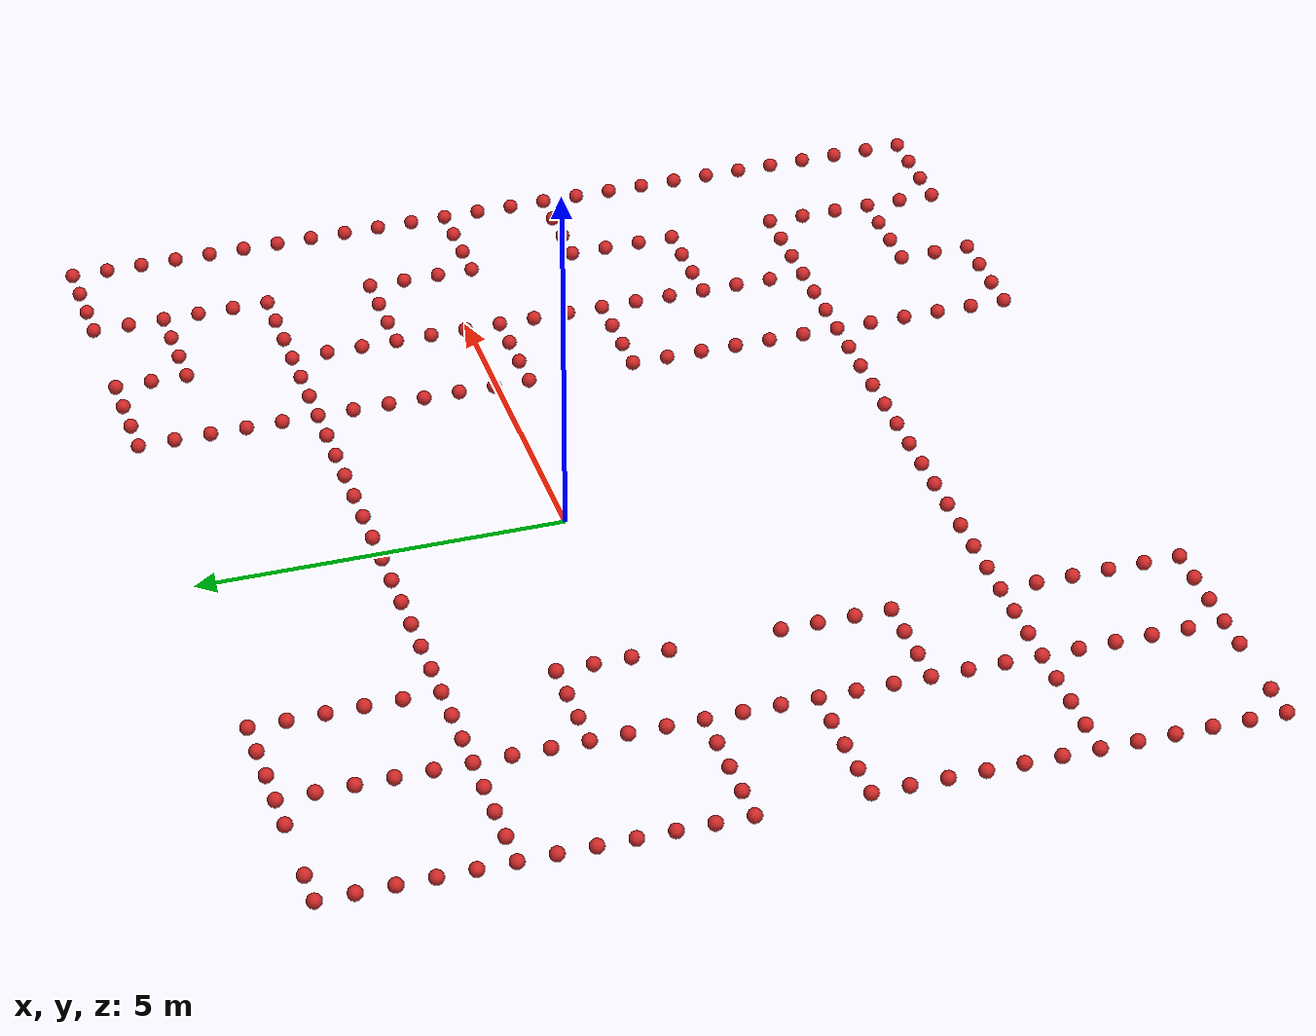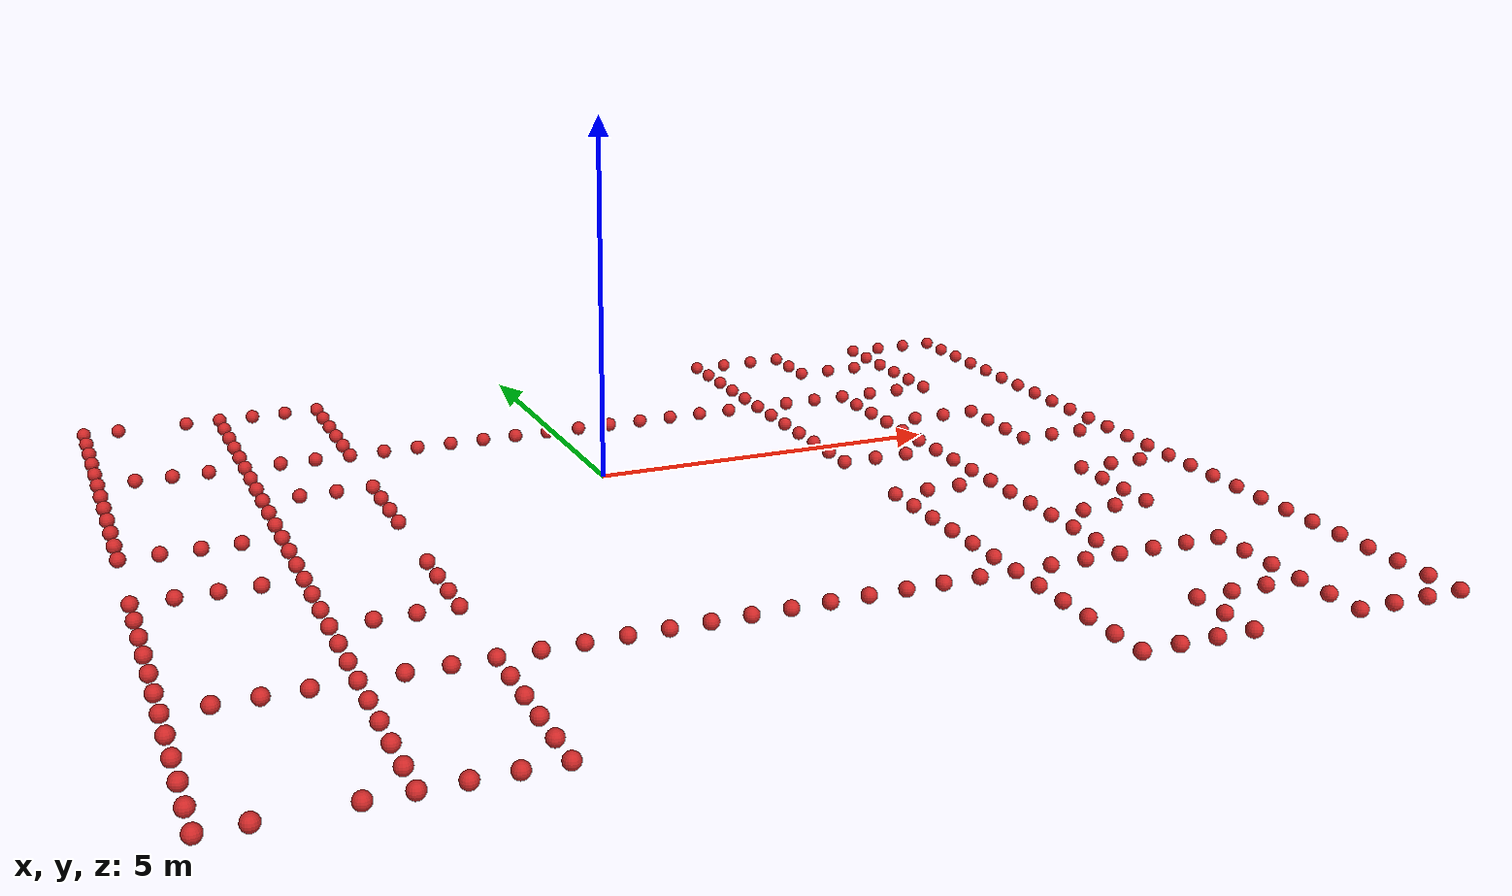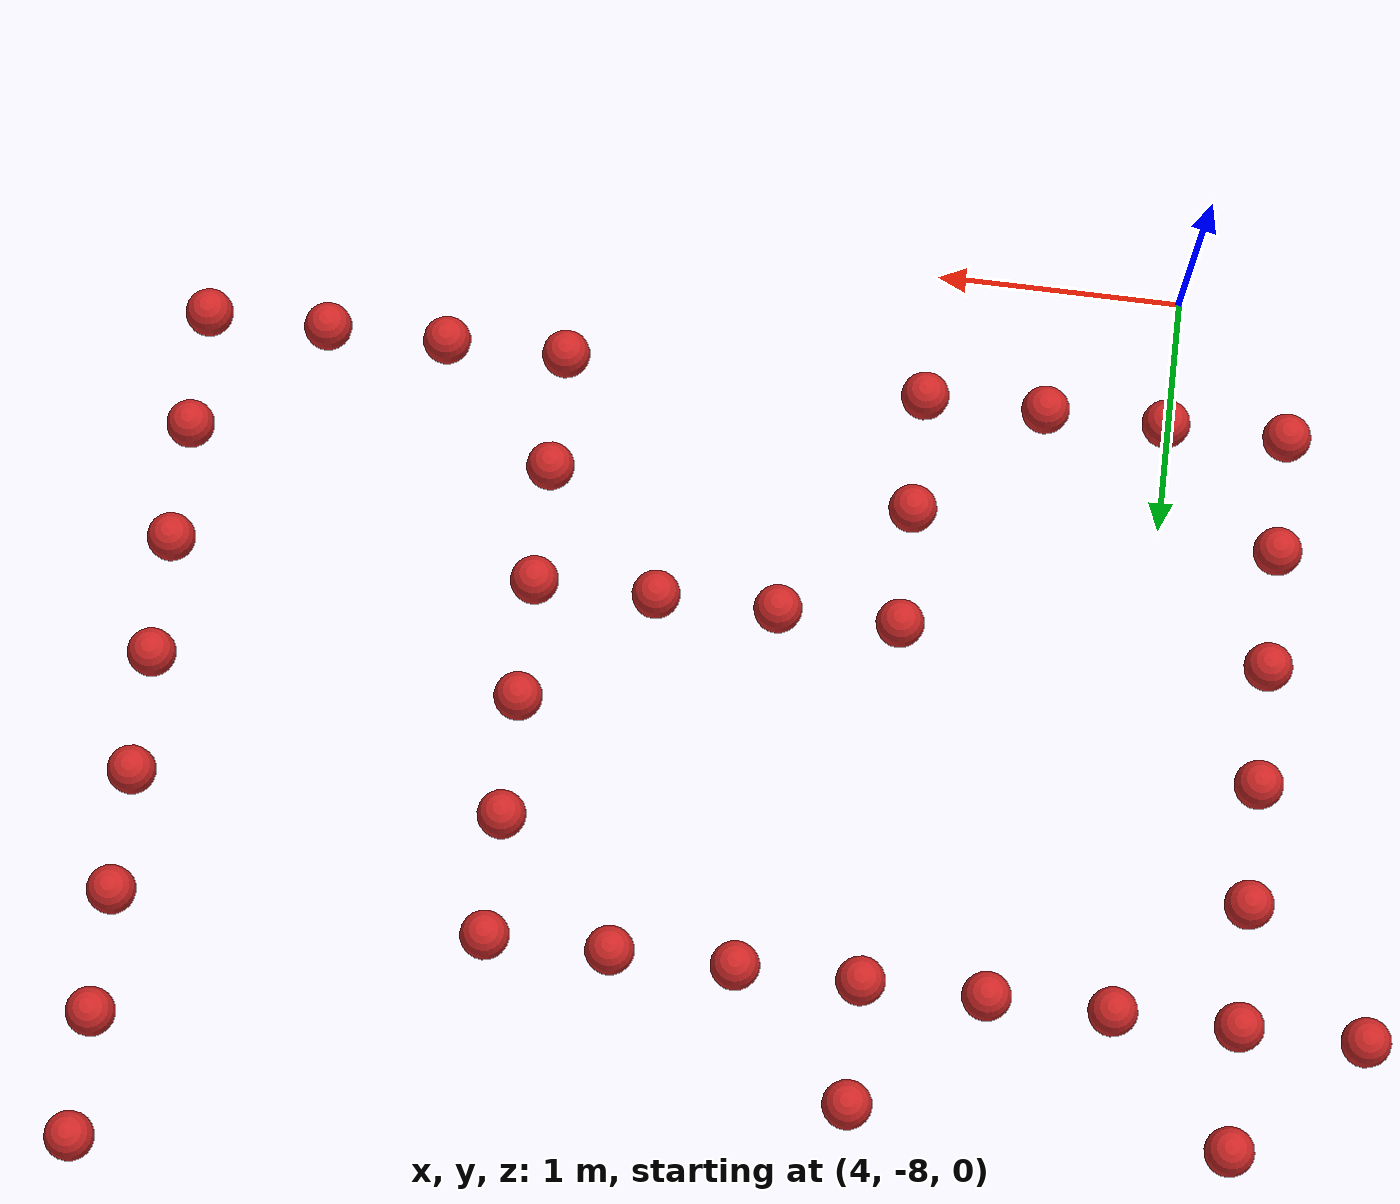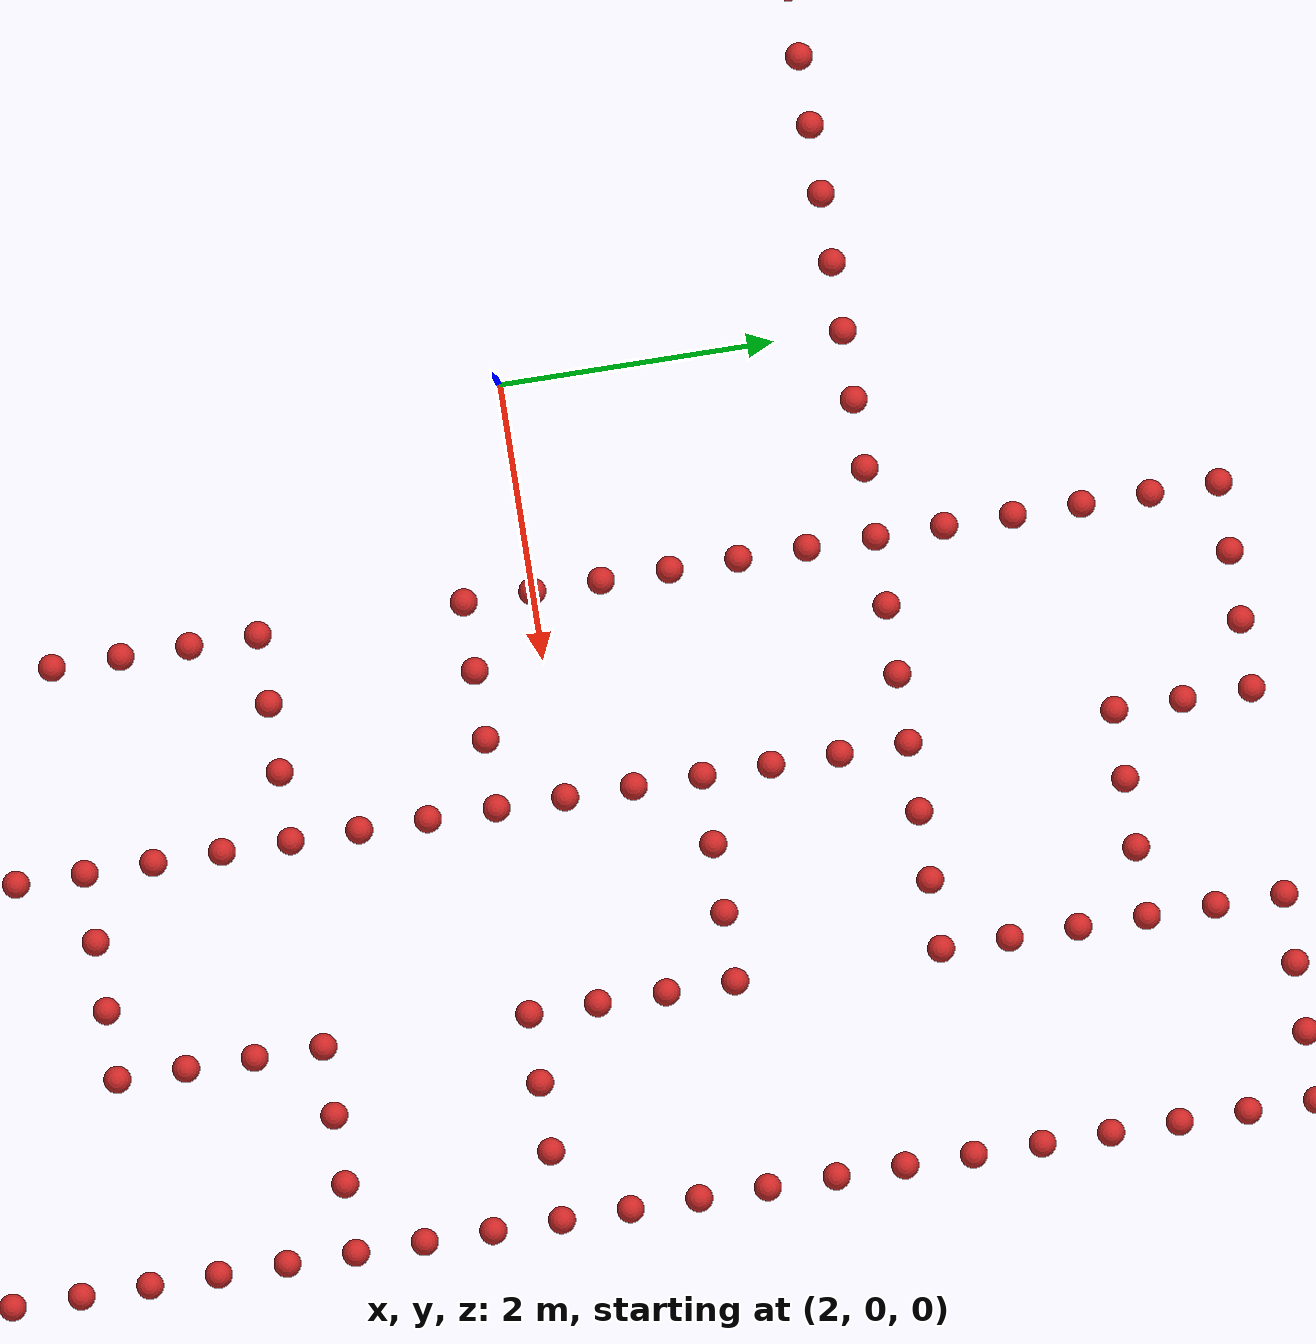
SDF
<?xml version='1.0'?>
<sdf version='1.6'>
  <model name='level1'>
  <link name='Score_Point1'>
    <collision name='Score_Point_Collision1'>
      <geometry>
        <sphere>
          <radius>0.1</radius>
        </sphere>
      </geometry>
    </collision>
    <visual name='Score_Point_Visual1'>
      <geometry>
        <sphere>
          <radius>0.1</radius>
        </sphere>
      </geometry>
      <material>
        <script>
          <uri>file://media/materials/scripts/gazebo.material</uri>
          <name>Gazebo/Red</name>
        </script>
        <ambient>1 1 1 1</ambient>
      </material>
      <meta>
        <layer>0</layer>
      </meta>
    </visual>
    <pose frame=''>-6.5 -7.5 -0.08 0 0 0</pose>
    <script>
      <uri>file://scripts/score_point_script.py</uri>
    </script>
  </link>
  <link name='Score_Point2'>
    <collision name='Score_Point_Collision2'>
      <geometry>
        <sphere>
          <radius>0.1</radius>
        </sphere>
      </geometry>
    </collision>
    <visual name='Score_Point_Visual2'>
      <geometry>
        <sphere>
          <radius>0.1</radius>
        </sphere>
      </geometry>
      <material>
        <script>
          <uri>file://media/materials/scripts/gazebo.material</uri>
          <name>Gazebo/Red</name>
        </script>
        <ambient>1 1 1 1</ambient>
      </material>
      <meta>
        <layer>0</layer>
      </meta>
    </visual>
    <pose frame=''>-6.5 -7.0 -0.08 0 0 0</pose>
    <script>
      <uri>file://scripts/score_point_script.py</uri>
    </script>
  </link>

  <link name='Score_Point3'>
    <collision name='Score_Point_Collision3'>
      <geometry>
        <sphere>
          <radius>0.1</radius>
        </sphere>
      </geometry>
    </collision>
    <visual name='Score_Point_Visual3'>
      <geometry>
        <sphere>
          <radius>0.1</radius>
        </sphere>
      </geometry>
      <material>
        <script>
          <uri>file://media/materials/scripts/gazebo.material</uri>
          <name>Gazebo/Red</name>
        </script>
        <ambient>1 1 1 1</ambient>
      </material>
      <meta>
        <layer>0</layer>
      </meta>
    </visual>
    <pose frame=''>-6.5 -6.5 -0.08 0 0 0</pose>
    <script>
      <uri>file://scripts/score_point_script.py</uri>
    </script>
  </link>

  <link name='Score_Point4'>
    <collision name='Score_Point_Collision4'>
      <geometry>
        <sphere>
          <radius>0.1</radius>
        </sphere>
      </geometry>
    </collision>
    <visual name='Score_Point_Visual4'>
      <geometry>
        <sphere>
          <radius>0.1</radius>
        </sphere>
      </geometry>
      <material>
        <script>
          <uri>file://media/materials/scripts/gazebo.material</uri>
          <name>Gazebo/Red</name>
        </script>
        <ambient>1 1 1 1</ambient>
      </material>
      <meta>
        <layer>0</layer>
      </meta>
    </visual>
    <pose frame=''>-6.5 -6.0 -0.08 0 0 0</pose>
    <script>
      <uri>file://scripts/score_point_script.py</uri>
    </script>
  </link>

  <link name='Score_Point5'>
    <collision name='Score_Point_Collision5'>
      <geometry>
        <sphere>
          <radius>0.1</radius>
        </sphere>
      </geometry>
    </collision>
    <visual name='Score_Point_Visual5'>
      <geometry>
        <sphere>
          <radius>0.1</radius>
        </sphere>
      </geometry>
      <material>
        <script>
          <uri>file://media/materials/scripts/gazebo.material</uri>
          <name>Gazebo/Red</name>
        </script>
        <ambient>1 1 1 1</ambient>
      </material>
      <meta>
        <layer>0</layer>
      </meta>
    </visual>
    <pose frame=''>-6.5 -5.5 -0.08 0 0 0</pose>
    <script>
      <uri>file://scripts/score_point_script.py</uri>
    </script>
  </link>

  <link name='Score_Point6'>
    <collision name='Score_Point_Collision6'>
      <geometry>
        <sphere>
          <radius>0.1</radius>
        </sphere>
      </geometry>
    </collision>
    <visual name='Score_Point_Visual6'>
      <geometry>
        <sphere>
          <radius>0.1</radius>
        </sphere>
      </geometry>
      <material>
        <script>
          <uri>file://media/materials/scripts/gazebo.material</uri>
          <name>Gazebo/Red</name>
        </script>
        <ambient>1 1 1 1</ambient>
      </material>
      <meta>
        <layer>0</layer>
      </meta>
    </visual>
    <pose frame=''>-6.5 -5.0 -0.08 0 0 0</pose>
    <script>
      <uri>file://scripts/score_point_script.py</uri>
    </script>
  </link>

  <link name='Score_Point7'>
    <collision name='Score_Point_Collision7'>
      <geometry>
        <sphere>
          <radius>0.1</radius>
        </sphere>
      </geometry>
    </collision>
    <visual name='Score_Point_Visual7'>
      <geometry>
        <sphere>
          <radius>0.1</radius>
        </sphere>
      </geometry>
      <material>
        <script>
          <uri>file://media/materials/scripts/gazebo.material</uri>
          <name>Gazebo/Red</name>
        </script>
        <ambient>1 1 1 1</ambient>
      </material>
      <meta>
        <layer>0</layer>
      </meta>
    </visual>
    <pose frame=''>-6.5 -4.5 -0.08 0 0 0</pose>
    <script>
      <uri>file://scripts/score_point_script.py</uri>
    </script>
  </link>

  <link name='Score_Point8'>
    <collision name='Score_Point_Collision8'>
      <geometry>
        <sphere>
          <radius>0.1</radius>
        </sphere>
      </geometry>
    </collision>
    <visual name='Score_Point_Visual8'>
      <geometry>
        <sphere>
          <radius>0.1</radius>
        </sphere>
      </geometry>
      <material>
        <script>
          <uri>file://media/materials/scripts/gazebo.material</uri>
          <name>Gazebo/Red</name>
        </script>
        <ambient>1 1 1 1</ambient>
      </material>
      <meta>
        <layer>0</layer>
      </meta>
    </visual>
    <pose frame=''>-6.5 -4.0 -0.08 0 0 0</pose>
    <script>
      <uri>file://scripts/score_point_script.py</uri>
    </script>
  </link>

  <link name='Score_Point9'>
    <collision name='Score_Point_Collision9'>
      <geometry>
        <sphere>
          <radius>0.1</radius>
        </sphere>
      </geometry>
    </collision>
    <visual name='Score_Point_Visual9'>
      <geometry>
        <sphere>
          <radius>0.1</radius>
        </sphere>
      </geometry>
      <material>
        <script>
          <uri>file://media/materials/scripts/gazebo.material</uri>
          <name>Gazebo/Red</name>
        </script>
        <ambient>1 1 1 1</ambient>
      </material>
      <meta>
        <layer>0</layer>
      </meta>
    </visual>
    <pose frame=''>-6.5 -3.5 -0.08 0 0 0</pose>
    <script>
      <uri>file://scripts/score_point_script.py</uri>
    </script>
  </link>

  <link name='Score_Point10'>
    <collision name='Score_Point_Collision10'>
      <geometry>
        <sphere>
          <radius>0.1</radius>
        </sphere>
      </geometry>
    </collision>
    <visual name='Score_Point_Visual10'>
      <geometry>
        <sphere>
          <radius>0.1</radius>
        </sphere>
      </geometry>
      <material>
        <script>
          <uri>file://media/materials/scripts/gazebo.material</uri>
          <name>Gazebo/Red</name>
        </script>
        <ambient>1 1 1 1</ambient>
      </material>
      <meta>
        <layer>0</layer>
      </meta>
    </visual>
    <pose frame=''>-6.5 -3.0 -0.08 0 0 0</pose>
    <script>
      <uri>file://scripts/score_point_script.py</uri>
    </script>
  </link>

  <link name='Score_Point11'>
    <collision name='Score_Point_Collision11'>
      <geometry>
        <sphere>
          <radius>0.1</radius>
        </sphere>
      </geometry>
    </collision>
    <visual name='Score_Point_Visual11'>
      <geometry>
        <sphere>
          <radius>0.1</radius>
        </sphere>
      </geometry>
      <material>
        <script>
          <uri>file://media/materials/scripts/gazebo.material</uri>
          <name>Gazebo/Red</name>
        </script>
        <ambient>1 1 1 1</ambient>
      </material>
      <meta>
        <layer>0</layer>
      </meta>
    </visual>
    <pose frame=''>-6.5 -2.5 -0.08 0 0 0</pose>
    <script>
      <uri>file://scripts/score_point_script.py</uri>
    </script>
  </link>

  <link name='Score_Point12'>
    <collision name='Score_Point_Collision12'>
      <geometry>
        <sphere>
          <radius>0.1</radius>
        </sphere>
      </geometry>
    </collision>
    <visual name='Score_Point_Visual12'>
      <geometry>
        <sphere>
          <radius>0.1</radius>
        </sphere>
      </geometry>
      <material>
        <script>
          <uri>file://media/materials/scripts/gazebo.material</uri>
          <name>Gazebo/Red</name>
        </script>
        <ambient>1 1 1 1</ambient>
      </material>
      <meta>
        <layer>0</layer>
      </meta>
    </visual>
    <pose frame=''>-6.5 -2.0 -0.08 0 0 0</pose>
    <script>
      <uri>file://scripts/score_point_script.py</uri>
    </script>
  </link>

  <link name='Score_Point13'>
    <collision name='Score_Point_Collision13'>
      <geometry>
        <sphere>
          <radius>0.1</radius>
        </sphere>
      </geometry>
    </collision>
    <visual name='Score_Point_Visual13'>
      <geometry>
        <sphere>
          <radius>0.1</radius>
        </sphere>
      </geometry>
      <material>
        <script>
          <uri>file://media/materials/scripts/gazebo.material</uri>
          <name>Gazebo/Red</name>
        </script>
        <ambient>1 1 1 1</ambient>
      </material>
      <meta>
        <layer>0</layer>
      </meta>
    </visual>
    <pose frame=''>-6.5 -0.5 -0.08 0 0 0</pose>
    <script>
      <uri>file://scripts/score_point_script.py</uri>
    </script>
  </link>

  <link name='Score_Point14'>
    <collision name='Score_Point_Collision14'>
      <geometry>
        <sphere>
          <radius>0.1</radius>
        </sphere>
      </geometry>
    </collision>
    <visual name='Score_Point_Visual14'>
      <geometry>
        <sphere>
          <radius>0.1</radius>
        </sphere>
      </geometry>
      <material>
        <script>
          <uri>file://media/materials/scripts/gazebo.material</uri>
          <name>Gazebo/Red</name>
        </script>
        <ambient>1 1 1 1</ambient>
      </material>
      <meta>
        <layer>0</layer>
      </meta>
    </visual>
    <pose frame=''>-6.5 0.0 -0.08 0 0 0</pose>
    <script>
      <uri>file://scripts/score_point_script.py</uri>
    </script>
  </link>

  <link name='Score_Point15'>
    <collision name='Score_Point_Collision15'>
      <geometry>
        <sphere>
          <radius>0.1</radius>
        </sphere>
      </geometry>
    </collision>
    <visual name='Score_Point_Visual15'>
      <geometry>
        <sphere>
          <radius>0.1</radius>
        </sphere>
      </geometry>
      <material>
        <script>
          <uri>file://media/materials/scripts/gazebo.material</uri>
          <name>Gazebo/Red</name>
        </script>
        <ambient>1 1 1 1</ambient>
      </material>
      <meta>
        <layer>0</layer>
      </meta>
    </visual>
    <pose frame=''>-6.5 0.5 -0.08 0 0 0</pose>
    <script>
      <uri>file://scripts/score_point_script.py</uri>
    </script>
  </link>

  <link name='Score_Point16'>
    <collision name='Score_Point_Collision16'>
      <geometry>
        <sphere>
          <radius>0.1</radius>
        </sphere>
      </geometry>
    </collision>
    <visual name='Score_Point_Visual16'>
      <geometry>
        <sphere>
          <radius>0.1</radius>
        </sphere>
      </geometry>
      <material>
        <script>
          <uri>file://media/materials/scripts/gazebo.material</uri>
          <name>Gazebo/Red</name>
        </script>
        <ambient>1 1 1 1</ambient>
      </material>
      <meta>
        <layer>0</layer>
      </meta>
    </visual>
    <pose frame=''>-6.5 1.0 -0.08 0 0 0</pose>
    <script>
      <uri>file://scripts/score_point_script.py</uri>
    </script>
  </link>

  <link name='Score_Point17'>
    <collision name='Score_Point_Collision17'>
      <geometry>
        <sphere>
          <radius>0.1</radius>
        </sphere>
      </geometry>
    </collision>
    <visual name='Score_Point_Visual17'>
      <geometry>
        <sphere>
          <radius>0.1</radius>
        </sphere>
      </geometry>
      <material>
        <script>
          <uri>file://media/materials/scripts/gazebo.material</uri>
          <name>Gazebo/Red</name>
        </script>
        <ambient>1 1 1 1</ambient>
      </material>
      <meta>
        <layer>0</layer>
      </meta>
    </visual>
    <pose frame=''>-6.5 1.5 -0.08 0 0 0</pose>
    <script>
      <uri>file://scripts/score_point_script.py</uri>
    </script>
  </link>

  <link name='Score_Point18'>
    <collision name='Score_Point_Collision18'>
      <geometry>
        <sphere>
          <radius>0.1</radius>
        </sphere>
      </geometry>
    </collision>
    <visual name='Score_Point_Visual18'>
      <geometry>
        <sphere>
          <radius>0.1</radius>
        </sphere>
      </geometry>
      <material>
        <script>
          <uri>file://media/materials/scripts/gazebo.material</uri>
          <name>Gazebo/Red</name>
        </script>
        <ambient>1 1 1 1</ambient>
      </material>
      <meta>
        <layer>0</layer>
      </meta>
    </visual>
    <pose frame=''>-6.5 2.0 -0.08 0 0 0</pose>
    <script>
      <uri>file://scripts/score_point_script.py</uri>
    </script>
  </link>

  <link name='Score_Point19'>
    <collision name='Score_Point_Collision19'>
      <geometry>
        <sphere>
          <radius>0.1</radius>
        </sphere>
      </geometry>
    </collision>
    <visual name='Score_Point_Visual19'>
      <geometry>
        <sphere>
          <radius>0.1</radius>
        </sphere>
      </geometry>
      <material>
        <script>
          <uri>file://media/materials/scripts/gazebo.material</uri>
          <name>Gazebo/Red</name>
        </script>
        <ambient>1 1 1 1</ambient>
      </material>
      <meta>
        <layer>0</layer>
      </meta>
    </visual>
    <pose frame=''>-6.5 2.5 -0.08 0 0 0</pose>
    <script>
      <uri>file://scripts/score_point_script.py</uri>
    </script>
  </link>

  <link name='Score_Point20'>
    <collision name='Score_Point_Collision20'>
      <geometry>
        <sphere>
          <radius>0.1</radius>
        </sphere>
      </geometry>
    </collision>
    <visual name='Score_Point_Visual20'>
      <geometry>
        <sphere>
          <radius>0.1</radius>
        </sphere>
      </geometry>
      <material>
        <script>
          <uri>file://media/materials/scripts/gazebo.material</uri>
          <name>Gazebo/Red</name>
        </script>
        <ambient>1 1 1 1</ambient>
      </material>
      <meta>
        <layer>0</layer>
      </meta>
    </visual>
    <pose frame=''>-6.5 3.0 -0.08 0 0 0</pose>
    <script>
      <uri>file://scripts/score_point_script.py</uri>
    </script>
  </link>

  <link name='Score_Point21'>
    <collision name='Score_Point_Collision21'>
      <geometry>
        <sphere>
          <radius>0.1</radius>
        </sphere>
      </geometry>
    </collision>
    <visual name='Score_Point_Visual21'>
      <geometry>
        <sphere>
          <radius>0.1</radius>
        </sphere>
      </geometry>
      <material>
        <script>
          <uri>file://media/materials/scripts/gazebo.material</uri>
          <name>Gazebo/Red</name>
        </script>
        <ambient>1 1 1 1</ambient>
      </material>
      <meta>
        <layer>0</layer>
      </meta>
    </visual>
    <pose frame=''>-6.5 3.5 -0.08 0 0 0</pose>
    <script>
      <uri>file://scripts/score_point_script.py</uri>
    </script>
  </link>

  <link name='Score_Point22'>
    <collision name='Score_Point_Collision22'>
      <geometry>
        <sphere>
          <radius>0.1</radius>
        </sphere>
      </geometry>
    </collision>
    <visual name='Score_Point_Visual22'>
      <geometry>
        <sphere>
          <radius>0.1</radius>
        </sphere>
      </geometry>
      <material>
        <script>
          <uri>file://media/materials/scripts/gazebo.material</uri>
          <name>Gazebo/Red</name>
        </script>
        <ambient>1 1 1 1</ambient>
      </material>
      <meta>
        <layer>0</layer>
      </meta>
    </visual>
    <pose frame=''>-6.5 4.0 -0.08 0 0 0</pose>
    <script>
      <uri>file://scripts/score_point_script.py</uri>
    </script>
  </link>

  <link name='Score_Point23'>
    <collision name='Score_Point_Collision23'>
      <geometry>
        <sphere>
          <radius>0.1</radius>
        </sphere>
      </geometry>
    </collision>
    <visual name='Score_Point_Visual23'>
      <geometry>
        <sphere>
          <radius>0.1</radius>
        </sphere>
      </geometry>
      <material>
        <script>
          <uri>file://media/materials/scripts/gazebo.material</uri>
          <name>Gazebo/Red</name>
        </script>
        <ambient>1 1 1 1</ambient>
      </material>
      <meta>
        <layer>0</layer>
      </meta>
    </visual>
    <pose frame=''>-6.5 4.5 -0.08 0 0 0</pose>
    <script>
      <uri>file://scripts/score_point_script.py</uri>
    </script>
  </link>

  <link name='Score_Point24'>
    <collision name='Score_Point_Collision24'>
      <geometry>
        <sphere>
          <radius>0.1</radius>
        </sphere>
      </geometry>
    </collision>
    <visual name='Score_Point_Visual24'>
      <geometry>
        <sphere>
          <radius>0.1</radius>
        </sphere>
      </geometry>
      <material>
        <script>
          <uri>file://media/materials/scripts/gazebo.material</uri>
          <name>Gazebo/Red</name>
        </script>
        <ambient>1 1 1 1</ambient>
      </material>
      <meta>
        <layer>0</layer>
      </meta>
    </visual>
    <pose frame=''>-6.5 5.0 -0.08 0 0 0</pose>
    <script>
      <uri>file://scripts/score_point_script.py</uri>
    </script>
  </link>

  <link name='Score_Point25'>
    <collision name='Score_Point_Collision25'>
      <geometry>
        <sphere>
          <radius>0.1</radius>
        </sphere>
      </geometry>
    </collision>
    <visual name='Score_Point_Visual25'>
      <geometry>
        <sphere>
          <radius>0.1</radius>
        </sphere>
      </geometry>
      <material>
        <script>
          <uri>file://media/materials/scripts/gazebo.material</uri>
          <name>Gazebo/Red</name>
        </script>
        <ambient>1 1 1 1</ambient>
      </material>
      <meta>
        <layer>0</layer>
      </meta>
    </visual>
    <pose frame=''>-6.0 -7.5 -0.08 0 0 0</pose>
    <script>
      <uri>file://scripts/score_point_script.py</uri>
    </script>
  </link>

  <link name='Score_Point26'>
    <collision name='Score_Point_Collision26'>
      <geometry>
        <sphere>
          <radius>0.1</radius>
        </sphere>
      </geometry>
    </collision>
    <visual name='Score_Point_Visual26'>
      <geometry>
        <sphere>
          <radius>0.1</radius>
        </sphere>
      </geometry>
      <material>
        <script>
          <uri>file://media/materials/scripts/gazebo.material</uri>
          <name>Gazebo/Red</name>
        </script>
        <ambient>1 1 1 1</ambient>
      </material>
      <meta>
        <layer>0</layer>
      </meta>
    </visual>
    <pose frame=''>-6.0 -5.0 -0.08 0 0 0</pose>
    <script>
      <uri>file://scripts/score_point_script.py</uri>
    </script>
  </link>

  <link name='Score_Point27'>
    <collision name='Score_Point_Collision27'>
      <geometry>
        <sphere>
          <radius>0.1</radius>
        </sphere>
      </geometry>
    </collision>
    <visual name='Score_Point_Visual27'>
      <geometry>
        <sphere>
          <radius>0.1</radius>
        </sphere>
      </geometry>
      <material>
        <script>
          <uri>file://media/materials/scripts/gazebo.material</uri>
          <name>Gazebo/Red</name>
        </script>
        <ambient>1 1 1 1</ambient>
      </material>
      <meta>
        <layer>0</layer>
      </meta>
    </visual>
    <pose frame=''>-6.0 -2.0 -0.08 0 0 0</pose>
    <script>
      <uri>file://scripts/score_point_script.py</uri>
    </script>
  </link>

  <link name='Score_Point28'>
    <collision name='Score_Point_Collision28'>
      <geometry>
        <sphere>
          <radius>0.1</radius>
        </sphere>
      </geometry>
    </collision>
    <visual name='Score_Point_Visual28'>
      <geometry>
        <sphere>
          <radius>0.1</radius>
        </sphere>
      </geometry>
      <material>
        <script>
          <uri>file://media/materials/scripts/gazebo.material</uri>
          <name>Gazebo/Red</name>
        </script>
        <ambient>1 1 1 1</ambient>
      </material>
      <meta>
        <layer>0</layer>
      </meta>
    </visual>
    <pose frame=''>-6.0 -0.5 -0.08 0 0 0</pose>
    <script>
      <uri>file://scripts/score_point_script.py</uri>
    </script>
  </link>

  <link name='Score_Point29'>
    <collision name='Score_Point_Collision29'>
      <geometry>
        <sphere>
          <radius>0.1</radius>
        </sphere>
      </geometry>
    </collision>
    <visual name='Score_Point_Visual29'>
      <geometry>
        <sphere>
          <radius>0.1</radius>
        </sphere>
      </geometry>
      <material>
        <script>
          <uri>file://media/materials/scripts/gazebo.material</uri>
          <name>Gazebo/Red</name>
        </script>
        <ambient>1 1 1 1</ambient>
      </material>
      <meta>
        <layer>0</layer>
      </meta>
    </visual>
    <pose frame=''>-6.0 2.5 -0.08 0 0 0</pose>
    <script>
      <uri>file://scripts/score_point_script.py</uri>
    </script>
  </link>

  <link name='Score_Point30'>
    <collision name='Score_Point_Collision30'>
      <geometry>
        <sphere>
          <radius>0.1</radius>
        </sphere>
      </geometry>
    </collision>
    <visual name='Score_Point_Visual30'>
      <geometry>
        <sphere>
          <radius>0.1</radius>
        </sphere>
      </geometry>
      <material>
        <script>
          <uri>file://media/materials/scripts/gazebo.material</uri>
          <name>Gazebo/Red</name>
        </script>
        <ambient>1 1 1 1</ambient>
      </material>
      <meta>
        <layer>0</layer>
      </meta>
    </visual>
    <pose frame=''>-6.0 5.0 -0.08 0 0 0</pose>
    <script>
      <uri>file://scripts/score_point_script.py</uri>
    </script>
  </link>

  <link name='Score_Point31'>
    <collision name='Score_Point_Collision31'>
      <geometry>
        <sphere>
          <radius>0.1</radius>
        </sphere>
      </geometry>
    </collision>
    <visual name='Score_Point_Visual31'>
      <geometry>
        <sphere>
          <radius>0.1</radius>
        </sphere>
      </geometry>
      <material>
        <script>
          <uri>file://media/materials/scripts/gazebo.material</uri>
          <name>Gazebo/Red</name>
        </script>
        <ambient>1 1 1 1</ambient>
      </material>
      <meta>
        <layer>0</layer>
      </meta>
    </visual>
    <pose frame=''>-5.5 -5.0 -0.08 0 0 0</pose>
    <script>
      <uri>file://scripts/score_point_script.py</uri>
    </script>
  </link>

  <link name='Score_Point32'>
    <collision name='Score_Point_Collision32'>
      <geometry>
        <sphere>
          <radius>0.1</radius>
        </sphere>
      </geometry>
    </collision>
    <visual name='Score_Point_Visual32'>
      <geometry>
        <sphere>
          <radius>0.1</radius>
        </sphere>
      </geometry>
      <material>
        <script>
          <uri>file://media/materials/scripts/gazebo.material</uri>
          <name>Gazebo/Red</name>
        </script>
        <ambient>1 1 1 1</ambient>
      </material>
      <meta>
        <layer>0</layer>
      </meta>
    </visual>
    <pose frame=''>-5.5 -2.0 -0.08 0 0 0</pose>
    <script>
      <uri>file://scripts/score_point_script.py</uri>
    </script>
  </link>

  <link name='Score_Point33'>
    <collision name='Score_Point_Collision33'>
      <geometry>
        <sphere>
          <radius>0.1</radius>
        </sphere>
      </geometry>
    </collision>
    <visual name='Score_Point_Visual33'>
      <geometry>
        <sphere>
          <radius>0.1</radius>
        </sphere>
      </geometry>
      <material>
        <script>
          <uri>file://media/materials/scripts/gazebo.material</uri>
          <name>Gazebo/Red</name>
        </script>
        <ambient>1 1 1 1</ambient>
      </material>
      <meta>
        <layer>0</layer>
      </meta>
    </visual>
    <pose frame=''>-5.5 -0.5 -0.08 0 0 0</pose>
    <script>
      <uri>file://scripts/score_point_script.py</uri>
    </script>
  </link>

  <link name='Score_Point34'>
    <collision name='Score_Point_Collision34'>
      <geometry>
        <sphere>
          <radius>0.1</radius>
        </sphere>
      </geometry>
    </collision>
    <visual name='Score_Point_Visual34'>
      <geometry>
        <sphere>
          <radius>0.1</radius>
        </sphere>
      </geometry>
      <material>
        <script>
          <uri>file://media/materials/scripts/gazebo.material</uri>
          <name>Gazebo/Red</name>
        </script>
        <ambient>1 1 1 1</ambient>
      </material>
      <meta>
        <layer>0</layer>
      </meta>
    </visual>
    <pose frame=''>-5.5 2.5 -0.08 0 0 0</pose>
    <script>
      <uri>file://scripts/score_point_script.py</uri>
    </script>
  </link>

  <link name='Score_Point35'>
    <collision name='Score_Point_Collision35'>
      <geometry>
        <sphere>
          <radius>0.1</radius>
        </sphere>
      </geometry>
    </collision>
    <visual name='Score_Point_Visual35'>
      <geometry>
        <sphere>
          <radius>0.1</radius>
        </sphere>
      </geometry>
      <material>
        <script>
          <uri>file://media/materials/scripts/gazebo.material</uri>
          <name>Gazebo/Red</name>
        </script>
        <ambient>1 1 1 1</ambient>
      </material>
      <meta>
        <layer>0</layer>
      </meta>
    </visual>
    <pose frame=''>-5.0 -7.5 -0.08 0 0 0</pose>
    <script>
      <uri>file://scripts/score_point_script.py</uri>
    </script>
  </link>

  <link name='Score_Point36'>
    <collision name='Score_Point_Collision36'>
      <geometry>
        <sphere>
          <radius>0.1</radius>
        </sphere>
      </geometry>
    </collision>
    <visual name='Score_Point_Visual36'>
      <geometry>
        <sphere>
          <radius>0.1</radius>
        </sphere>
      </geometry>
      <material>
        <script>
          <uri>file://media/materials/scripts/gazebo.material</uri>
          <name>Gazebo/Red</name>
        </script>
        <ambient>1 1 1 1</ambient>
      </material>
      <meta>
        <layer>0</layer>
      </meta>
    </visual>
    <pose frame=''>-5.0 -5.0 -0.08 0 0 0</pose>
    <script>
      <uri>file://scripts/score_point_script.py</uri>
    </script>
  </link>

  <link name='Score_Point37'>
    <collision name='Score_Point_Collision37'>
      <geometry>
        <sphere>
          <radius>0.1</radius>
        </sphere>
      </geometry>
    </collision>
    <visual name='Score_Point_Visual37'>
      <geometry>
        <sphere>
          <radius>0.1</radius>
        </sphere>
      </geometry>
      <material>
        <script>
          <uri>file://media/materials/scripts/gazebo.material</uri>
          <name>Gazebo/Red</name>
        </script>
        <ambient>1 1 1 1</ambient>
      </material>
      <meta>
        <layer>0</layer>
      </meta>
    </visual>
    <pose frame=''>-5.0 -2.0 -0.08 0 0 0</pose>
    <script>
      <uri>file://scripts/score_point_script.py</uri>
    </script>
  </link>

  <link name='Score_Point38'>
    <collision name='Score_Point_Collision38'>
      <geometry>
        <sphere>
          <radius>0.1</radius>
        </sphere>
      </geometry>
    </collision>
    <visual name='Score_Point_Visual38'>
      <geometry>
        <sphere>
          <radius>0.1</radius>
        </sphere>
      </geometry>
      <material>
        <script>
          <uri>file://media/materials/scripts/gazebo.material</uri>
          <name>Gazebo/Red</name>
        </script>
        <ambient>1 1 1 1</ambient>
      </material>
      <meta>
        <layer>0</layer>
      </meta>
    </visual>
    <pose frame=''>-5.0 -0.5 -0.08 0 0 0</pose>
    <script>
      <uri>file://scripts/score_point_script.py</uri>
    </script>
  </link>

  <link name='Score_Point39'>
    <collision name='Score_Point_Collision39'>
      <geometry>
        <sphere>
          <radius>0.1</radius>
        </sphere>
      </geometry>
    </collision>
    <visual name='Score_Point_Visual39'>
      <geometry>
        <sphere>
          <radius>0.1</radius>
        </sphere>
      </geometry>
      <material>
        <script>
          <uri>file://media/materials/scripts/gazebo.material</uri>
          <name>Gazebo/Red</name>
        </script>
        <ambient>1 1 1 1</ambient>
      </material>
      <meta>
        <layer>0</layer>
      </meta>
    </visual>
    <pose frame=''>-5.0 2.5 -0.08 0 0 0</pose>
    <script>
      <uri>file://scripts/score_point_script.py</uri>
    </script>
  </link>

  <link name='Score_Point40'>
    <collision name='Score_Point_Collision40'>
      <geometry>
        <sphere>
          <radius>0.1</radius>
        </sphere>
      </geometry>
    </collision>
    <visual name='Score_Point_Visual40'>
      <geometry>
        <sphere>
          <radius>0.1</radius>
        </sphere>
      </geometry>
      <material>
        <script>
          <uri>file://media/materials/scripts/gazebo.material</uri>
          <name>Gazebo/Red</name>
        </script>
        <ambient>1 1 1 1</ambient>
      </material>
      <meta>
        <layer>0</layer>
      </meta>
    </visual>
    <pose frame=''>-5.0 5.0 -0.08 0 0 0</pose>
    <script>
      <uri>file://scripts/score_point_script.py</uri>
    </script>
  </link>

  <link name='Score_Point41'>
    <collision name='Score_Point_Collision41'>
      <geometry>
        <sphere>
          <radius>0.1</radius>
        </sphere>
      </geometry>
    </collision>
    <visual name='Score_Point_Visual41'>
      <geometry>
        <sphere>
          <radius>0.1</radius>
        </sphere>
      </geometry>
      <material>
        <script>
          <uri>file://media/materials/scripts/gazebo.material</uri>
          <name>Gazebo/Red</name>
        </script>
        <ambient>1 1 1 1</ambient>
      </material>
      <meta>
        <layer>0</layer>
      </meta>
    </visual>
    <pose frame=''>-4.5 -7.5 -0.08 0 0 0</pose>
    <script>
      <uri>file://scripts/score_point_script.py</uri>
    </script>
  </link>

  <link name='Score_Point42'>
    <collision name='Score_Point_Collision42'>
      <geometry>
        <sphere>
          <radius>0.1</radius>
        </sphere>
      </geometry>
    </collision>
    <visual name='Score_Point_Visual42'>
      <geometry>
        <sphere>
          <radius>0.1</radius>
        </sphere>
      </geometry>
      <material>
        <script>
          <uri>file://media/materials/scripts/gazebo.material</uri>
          <name>Gazebo/Red</name>
        </script>
        <ambient>1 1 1 1</ambient>
      </material>
      <meta>
        <layer>0</layer>
      </meta>
    </visual>
    <pose frame=''>-4.5 -7.0 -0.08 0 0 0</pose>
    <script>
      <uri>file://scripts/score_point_script.py</uri>
    </script>
  </link>

  <link name='Score_Point43'>
    <collision name='Score_Point_Collision43'>
      <geometry>
        <sphere>
          <radius>0.1</radius>
        </sphere>
      </geometry>
    </collision>
    <visual name='Score_Point_Visual43'>
      <geometry>
        <sphere>
          <radius>0.1</radius>
        </sphere>
      </geometry>
      <material>
        <script>
          <uri>file://media/materials/scripts/gazebo.material</uri>
          <name>Gazebo/Red</name>
        </script>
        <ambient>1 1 1 1</ambient>
      </material>
      <meta>
        <layer>0</layer>
      </meta>
    </visual>
    <pose frame=''>-4.5 -6.5 -0.08 0 0 0</pose>
    <script>
      <uri>file://scripts/score_point_script.py</uri>
    </script>
  </link>

  <link name='Score_Point44'>
    <collision name='Score_Point_Collision44'>
      <geometry>
        <sphere>
          <radius>0.1</radius>
        </sphere>
      </geometry>
    </collision>
    <visual name='Score_Point_Visual44'>
      <geometry>
        <sphere>
          <radius>0.1</radius>
        </sphere>
      </geometry>
      <material>
        <script>
          <uri>file://media/materials/scripts/gazebo.material</uri>
          <name>Gazebo/Red</name>
        </script>
        <ambient>1 1 1 1</ambient>
      </material>
      <meta>
        <layer>0</layer>
      </meta>
    </visual>
    <pose frame=''>-4.5 -6.0 -0.08 0 0 0</pose>
    <script>
      <uri>file://scripts/score_point_script.py</uri>
    </script>
  </link>

  <link name='Score_Point45'>
    <collision name='Score_Point_Collision45'>
      <geometry>
        <sphere>
          <radius>0.1</radius>
        </sphere>
      </geometry>
    </collision>
    <visual name='Score_Point_Visual45'>
      <geometry>
        <sphere>
          <radius>0.1</radius>
        </sphere>
      </geometry>
      <material>
        <script>
          <uri>file://media/materials/scripts/gazebo.material</uri>
          <name>Gazebo/Red</name>
        </script>
        <ambient>1 1 1 1</ambient>
      </material>
      <meta>
        <layer>0</layer>
      </meta>
    </visual>
    <pose frame=''>-4.5 -5.5 -0.08 0 0 0</pose>
    <script>
      <uri>file://scripts/score_point_script.py</uri>
    </script>
  </link>

  <link name='Score_Point46'>
    <collision name='Score_Point_Collision46'>
      <geometry>
        <sphere>
          <radius>0.1</radius>
        </sphere>
      </geometry>
    </collision>
    <visual name='Score_Point_Visual46'>
      <geometry>
        <sphere>
          <radius>0.1</radius>
        </sphere>
      </geometry>
      <material>
        <script>
          <uri>file://media/materials/scripts/gazebo.material</uri>
          <name>Gazebo/Red</name>
        </script>
        <ambient>1 1 1 1</ambient>
      </material>
      <meta>
        <layer>0</layer>
      </meta>
    </visual>
    <pose frame=''>-4.5 -5.0 -0.08 0 0 0</pose>
    <script>
      <uri>file://scripts/score_point_script.py</uri>
    </script>
  </link>

  <link name='Score_Point47'>
    <collision name='Score_Point_Collision47'>
      <geometry>
        <sphere>
          <radius>0.1</radius>
        </sphere>
      </geometry>
    </collision>
    <visual name='Score_Point_Visual47'>
      <geometry>
        <sphere>
          <radius>0.1</radius>
        </sphere>
      </geometry>
      <material>
        <script>
          <uri>file://media/materials/scripts/gazebo.material</uri>
          <name>Gazebo/Red</name>
        </script>
        <ambient>1 1 1 1</ambient>
      </material>
      <meta>
        <layer>0</layer>
      </meta>
    </visual>
    <pose frame=''>-4.5 -4.5 -0.08 0 0 0</pose>
    <script>
      <uri>file://scripts/score_point_script.py</uri>
    </script>
  </link>

  <link name='Score_Point48'>
    <collision name='Score_Point_Collision48'>
      <geometry>
        <sphere>
          <radius>0.1</radius>
        </sphere>
      </geometry>
    </collision>
    <visual name='Score_Point_Visual48'>
      <geometry>
        <sphere>
          <radius>0.1</radius>
        </sphere>
      </geometry>
      <material>
        <script>
          <uri>file://media/materials/scripts/gazebo.material</uri>
          <name>Gazebo/Red</name>
        </script>
        <ambient>1 1 1 1</ambient>
      </material>
      <meta>
        <layer>0</layer>
      </meta>
    </visual>
    <pose frame=''>-4.5 -4.0 -0.08 0 0 0</pose>
    <script>
      <uri>file://scripts/score_point_script.py</uri>
    </script>
  </link>

  <link name='Score_Point49'>
    <collision name='Score_Point_Collision49'>
      <geometry>
        <sphere>
          <radius>0.1</radius>
        </sphere>
      </geometry>
    </collision>
    <visual name='Score_Point_Visual49'>
      <geometry>
        <sphere>
          <radius>0.1</radius>
        </sphere>
      </geometry>
      <material>
        <script>
          <uri>file://media/materials/scripts/gazebo.material</uri>
          <name>Gazebo/Red</name>
        </script>
        <ambient>1 1 1 1</ambient>
      </material>
      <meta>
        <layer>0</layer>
      </meta>
    </visual>
    <pose frame=''>-4.5 -3.5 -0.08 0 0 0</pose>
    <script>
      <uri>file://scripts/score_point_script.py</uri>
    </script>
  </link>

  <link name='Score_Point50'>
    <collision name='Score_Point_Collision50'>
      <geometry>
        <sphere>
          <radius>0.1</radius>
        </sphere>
      </geometry>
    </collision>
    <visual name='Score_Point_Visual50'>
      <geometry>
        <sphere>
          <radius>0.1</radius>
        </sphere>
      </geometry>
      <material>
        <script>
          <uri>file://media/materials/scripts/gazebo.material</uri>
          <name>Gazebo/Red</name>
        </script>
        <ambient>1 1 1 1</ambient>
      </material>
      <meta>
        <layer>0</layer>
      </meta>
    </visual>
    <pose frame=''>-4.5 -3.0 -0.08 0 0 0</pose>
    <script>
      <uri>file://scripts/score_point_script.py</uri>
    </script>
  </link>

  <link name='Score_Point51'>
    <collision name='Score_Point_Collision51'>
      <geometry>
        <sphere>
          <radius>0.1</radius>
        </sphere>
      </geometry>
    </collision>
    <visual name='Score_Point_Visual51'>
      <geometry>
        <sphere>
          <radius>0.1</radius>
        </sphere>
      </geometry>
      <material>
        <script>
          <uri>file://media/materials/scripts/gazebo.material</uri>
          <name>Gazebo/Red</name>
        </script>
        <ambient>1 1 1 1</ambient>
      </material>
      <meta>
        <layer>0</layer>
      </meta>
    </visual>
    <pose frame=''>-4.5 -2.5 -0.08 0 0 0</pose>
    <script>
      <uri>file://scripts/score_point_script.py</uri>
    </script>
  </link>

  <link name='Score_Point52'>
    <collision name='Score_Point_Collision52'>
      <geometry>
        <sphere>
          <radius>0.1</radius>
        </sphere>
      </geometry>
    </collision>
    <visual name='Score_Point_Visual52'>
      <geometry>
        <sphere>
          <radius>0.1</radius>
        </sphere>
      </geometry>
      <material>
        <script>
          <uri>file://media/materials/scripts/gazebo.material</uri>
          <name>Gazebo/Red</name>
        </script>
        <ambient>1 1 1 1</ambient>
      </material>
      <meta>
        <layer>0</layer>
      </meta>
    </visual>
    <pose frame=''>-4.5 -2.0 -0.08 0 0 0</pose>
    <script>
      <uri>file://scripts/score_point_script.py</uri>
    </script>
  </link>

  <link name='Score_Point53'>
    <collision name='Score_Point_Collision53'>
      <geometry>
        <sphere>
          <radius>0.1</radius>
        </sphere>
      </geometry>
    </collision>
    <visual name='Score_Point_Visual53'>
      <geometry>
        <sphere>
          <radius>0.1</radius>
        </sphere>
      </geometry>
      <material>
        <script>
          <uri>file://media/materials/scripts/gazebo.material</uri>
          <name>Gazebo/Red</name>
        </script>
        <ambient>1 1 1 1</ambient>
      </material>
      <meta>
        <layer>0</layer>
      </meta>
    </visual>
    <pose frame=''>-4.5 -1.5 -0.08 0 0 0</pose>
    <script>
      <uri>file://scripts/score_point_script.py</uri>
    </script>
  </link>

  <link name='Score_Point54'>
    <collision name='Score_Point_Collision54'>
      <geometry>
        <sphere>
          <radius>0.1</radius>
        </sphere>
      </geometry>
    </collision>
    <visual name='Score_Point_Visual54'>
      <geometry>
        <sphere>
          <radius>0.1</radius>
        </sphere>
      </geometry>
      <material>
        <script>
          <uri>file://media/materials/scripts/gazebo.material</uri>
          <name>Gazebo/Red</name>
        </script>
        <ambient>1 1 1 1</ambient>
      </material>
      <meta>
        <layer>0</layer>
      </meta>
    </visual>
    <pose frame=''>-4.5 -1.0 -0.08 0 0 0</pose>
    <script>
      <uri>file://scripts/score_point_script.py</uri>
    </script>
  </link>

  <link name='Score_Point55'>
    <collision name='Score_Point_Collision55'>
      <geometry>
        <sphere>
          <radius>0.1</radius>
        </sphere>
      </geometry>
    </collision>
    <visual name='Score_Point_Visual55'>
      <geometry>
        <sphere>
          <radius>0.1</radius>
        </sphere>
      </geometry>
      <material>
        <script>
          <uri>file://media/materials/scripts/gazebo.material</uri>
          <name>Gazebo/Red</name>
        </script>
        <ambient>1 1 1 1</ambient>
      </material>
      <meta>
        <layer>0</layer>
      </meta>
    </visual>
    <pose frame=''>-4.5 -0.5 -0.08 0 0 0</pose>
    <script>
      <uri>file://scripts/score_point_script.py</uri>
    </script>
  </link>

  <link name='Score_Point56'>
    <collision name='Score_Point_Collision56'>
      <geometry>
        <sphere>
          <radius>0.1</radius>
        </sphere>
      </geometry>
    </collision>
    <visual name='Score_Point_Visual56'>
      <geometry>
        <sphere>
          <radius>0.1</radius>
        </sphere>
      </geometry>
      <material>
        <script>
          <uri>file://media/materials/scripts/gazebo.material</uri>
          <name>Gazebo/Red</name>
        </script>
        <ambient>1 1 1 1</ambient>
      </material>
      <meta>
        <layer>0</layer>
      </meta>
    </visual>
    <pose frame=''>-4.5 0.0 -0.08 0 0 0</pose>
    <script>
      <uri>file://scripts/score_point_script.py</uri>
    </script>
  </link>

  <link name='Score_Point57'>
    <collision name='Score_Point_Collision57'>
      <geometry>
        <sphere>
          <radius>0.1</radius>
        </sphere>
      </geometry>
    </collision>
    <visual name='Score_Point_Visual57'>
      <geometry>
        <sphere>
          <radius>0.1</radius>
        </sphere>
      </geometry>
      <material>
        <script>
          <uri>file://media/materials/scripts/gazebo.material</uri>
          <name>Gazebo/Red</name>
        </script>
        <ambient>1 1 1 1</ambient>
      </material>
      <meta>
        <layer>0</layer>
      </meta>
    </visual>
    <pose frame=''>-4.5 0.5 -0.08 0 0 0</pose>
    <script>
      <uri>file://scripts/score_point_script.py</uri>
    </script>
  </link>

  <link name='Score_Point58'>
    <collision name='Score_Point_Collision58'>
      <geometry>
        <sphere>
          <radius>0.1</radius>
        </sphere>
      </geometry>
    </collision>
    <visual name='Score_Point_Visual58'>
      <geometry>
        <sphere>
          <radius>0.1</radius>
        </sphere>
      </geometry>
      <material>
        <script>
          <uri>file://media/materials/scripts/gazebo.material</uri>
          <name>Gazebo/Red</name>
        </script>
        <ambient>1 1 1 1</ambient>
      </material>
      <meta>
        <layer>0</layer>
      </meta>
    </visual>
    <pose frame=''>-4.5 1.0 -0.08 0 0 0</pose>
    <script>
      <uri>file://scripts/score_point_script.py</uri>
    </script>
  </link>

  <link name='Score_Point59'>
    <collision name='Score_Point_Collision59'>
      <geometry>
        <sphere>
          <radius>0.1</radius>
        </sphere>
      </geometry>
    </collision>
    <visual name='Score_Point_Visual59'>
      <geometry>
        <sphere>
          <radius>0.1</radius>
        </sphere>
      </geometry>
      <material>
        <script>
          <uri>file://media/materials/scripts/gazebo.material</uri>
          <name>Gazebo/Red</name>
        </script>
        <ambient>1 1 1 1</ambient>
      </material>
      <meta>
        <layer>0</layer>
      </meta>
    </visual>
    <pose frame=''>-4.5 1.5 -0.08 0 0 0</pose>
    <script>
      <uri>file://scripts/score_point_script.py</uri>
    </script>
  </link>

  <link name='Score_Point60'>
    <collision name='Score_Point_Collision60'>
      <geometry>
        <sphere>
          <radius>0.1</radius>
        </sphere>
      </geometry>
    </collision>
    <visual name='Score_Point_Visual60'>
      <geometry>
        <sphere>
          <radius>0.1</radius>
        </sphere>
      </geometry>
      <material>
        <script>
          <uri>file://media/materials/scripts/gazebo.material</uri>
          <name>Gazebo/Red</name>
        </script>
        <ambient>1 1 1 1</ambient>
      </material>
      <meta>
        <layer>0</layer>
      </meta>
    </visual>
    <pose frame=''>-4.5 2.0 -0.08 0 0 0</pose>
    <script>
      <uri>file://scripts/score_point_script.py</uri>
    </script>
  </link>

  <link name='Score_Point61'>
    <collision name='Score_Point_Collision61'>
      <geometry>
        <sphere>
          <radius>0.1</radius>
        </sphere>
      </geometry>
    </collision>
    <visual name='Score_Point_Visual61'>
      <geometry>
        <sphere>
          <radius>0.1</radius>
        </sphere>
      </geometry>
      <material>
        <script>
          <uri>file://media/materials/scripts/gazebo.material</uri>
          <name>Gazebo/Red</name>
        </script>
        <ambient>1 1 1 1</ambient>
      </material>
      <meta>
        <layer>0</layer>
      </meta>
    </visual>
    <pose frame=''>-4.5 2.5 -0.08 0 0 0</pose>
    <script>
      <uri>file://scripts/score_point_script.py</uri>
    </script>
  </link>

  <link name='Score_Point62'>
    <collision name='Score_Point_Collision62'>
      <geometry>
        <sphere>
          <radius>0.1</radius>
        </sphere>
      </geometry>
    </collision>
    <visual name='Score_Point_Visual62'>
      <geometry>
        <sphere>
          <radius>0.1</radius>
        </sphere>
      </geometry>
      <material>
        <script>
          <uri>file://media/materials/scripts/gazebo.material</uri>
          <name>Gazebo/Red</name>
        </script>
        <ambient>1 1 1 1</ambient>
      </material>
      <meta>
        <layer>0</layer>
      </meta>
    </visual>
    <pose frame=''>-4.5 3.0 -0.08 0 0 0</pose>
    <script>
      <uri>file://scripts/score_point_script.py</uri>
    </script>
  </link>

  <link name='Score_Point63'>
    <collision name='Score_Point_Collision63'>
      <geometry>
        <sphere>
          <radius>0.1</radius>
        </sphere>
      </geometry>
    </collision>
    <visual name='Score_Point_Visual63'>
      <geometry>
        <sphere>
          <radius>0.1</radius>
        </sphere>
      </geometry>
      <material>
        <script>
          <uri>file://media/materials/scripts/gazebo.material</uri>
          <name>Gazebo/Red</name>
        </script>
        <ambient>1 1 1 1</ambient>
      </material>
      <meta>
        <layer>0</layer>
      </meta>
    </visual>
    <pose frame=''>-4.5 3.5 -0.08 0 0 0</pose>
    <script>
      <uri>file://scripts/score_point_script.py</uri>
    </script>
  </link>

  <link name='Score_Point64'>
    <collision name='Score_Point_Collision64'>
      <geometry>
        <sphere>
          <radius>0.1</radius>
        </sphere>
      </geometry>
    </collision>
    <visual name='Score_Point_Visual64'>
      <geometry>
        <sphere>
          <radius>0.1</radius>
        </sphere>
      </geometry>
      <material>
        <script>
          <uri>file://media/materials/scripts/gazebo.material</uri>
          <name>Gazebo/Red</name>
        </script>
        <ambient>1 1 1 1</ambient>
      </material>
      <meta>
        <layer>0</layer>
      </meta>
    </visual>
    <pose frame=''>-4.5 4.0 -0.08 0 0 0</pose>
    <script>
      <uri>file://scripts/score_point_script.py</uri>
    </script>
  </link>

  <link name='Score_Point65'>
    <collision name='Score_Point_Collision65'>
      <geometry>
        <sphere>
          <radius>0.1</radius>
        </sphere>
      </geometry>
    </collision>
    <visual name='Score_Point_Visual65'>
      <geometry>
        <sphere>
          <radius>0.1</radius>
        </sphere>
      </geometry>
      <material>
        <script>
          <uri>file://media/materials/scripts/gazebo.material</uri>
          <name>Gazebo/Red</name>
        </script>
        <ambient>1 1 1 1</ambient>
      </material>
      <meta>
        <layer>0</layer>
      </meta>
    </visual>
    <pose frame=''>-4.5 4.5 -0.08 0 0 0</pose>
    <script>
      <uri>file://scripts/score_point_script.py</uri>
    </script>
  </link>

  <link name='Score_Point66'>
    <collision name='Score_Point_Collision66'>
      <geometry>
        <sphere>
          <radius>0.1</radius>
        </sphere>
      </geometry>
    </collision>
    <visual name='Score_Point_Visual66'>
      <geometry>
        <sphere>
          <radius>0.1</radius>
        </sphere>
      </geometry>
      <material>
        <script>
          <uri>file://media/materials/scripts/gazebo.material</uri>
          <name>Gazebo/Red</name>
        </script>
        <ambient>1 1 1 1</ambient>
      </material>
      <meta>
        <layer>0</layer>
      </meta>
    </visual>
    <pose frame=''>-4.5 5.0 -0.08 0 0 0</pose>
    <script>
      <uri>file://scripts/score_point_script.py</uri>
    </script>
  </link>

  <link name='Score_Point67'>
    <collision name='Score_Point_Collision67'>
      <geometry>
        <sphere>
          <radius>0.1</radius>
        </sphere>
      </geometry>
    </collision>
    <visual name='Score_Point_Visual67'>
      <geometry>
        <sphere>
          <radius>0.1</radius>
        </sphere>
      </geometry>
      <material>
        <script>
          <uri>file://media/materials/scripts/gazebo.material</uri>
          <name>Gazebo/Red</name>
        </script>
        <ambient>1 1 1 1</ambient>
      </material>
      <meta>
        <layer>0</layer>
      </meta>
    </visual>
    <pose frame=''>-4.0 -7.5 -0.08 0 0 0</pose>
    <script>
      <uri>file://scripts/score_point_script.py</uri>
    </script>
  </link>

  <link name='Score_Point68'>
    <collision name='Score_Point_Collision68'>
      <geometry>
        <sphere>
          <radius>0.1</radius>
        </sphere>
      </geometry>
    </collision>
    <visual name='Score_Point_Visual68'>
      <geometry>
        <sphere>
          <radius>0.1</radius>
        </sphere>
      </geometry>
      <material>
        <script>
          <uri>file://media/materials/scripts/gazebo.material</uri>
          <name>Gazebo/Red</name>
        </script>
        <ambient>1 1 1 1</ambient>
      </material>
      <meta>
        <layer>0</layer>
      </meta>
    </visual>
    <pose frame=''>-4.0 -5.0 -0.08 0 0 0</pose>
    <script>
      <uri>file://scripts/score_point_script.py</uri>
    </script>
  </link>

  <link name='Score_Point69'>
    <collision name='Score_Point_Collision69'>
      <geometry>
        <sphere>
          <radius>0.1</radius>
        </sphere>
      </geometry>
    </collision>
    <visual name='Score_Point_Visual69'>
      <geometry>
        <sphere>
          <radius>0.1</radius>
        </sphere>
      </geometry>
      <material>
        <script>
          <uri>file://media/materials/scripts/gazebo.material</uri>
          <name>Gazebo/Red</name>
        </script>
        <ambient>1 1 1 1</ambient>
      </material>
      <meta>
        <layer>0</layer>
      </meta>
    </visual>
    <pose frame=''>-4.0 -3.5 -0.08 0 0 0</pose>
    <script>
      <uri>file://scripts/score_point_script.py</uri>
    </script>
  </link>

  <link name='Score_Point70'>
    <collision name='Score_Point_Collision70'>
      <geometry>
        <sphere>
          <radius>0.1</radius>
        </sphere>
      </geometry>
    </collision>
    <visual name='Score_Point_Visual70'>
      <geometry>
        <sphere>
          <radius>0.1</radius>
        </sphere>
      </geometry>
      <material>
        <script>
          <uri>file://media/materials/scripts/gazebo.material</uri>
          <name>Gazebo/Red</name>
        </script>
        <ambient>1 1 1 1</ambient>
      </material>
      <meta>
        <layer>0</layer>
      </meta>
    </visual>
    <pose frame=''>-4.0 1.0 -0.08 0 0 0</pose>
    <script>
      <uri>file://scripts/score_point_script.py</uri>
    </script>
  </link>

  <link name='Score_Point71'>
    <collision name='Score_Point_Collision71'>
      <geometry>
        <sphere>
          <radius>0.1</radius>
        </sphere>
      </geometry>
    </collision>
    <visual name='Score_Point_Visual71'>
      <geometry>
        <sphere>
          <radius>0.1</radius>
        </sphere>
      </geometry>
      <material>
        <script>
          <uri>file://media/materials/scripts/gazebo.material</uri>
          <name>Gazebo/Red</name>
        </script>
        <ambient>1 1 1 1</ambient>
      </material>
      <meta>
        <layer>0</layer>
      </meta>
    </visual>
    <pose frame=''>-4.0 2.5 -0.08 0 0 0</pose>
    <script>
      <uri>file://scripts/score_point_script.py</uri>
    </script>
  </link>

  <link name='Score_Point72'>
    <collision name='Score_Point_Collision72'>
      <geometry>
        <sphere>
          <radius>0.1</radius>
        </sphere>
      </geometry>
    </collision>
    <visual name='Score_Point_Visual72'>
      <geometry>
        <sphere>
          <radius>0.1</radius>
        </sphere>
      </geometry>
      <material>
        <script>
          <uri>file://media/materials/scripts/gazebo.material</uri>
          <name>Gazebo/Red</name>
        </script>
        <ambient>1 1 1 1</ambient>
      </material>
      <meta>
        <layer>0</layer>
      </meta>
    </visual>
    <pose frame=''>-4.0 5.0 -0.08 0 0 0</pose>
    <script>
      <uri>file://scripts/score_point_script.py</uri>
    </script>
  </link>

  <link name='Score_Point73'>
    <collision name='Score_Point_Collision73'>
      <geometry>
        <sphere>
          <radius>0.1</radius>
        </sphere>
      </geometry>
    </collision>
    <visual name='Score_Point_Visual73'>
      <geometry>
        <sphere>
          <radius>0.1</radius>
        </sphere>
      </geometry>
      <material>
        <script>
          <uri>file://media/materials/scripts/gazebo.material</uri>
          <name>Gazebo/Red</name>
        </script>
        <ambient>1 1 1 1</ambient>
      </material>
      <meta>
        <layer>0</layer>
      </meta>
    </visual>
    <pose frame=''>-3.5 -7.5 -0.08 0 0 0</pose>
    <script>
      <uri>file://scripts/score_point_script.py</uri>
    </script>
  </link>

  <link name='Score_Point74'>
    <collision name='Score_Point_Collision74'>
      <geometry>
        <sphere>
          <radius>0.1</radius>
        </sphere>
      </geometry>
    </collision>
    <visual name='Score_Point_Visual74'>
      <geometry>
        <sphere>
          <radius>0.1</radius>
        </sphere>
      </geometry>
      <material>
        <script>
          <uri>file://media/materials/scripts/gazebo.material</uri>
          <name>Gazebo/Red</name>
        </script>
        <ambient>1 1 1 1</ambient>
      </material>
      <meta>
        <layer>0</layer>
      </meta>
    </visual>
    <pose frame=''>-3.5 -5.0 -0.08 0 0 0</pose>
    <script>
      <uri>file://scripts/score_point_script.py</uri>
    </script>
  </link>

  <link name='Score_Point75'>
    <collision name='Score_Point_Collision75'>
      <geometry>
        <sphere>
          <radius>0.1</radius>
        </sphere>
      </geometry>
    </collision>
    <visual name='Score_Point_Visual75'>
      <geometry>
        <sphere>
          <radius>0.1</radius>
        </sphere>
      </geometry>
      <material>
        <script>
          <uri>file://media/materials/scripts/gazebo.material</uri>
          <name>Gazebo/Red</name>
        </script>
        <ambient>1 1 1 1</ambient>
      </material>
      <meta>
        <layer>0</layer>
      </meta>
    </visual>
    <pose frame=''>-3.5 -3.5 -0.08 0 0 0</pose>
    <script>
      <uri>file://scripts/score_point_script.py</uri>
    </script>
  </link>

  <link name='Score_Point76'>
    <collision name='Score_Point_Collision76'>
      <geometry>
        <sphere>
          <radius>0.1</radius>
        </sphere>
      </geometry>
    </collision>
    <visual name='Score_Point_Visual76'>
      <geometry>
        <sphere>
          <radius>0.1</radius>
        </sphere>
      </geometry>
      <material>
        <script>
          <uri>file://media/materials/scripts/gazebo.material</uri>
          <name>Gazebo/Red</name>
        </script>
        <ambient>1 1 1 1</ambient>
      </material>
      <meta>
        <layer>0</layer>
      </meta>
    </visual>
    <pose frame=''>-3.5 1.0 -0.08 0 0 0</pose>
    <script>
      <uri>file://scripts/score_point_script.py</uri>
    </script>
  </link>

  <link name='Score_Point77'>
    <collision name='Score_Point_Collision77'>
      <geometry>
        <sphere>
          <radius>0.1</radius>
        </sphere>
      </geometry>
    </collision>
    <visual name='Score_Point_Visual77'>
      <geometry>
        <sphere>
          <radius>0.1</radius>
        </sphere>
      </geometry>
      <material>
        <script>
          <uri>file://media/materials/scripts/gazebo.material</uri>
          <name>Gazebo/Red</name>
        </script>
        <ambient>1 1 1 1</ambient>
      </material>
      <meta>
        <layer>0</layer>
      </meta>
    </visual>
    <pose frame=''>-3.5 2.5 -0.08 0 0 0</pose>
    <script>
      <uri>file://scripts/score_point_script.py</uri>
    </script>
  </link>

  <link name='Score_Point78'>
    <collision name='Score_Point_Collision78'>
      <geometry>
        <sphere>
          <radius>0.1</radius>
        </sphere>
      </geometry>
    </collision>
    <visual name='Score_Point_Visual78'>
      <geometry>
        <sphere>
          <radius>0.1</radius>
        </sphere>
      </geometry>
      <material>
        <script>
          <uri>file://media/materials/scripts/gazebo.material</uri>
          <name>Gazebo/Red</name>
        </script>
        <ambient>1 1 1 1</ambient>
      </material>
      <meta>
        <layer>0</layer>
      </meta>
    </visual>
    <pose frame=''>-3.5 5.0 -0.08 0 0 0</pose>
    <script>
      <uri>file://scripts/score_point_script.py</uri>
    </script>
  </link>

  <link name='Score_Point79'>
    <collision name='Score_Point_Collision79'>
      <geometry>
        <sphere>
          <radius>0.1</radius>
        </sphere>
      </geometry>
    </collision>
    <visual name='Score_Point_Visual79'>
      <geometry>
        <sphere>
          <radius>0.1</radius>
        </sphere>
      </geometry>
      <material>
        <script>
          <uri>file://media/materials/scripts/gazebo.material</uri>
          <name>Gazebo/Red</name>
        </script>
        <ambient>1 1 1 1</ambient>
      </material>
      <meta>
        <layer>0</layer>
      </meta>
    </visual>
    <pose frame=''>-3.0 -7.5 -0.08 0 0 0</pose>
    <script>
      <uri>file://scripts/score_point_script.py</uri>
    </script>
  </link>

  <link name='Score_Point80'>
    <collision name='Score_Point_Collision80'>
      <geometry>
        <sphere>
          <radius>0.1</radius>
        </sphere>
      </geometry>
    </collision>
    <visual name='Score_Point_Visual80'>
      <geometry>
        <sphere>
          <radius>0.1</radius>
        </sphere>
      </geometry>
      <material>
        <script>
          <uri>file://media/materials/scripts/gazebo.material</uri>
          <name>Gazebo/Red</name>
        </script>
        <ambient>1 1 1 1</ambient>
      </material>
      <meta>
        <layer>0</layer>
      </meta>
    </visual>
    <pose frame=''>-3.0 -7.0 -0.08 0 0 0</pose>
    <script>
      <uri>file://scripts/score_point_script.py</uri>
    </script>
  </link>

  <link name='Score_Point81'>
    <collision name='Score_Point_Collision81'>
      <geometry>
        <sphere>
          <radius>0.1</radius>
        </sphere>
      </geometry>
    </collision>
    <visual name='Score_Point_Visual81'>
      <geometry>
        <sphere>
          <radius>0.1</radius>
        </sphere>
      </geometry>
      <material>
        <script>
          <uri>file://media/materials/scripts/gazebo.material</uri>
          <name>Gazebo/Red</name>
        </script>
        <ambient>1 1 1 1</ambient>
      </material>
      <meta>
        <layer>0</layer>
      </meta>
    </visual>
    <pose frame=''>-3.0 -6.5 -0.08 0 0 0</pose>
    <script>
      <uri>file://scripts/score_point_script.py</uri>
    </script>
  </link>

  <link name='Score_Point82'>
    <collision name='Score_Point_Collision82'>
      <geometry>
        <sphere>
          <radius>0.1</radius>
        </sphere>
      </geometry>
    </collision>
    <visual name='Score_Point_Visual82'>
      <geometry>
        <sphere>
          <radius>0.1</radius>
        </sphere>
      </geometry>
      <material>
        <script>
          <uri>file://media/materials/scripts/gazebo.material</uri>
          <name>Gazebo/Red</name>
        </script>
        <ambient>1 1 1 1</ambient>
      </material>
      <meta>
        <layer>0</layer>
      </meta>
    </visual>
    <pose frame=''>-3.0 -6.0 -0.08 0 0 0</pose>
    <script>
      <uri>file://scripts/score_point_script.py</uri>
    </script>
  </link>

  <link name='Score_Point83'>
    <collision name='Score_Point_Collision83'>
      <geometry>
        <sphere>
          <radius>0.1</radius>
        </sphere>
      </geometry>
    </collision>
    <visual name='Score_Point_Visual83'>
      <geometry>
        <sphere>
          <radius>0.1</radius>
        </sphere>
      </geometry>
      <material>
        <script>
          <uri>file://media/materials/scripts/gazebo.material</uri>
          <name>Gazebo/Red</name>
        </script>
        <ambient>1 1 1 1</ambient>
      </material>
      <meta>
        <layer>0</layer>
      </meta>
    </visual>
    <pose frame=''>-3.0 -5.5 -0.08 0 0 0</pose>
    <script>
      <uri>file://scripts/score_point_script.py</uri>
    </script>
  </link>

  <link name='Score_Point84'>
    <collision name='Score_Point_Collision84'>
      <geometry>
        <sphere>
          <radius>0.1</radius>
        </sphere>
      </geometry>
    </collision>
    <visual name='Score_Point_Visual84'>
      <geometry>
        <sphere>
          <radius>0.1</radius>
        </sphere>
      </geometry>
      <material>
        <script>
          <uri>file://media/materials/scripts/gazebo.material</uri>
          <name>Gazebo/Red</name>
        </script>
        <ambient>1 1 1 1</ambient>
      </material>
      <meta>
        <layer>0</layer>
      </meta>
    </visual>
    <pose frame=''>-3.0 -5.0 -0.08 0 0 0</pose>
    <script>
      <uri>file://scripts/score_point_script.py</uri>
    </script>
  </link>

  <link name='Score_Point85'>
    <collision name='Score_Point_Collision85'>
      <geometry>
        <sphere>
          <radius>0.1</radius>
        </sphere>
      </geometry>
    </collision>
    <visual name='Score_Point_Visual85'>
      <geometry>
        <sphere>
          <radius>0.1</radius>
        </sphere>
      </geometry>
      <material>
        <script>
          <uri>file://media/materials/scripts/gazebo.material</uri>
          <name>Gazebo/Red</name>
        </script>
        <ambient>1 1 1 1</ambient>
      </material>
      <meta>
        <layer>0</layer>
      </meta>
    </visual>
    <pose frame=''>-3.0 -3.5 -0.08 0 0 0</pose>
    <script>
      <uri>file://scripts/score_point_script.py</uri>
    </script>
  </link>

  <link name='Score_Point86'>
    <collision name='Score_Point_Collision86'>
      <geometry>
        <sphere>
          <radius>0.1</radius>
        </sphere>
      </geometry>
    </collision>
    <visual name='Score_Point_Visual86'>
      <geometry>
        <sphere>
          <radius>0.1</radius>
        </sphere>
      </geometry>
      <material>
        <script>
          <uri>file://media/materials/scripts/gazebo.material</uri>
          <name>Gazebo/Red</name>
        </script>
        <ambient>1 1 1 1</ambient>
      </material>
      <meta>
        <layer>0</layer>
      </meta>
    </visual>
    <pose frame=''>-3.0 -3.0 -0.08 0 0 0</pose>
    <script>
      <uri>file://scripts/score_point_script.py</uri>
    </script>
  </link>

  <link name='Score_Point87'>
    <collision name='Score_Point_Collision87'>
      <geometry>
        <sphere>
          <radius>0.1</radius>
        </sphere>
      </geometry>
    </collision>
    <visual name='Score_Point_Visual87'>
      <geometry>
        <sphere>
          <radius>0.1</radius>
        </sphere>
      </geometry>
      <material>
        <script>
          <uri>file://media/materials/scripts/gazebo.material</uri>
          <name>Gazebo/Red</name>
        </script>
        <ambient>1 1 1 1</ambient>
      </material>
      <meta>
        <layer>0</layer>
      </meta>
    </visual>
    <pose frame=''>-3.0 -2.5 -0.08 0 0 0</pose>
    <script>
      <uri>file://scripts/score_point_script.py</uri>
    </script>
  </link>

  <link name='Score_Point88'>
    <collision name='Score_Point_Collision88'>
      <geometry>
        <sphere>
          <radius>0.1</radius>
        </sphere>
      </geometry>
    </collision>
    <visual name='Score_Point_Visual88'>
      <geometry>
        <sphere>
          <radius>0.1</radius>
        </sphere>
      </geometry>
      <material>
        <script>
          <uri>file://media/materials/scripts/gazebo.material</uri>
          <name>Gazebo/Red</name>
        </script>
        <ambient>1 1 1 1</ambient>
      </material>
      <meta>
        <layer>0</layer>
      </meta>
    </visual>
    <pose frame=''>-3.0 -2.0 -0.08 0 0 0</pose>
    <script>
      <uri>file://scripts/score_point_script.py</uri>
    </script>
  </link>

  <link name='Score_Point89'>
    <collision name='Score_Point_Collision89'>
      <geometry>
        <sphere>
          <radius>0.1</radius>
        </sphere>
      </geometry>
    </collision>
    <visual name='Score_Point_Visual89'>
      <geometry>
        <sphere>
          <radius>0.1</radius>
        </sphere>
      </geometry>
      <material>
        <script>
          <uri>file://media/materials/scripts/gazebo.material</uri>
          <name>Gazebo/Red</name>
        </script>
        <ambient>1 1 1 1</ambient>
      </material>
      <meta>
        <layer>0</layer>
      </meta>
    </visual>
    <pose frame=''>-3.0 -0.5 -0.08 0 0 0</pose>
    <script>
      <uri>file://scripts/score_point_script.py</uri>
    </script>
  </link>

  <link name='Score_Point90'>
    <collision name='Score_Point_Collision90'>
      <geometry>
        <sphere>
          <radius>0.1</radius>
        </sphere>
      </geometry>
    </collision>
    <visual name='Score_Point_Visual90'>
      <geometry>
        <sphere>
          <radius>0.1</radius>
        </sphere>
      </geometry>
      <material>
        <script>
          <uri>file://media/materials/scripts/gazebo.material</uri>
          <name>Gazebo/Red</name>
        </script>
        <ambient>1 1 1 1</ambient>
      </material>
      <meta>
        <layer>0</layer>
      </meta>
    </visual>
    <pose frame=''>-3.0 0.0 -0.08 0 0 0</pose>
    <script>
      <uri>file://scripts/score_point_script.py</uri>
    </script>
  </link>

  <link name='Score_Point91'>
    <collision name='Score_Point_Collision91'>
      <geometry>
        <sphere>
          <radius>0.1</radius>
        </sphere>
      </geometry>
    </collision>
    <visual name='Score_Point_Visual91'>
      <geometry>
        <sphere>
          <radius>0.1</radius>
        </sphere>
      </geometry>
      <material>
        <script>
          <uri>file://media/materials/scripts/gazebo.material</uri>
          <name>Gazebo/Red</name>
        </script>
        <ambient>1 1 1 1</ambient>
      </material>
      <meta>
        <layer>0</layer>
      </meta>
    </visual>
    <pose frame=''>-3.0 0.5 -0.08 0 0 0</pose>
    <script>
      <uri>file://scripts/score_point_script.py</uri>
    </script>
  </link>

  <link name='Score_Point92'>
    <collision name='Score_Point_Collision92'>
      <geometry>
        <sphere>
          <radius>0.1</radius>
        </sphere>
      </geometry>
    </collision>
    <visual name='Score_Point_Visual92'>
      <geometry>
        <sphere>
          <radius>0.1</radius>
        </sphere>
      </geometry>
      <material>
        <script>
          <uri>file://media/materials/scripts/gazebo.material</uri>
          <name>Gazebo/Red</name>
        </script>
        <ambient>1 1 1 1</ambient>
      </material>
      <meta>
        <layer>0</layer>
      </meta>
    </visual>
    <pose frame=''>-3.0 1.0 -0.08 0 0 0</pose>
    <script>
      <uri>file://scripts/score_point_script.py</uri>
    </script>
  </link>

  <link name='Score_Point93'>
    <collision name='Score_Point_Collision93'>
      <geometry>
        <sphere>
          <radius>0.1</radius>
        </sphere>
      </geometry>
    </collision>
    <visual name='Score_Point_Visual93'>
      <geometry>
        <sphere>
          <radius>0.1</radius>
        </sphere>
      </geometry>
      <material>
        <script>
          <uri>file://media/materials/scripts/gazebo.material</uri>
          <name>Gazebo/Red</name>
        </script>
        <ambient>1 1 1 1</ambient>
      </material>
      <meta>
        <layer>0</layer>
      </meta>
    </visual>
    <pose frame=''>-3.0 2.5 -0.08 0 0 0</pose>
    <script>
      <uri>file://scripts/score_point_script.py</uri>
    </script>
  </link>

  <link name='Score_Point94'>
    <collision name='Score_Point_Collision94'>
      <geometry>
        <sphere>
          <radius>0.1</radius>
        </sphere>
      </geometry>
    </collision>
    <visual name='Score_Point_Visual94'>
      <geometry>
        <sphere>
          <radius>0.1</radius>
        </sphere>
      </geometry>
      <material>
        <script>
          <uri>file://media/materials/scripts/gazebo.material</uri>
          <name>Gazebo/Red</name>
        </script>
        <ambient>1 1 1 1</ambient>
      </material>
      <meta>
        <layer>0</layer>
      </meta>
    </visual>
    <pose frame=''>-3.0 3.0 -0.08 0 0 0</pose>
    <script>
      <uri>file://scripts/score_point_script.py</uri>
    </script>
  </link>

  <link name='Score_Point95'>
    <collision name='Score_Point_Collision95'>
      <geometry>
        <sphere>
          <radius>0.1</radius>
        </sphere>
      </geometry>
    </collision>
    <visual name='Score_Point_Visual95'>
      <geometry>
        <sphere>
          <radius>0.1</radius>
        </sphere>
      </geometry>
      <material>
        <script>
          <uri>file://media/materials/scripts/gazebo.material</uri>
          <name>Gazebo/Red</name>
        </script>
        <ambient>1 1 1 1</ambient>
      </material>
      <meta>
        <layer>0</layer>
      </meta>
    </visual>
    <pose frame=''>-3.0 3.5 -0.08 0 0 0</pose>
    <script>
      <uri>file://scripts/score_point_script.py</uri>
    </script>
  </link>

  <link name='Score_Point96'>
    <collision name='Score_Point_Collision96'>
      <geometry>
        <sphere>
          <radius>0.1</radius>
        </sphere>
      </geometry>
    </collision>
    <visual name='Score_Point_Visual96'>
      <geometry>
        <sphere>
          <radius>0.1</radius>
        </sphere>
      </geometry>
      <material>
        <script>
          <uri>file://media/materials/scripts/gazebo.material</uri>
          <name>Gazebo/Red</name>
        </script>
        <ambient>1 1 1 1</ambient>
      </material>
      <meta>
        <layer>0</layer>
      </meta>
    </visual>
    <pose frame=''>-3.0 4.0 -0.08 0 0 0</pose>
    <script>
      <uri>file://scripts/score_point_script.py</uri>
    </script>
  </link>

  <link name='Score_Point97'>
    <collision name='Score_Point_Collision97'>
      <geometry>
        <sphere>
          <radius>0.1</radius>
        </sphere>
      </geometry>
    </collision>
    <visual name='Score_Point_Visual97'>
      <geometry>
        <sphere>
          <radius>0.1</radius>
        </sphere>
      </geometry>
      <material>
        <script>
          <uri>file://media/materials/scripts/gazebo.material</uri>
          <name>Gazebo/Red</name>
        </script>
        <ambient>1 1 1 1</ambient>
      </material>
      <meta>
        <layer>0</layer>
      </meta>
    </visual>
    <pose frame=''>-3.0 4.5 -0.08 0 0 0</pose>
    <script>
      <uri>file://scripts/score_point_script.py</uri>
    </script>
  </link>

  <link name='Score_Point98'>
    <collision name='Score_Point_Collision98'>
      <geometry>
        <sphere>
          <radius>0.1</radius>
        </sphere>
      </geometry>
    </collision>
    <visual name='Score_Point_Visual98'>
      <geometry>
        <sphere>
          <radius>0.1</radius>
        </sphere>
      </geometry>
      <material>
        <script>
          <uri>file://media/materials/scripts/gazebo.material</uri>
          <name>Gazebo/Red</name>
        </script>
        <ambient>1 1 1 1</ambient>
      </material>
      <meta>
        <layer>0</layer>
      </meta>
    </visual>
    <pose frame=''>-3.0 5.0 -0.08 0 0 0</pose>
    <script>
      <uri>file://scripts/score_point_script.py</uri>
    </script>
  </link>

  <link name='Score_Point99'>
    <collision name='Score_Point_Collision99'>
      <geometry>
        <sphere>
          <radius>0.1</radius>
        </sphere>
      </geometry>
    </collision>
    <visual name='Score_Point_Visual99'>
      <geometry>
        <sphere>
          <radius>0.1</radius>
        </sphere>
      </geometry>
      <material>
        <script>
          <uri>file://media/materials/scripts/gazebo.material</uri>
          <name>Gazebo/Red</name>
        </script>
        <ambient>1 1 1 1</ambient>
      </material>
      <meta>
        <layer>0</layer>
      </meta>
    </visual>
    <pose frame=''>-2.5 -5.0 -0.08 0 0 0</pose>
    <script>
      <uri>file://scripts/score_point_script.py</uri>
    </script>
  </link>

  <link name='Score_Point100'>
    <collision name='Score_Point_Collision100'>
      <geometry>
        <sphere>
          <radius>0.1</radius>
        </sphere>
      </geometry>
    </collision>
    <visual name='Score_Point_Visual100'>
      <geometry>
        <sphere>
          <radius>0.1</radius>
        </sphere>
      </geometry>
      <material>
        <script>
          <uri>file://media/materials/scripts/gazebo.material</uri>
          <name>Gazebo/Red</name>
        </script>
        <ambient>1 1 1 1</ambient>
      </material>
      <meta>
        <layer>0</layer>
      </meta>
    </visual>
    <pose frame=''>-2.5 2.5 -0.08 0 0 0</pose>
    <script>
      <uri>file://scripts/score_point_script.py</uri>
    </script>
  </link>

  <link name='Score_Point101'>
    <collision name='Score_Point_Collision101'>
      <geometry>
        <sphere>
          <radius>0.1</radius>
        </sphere>
      </geometry>
    </collision>
    <visual name='Score_Point_Visual101'>
      <geometry>
        <sphere>
          <radius>0.1</radius>
        </sphere>
      </geometry>
      <material>
        <script>
          <uri>file://media/materials/scripts/gazebo.material</uri>
          <name>Gazebo/Red</name>
        </script>
        <ambient>1 1 1 1</ambient>
      </material>
      <meta>
        <layer>0</layer>
      </meta>
    </visual>
    <pose frame=''>-2.0 -5.0 -0.08 0 0 0</pose>
    <script>
      <uri>file://scripts/score_point_script.py</uri>
    </script>
  </link>

  <link name='Score_Point102'>
    <collision name='Score_Point_Collision102'>
      <geometry>
        <sphere>
          <radius>0.1</radius>
        </sphere>
      </geometry>
    </collision>
    <visual name='Score_Point_Visual102'>
      <geometry>
        <sphere>
          <radius>0.1</radius>
        </sphere>
      </geometry>
      <material>
        <script>
          <uri>file://media/materials/scripts/gazebo.material</uri>
          <name>Gazebo/Red</name>
        </script>
        <ambient>1 1 1 1</ambient>
      </material>
      <meta>
        <layer>0</layer>
      </meta>
    </visual>
    <pose frame=''>-2.0 2.5 -0.08 0 0 0</pose>
    <script>
      <uri>file://scripts/score_point_script.py</uri>
    </script>
  </link>

  <link name='Score_Point103'>
    <collision name='Score_Point_Collision103'>
      <geometry>
        <sphere>
          <radius>0.1</radius>
        </sphere>
      </geometry>
    </collision>
    <visual name='Score_Point_Visual103'>
      <geometry>
        <sphere>
          <radius>0.1</radius>
        </sphere>
      </geometry>
      <material>
        <script>
          <uri>file://media/materials/scripts/gazebo.material</uri>
          <name>Gazebo/Red</name>
        </script>
        <ambient>1 1 1 1</ambient>
      </material>
      <meta>
        <layer>0</layer>
      </meta>
    </visual>
    <pose frame=''>-1.5 -5.0 -0.08 0 0 0</pose>
    <script>
      <uri>file://scripts/score_point_script.py</uri>
    </script>
  </link>

  <link name='Score_Point104'>
    <collision name='Score_Point_Collision104'>
      <geometry>
        <sphere>
          <radius>0.1</radius>
        </sphere>
      </geometry>
    </collision>
    <visual name='Score_Point_Visual104'>
      <geometry>
        <sphere>
          <radius>0.1</radius>
        </sphere>
      </geometry>
      <material>
        <script>
          <uri>file://media/materials/scripts/gazebo.material</uri>
          <name>Gazebo/Red</name>
        </script>
        <ambient>1 1 1 1</ambient>
      </material>
      <meta>
        <layer>0</layer>
      </meta>
    </visual>
    <pose frame=''>-1.5 2.5 -0.08 0 0 0</pose>
    <script>
      <uri>file://scripts/score_point_script.py</uri>
    </script>
  </link>

  <link name='Score_Point105'>
    <collision name='Score_Point_Collision105'>
      <geometry>
        <sphere>
          <radius>0.1</radius>
        </sphere>
      </geometry>
    </collision>
    <visual name='Score_Point_Visual105'>
      <geometry>
        <sphere>
          <radius>0.1</radius>
        </sphere>
      </geometry>
      <material>
        <script>
          <uri>file://media/materials/scripts/gazebo.material</uri>
          <name>Gazebo/Red</name>
        </script>
        <ambient>1 1 1 1</ambient>
      </material>
      <meta>
        <layer>0</layer>
      </meta>
    </visual>
    <pose frame=''>-1.0 -5.0 -0.08 0 0 0</pose>
    <script>
      <uri>file://scripts/score_point_script.py</uri>
    </script>
  </link>

  <link name='Score_Point106'>
    <collision name='Score_Point_Collision106'>
      <geometry>
        <sphere>
          <radius>0.1</radius>
        </sphere>
      </geometry>
    </collision>
    <visual name='Score_Point_Visual106'>
      <geometry>
        <sphere>
          <radius>0.1</radius>
        </sphere>
      </geometry>
      <material>
        <script>
          <uri>file://media/materials/scripts/gazebo.material</uri>
          <name>Gazebo/Red</name>
        </script>
        <ambient>1 1 1 1</ambient>
      </material>
      <meta>
        <layer>0</layer>
      </meta>
    </visual>
    <pose frame=''>-1.0 2.5 -0.08 0 0 0</pose>
    <script>
      <uri>file://scripts/score_point_script.py</uri>
    </script>
  </link>

  <link name='Score_Point107'>
    <collision name='Score_Point_Collision107'>
      <geometry>
        <sphere>
          <radius>0.1</radius>
        </sphere>
      </geometry>
    </collision>
    <visual name='Score_Point_Visual107'>
      <geometry>
        <sphere>
          <radius>0.1</radius>
        </sphere>
      </geometry>
      <material>
        <script>
          <uri>file://media/materials/scripts/gazebo.material</uri>
          <name>Gazebo/Red</name>
        </script>
        <ambient>1 1 1 1</ambient>
      </material>
      <meta>
        <layer>0</layer>
      </meta>
    </visual>
    <pose frame=''>-0.5 -5.0 -0.08 0 0 0</pose>
    <script>
      <uri>file://scripts/score_point_script.py</uri>
    </script>
  </link>

  <link name='Score_Point108'>
    <collision name='Score_Point_Collision108'>
      <geometry>
        <sphere>
          <radius>0.1</radius>
        </sphere>
      </geometry>
    </collision>
    <visual name='Score_Point_Visual108'>
      <geometry>
        <sphere>
          <radius>0.1</radius>
        </sphere>
      </geometry>
      <material>
        <script>
          <uri>file://media/materials/scripts/gazebo.material</uri>
          <name>Gazebo/Red</name>
        </script>
        <ambient>1 1 1 1</ambient>
      </material>
      <meta>
        <layer>0</layer>
      </meta>
    </visual>
    <pose frame=''>-0.5 2.5 -0.08 0 0 0</pose>
    <script>
      <uri>file://scripts/score_point_script.py</uri>
    </script>
  </link>

  <link name='Score_Point109'>
    <collision name='Score_Point_Collision109'>
      <geometry>
        <sphere>
          <radius>0.1</radius>
        </sphere>
      </geometry>
    </collision>
    <visual name='Score_Point_Visual109'>
      <geometry>
        <sphere>
          <radius>0.1</radius>
        </sphere>
      </geometry>
      <material>
        <script>
          <uri>file://media/materials/scripts/gazebo.material</uri>
          <name>Gazebo/Red</name>
        </script>
        <ambient>1 1 1 1</ambient>
      </material>
      <meta>
        <layer>0</layer>
      </meta>
    </visual>
    <pose frame=''>0.0 -5.0 -0.08 0 0 0</pose>
    <script>
      <uri>file://scripts/score_point_script.py</uri>
    </script>
  </link>

  <link name='Score_Point110'>
    <collision name='Score_Point_Collision110'>
      <geometry>
        <sphere>
          <radius>0.1</radius>
        </sphere>
      </geometry>
    </collision>
    <visual name='Score_Point_Visual110'>
      <geometry>
        <sphere>
          <radius>0.1</radius>
        </sphere>
      </geometry>
      <material>
        <script>
          <uri>file://media/materials/scripts/gazebo.material</uri>
          <name>Gazebo/Red</name>
        </script>
        <ambient>1 1 1 1</ambient>
      </material>
      <meta>
        <layer>0</layer>
      </meta>
    </visual>
    <pose frame=''>0.0 2.5 -0.08 0 0 0</pose>
    <script>
      <uri>file://scripts/score_point_script.py</uri>
    </script>
  </link>

  <link name='Score_Point111'>
    <collision name='Score_Point_Collision111'>
      <geometry>
        <sphere>
          <radius>0.1</radius>
        </sphere>
      </geometry>
    </collision>
    <visual name='Score_Point_Visual111'>
      <geometry>
        <sphere>
          <radius>0.1</radius>
        </sphere>
      </geometry>
      <material>
        <script>
          <uri>file://media/materials/scripts/gazebo.material</uri>
          <name>Gazebo/Red</name>
        </script>
        <ambient>1 1 1 1</ambient>
      </material>
      <meta>
        <layer>0</layer>
      </meta>
    </visual>
    <pose frame=''>0.5 -5.0 -0.08 0 0 0</pose>
    <script>
      <uri>file://scripts/score_point_script.py</uri>
    </script>
  </link>

  <link name='Score_Point112'>
    <collision name='Score_Point_Collision112'>
      <geometry>
        <sphere>
          <radius>0.1</radius>
        </sphere>
      </geometry>
    </collision>
    <visual name='Score_Point_Visual112'>
      <geometry>
        <sphere>
          <radius>0.1</radius>
        </sphere>
      </geometry>
      <material>
        <script>
          <uri>file://media/materials/scripts/gazebo.material</uri>
          <name>Gazebo/Red</name>
        </script>
        <ambient>1 1 1 1</ambient>
      </material>
      <meta>
        <layer>0</layer>
      </meta>
    </visual>
    <pose frame=''>0.5 2.5 -0.08 0 0 0</pose>
    <script>
      <uri>file://scripts/score_point_script.py</uri>
    </script>
  </link>

  <link name='Score_Point113'>
    <collision name='Score_Point_Collision113'>
      <geometry>
        <sphere>
          <radius>0.1</radius>
        </sphere>
      </geometry>
    </collision>
    <visual name='Score_Point_Visual113'>
      <geometry>
        <sphere>
          <radius>0.1</radius>
        </sphere>
      </geometry>
      <material>
        <script>
          <uri>file://media/materials/scripts/gazebo.material</uri>
          <name>Gazebo/Red</name>
        </script>
        <ambient>1 1 1 1</ambient>
      </material>
      <meta>
        <layer>0</layer>
      </meta>
    </visual>
    <pose frame=''>1.0 -5.0 -0.08 0 0 0</pose>
    <script>
      <uri>file://scripts/score_point_script.py</uri>
    </script>
  </link>

  <link name='Score_Point114'>
    <collision name='Score_Point_Collision114'>
      <geometry>
        <sphere>
          <radius>0.1</radius>
        </sphere>
      </geometry>
    </collision>
    <visual name='Score_Point_Visual114'>
      <geometry>
        <sphere>
          <radius>0.1</radius>
        </sphere>
      </geometry>
      <material>
        <script>
          <uri>file://media/materials/scripts/gazebo.material</uri>
          <name>Gazebo/Red</name>
        </script>
        <ambient>1 1 1 1</ambient>
      </material>
      <meta>
        <layer>0</layer>
      </meta>
    </visual>
    <pose frame=''>1.0 2.5 -0.08 0 0 0</pose>
    <script>
      <uri>file://scripts/score_point_script.py</uri>
    </script>
  </link>

  <link name='Score_Point115'>
    <collision name='Score_Point_Collision115'>
      <geometry>
        <sphere>
          <radius>0.1</radius>
        </sphere>
      </geometry>
    </collision>
    <visual name='Score_Point_Visual115'>
      <geometry>
        <sphere>
          <radius>0.1</radius>
        </sphere>
      </geometry>
      <material>
        <script>
          <uri>file://media/materials/scripts/gazebo.material</uri>
          <name>Gazebo/Red</name>
        </script>
        <ambient>1 1 1 1</ambient>
      </material>
      <meta>
        <layer>0</layer>
      </meta>
    </visual>
    <pose frame=''>1.5 -5.0 -0.08 0 0 0</pose>
    <script>
      <uri>file://scripts/score_point_script.py</uri>
    </script>
  </link>

  <link name='Score_Point116'>
    <collision name='Score_Point_Collision116'>
      <geometry>
        <sphere>
          <radius>0.1</radius>
        </sphere>
      </geometry>
    </collision>
    <visual name='Score_Point_Visual116'>
      <geometry>
        <sphere>
          <radius>0.1</radius>
        </sphere>
      </geometry>
      <material>
        <script>
          <uri>file://media/materials/scripts/gazebo.material</uri>
          <name>Gazebo/Red</name>
        </script>
        <ambient>1 1 1 1</ambient>
      </material>
      <meta>
        <layer>0</layer>
      </meta>
    </visual>
    <pose frame=''>1.5 2.5 -0.08 0 0 0</pose>
    <script>
      <uri>file://scripts/score_point_script.py</uri>
    </script>
  </link>

  <link name='Score_Point117'>
    <collision name='Score_Point_Collision117'>
      <geometry>
        <sphere>
          <radius>0.1</radius>
        </sphere>
      </geometry>
    </collision>
    <visual name='Score_Point_Visual117'>
      <geometry>
        <sphere>
          <radius>0.1</radius>
        </sphere>
      </geometry>
      <material>
        <script>
          <uri>file://media/materials/scripts/gazebo.material</uri>
          <name>Gazebo/Red</name>
        </script>
        <ambient>1 1 1 1</ambient>
      </material>
      <meta>
        <layer>0</layer>
      </meta>
    </visual>
    <pose frame=''>2.0 -5.0 -0.08 0 0 0</pose>
    <script>
      <uri>file://scripts/score_point_script.py</uri>
    </script>
  </link>

  <link name='Score_Point118'>
    <collision name='Score_Point_Collision118'>
      <geometry>
        <sphere>
          <radius>0.1</radius>
        </sphere>
      </geometry>
    </collision>
    <visual name='Score_Point_Visual118'>
      <geometry>
        <sphere>
          <radius>0.1</radius>
        </sphere>
      </geometry>
      <material>
        <script>
          <uri>file://media/materials/scripts/gazebo.material</uri>
          <name>Gazebo/Red</name>
        </script>
        <ambient>1 1 1 1</ambient>
      </material>
      <meta>
        <layer>0</layer>
      </meta>
    </visual>
    <pose frame=''>2.0 2.5 -0.08 0 0 0</pose>
    <script>
      <uri>file://scripts/score_point_script.py</uri>
    </script>
  </link>

  <link name='Score_Point119'>
    <collision name='Score_Point_Collision119'>
      <geometry>
        <sphere>
          <radius>0.1</radius>
        </sphere>
      </geometry>
    </collision>
    <visual name='Score_Point_Visual119'>
      <geometry>
        <sphere>
          <radius>0.1</radius>
        </sphere>
      </geometry>
      <material>
        <script>
          <uri>file://media/materials/scripts/gazebo.material</uri>
          <name>Gazebo/Red</name>
        </script>
        <ambient>1 1 1 1</ambient>
      </material>
      <meta>
        <layer>0</layer>
      </meta>
    </visual>
    <pose frame=''>2.5 -5.0 -0.08 0 0 0</pose>
    <script>
      <uri>file://scripts/score_point_script.py</uri>
    </script>
  </link>

  <link name='Score_Point120'>
    <collision name='Score_Point_Collision120'>
      <geometry>
        <sphere>
          <radius>0.1</radius>
        </sphere>
      </geometry>
    </collision>
    <visual name='Score_Point_Visual120'>
      <geometry>
        <sphere>
          <radius>0.1</radius>
        </sphere>
      </geometry>
      <material>
        <script>
          <uri>file://media/materials/scripts/gazebo.material</uri>
          <name>Gazebo/Red</name>
        </script>
        <ambient>1 1 1 1</ambient>
      </material>
      <meta>
        <layer>0</layer>
      </meta>
    </visual>
    <pose frame=''>2.5 2.5 -0.08 0 0 0</pose>
    <script>
      <uri>file://scripts/score_point_script.py</uri>
    </script>
  </link>

  <link name='Score_Point121'>
    <collision name='Score_Point_Collision121'>
      <geometry>
        <sphere>
          <radius>0.1</radius>
        </sphere>
      </geometry>
    </collision>
    <visual name='Score_Point_Visual121'>
      <geometry>
        <sphere>
          <radius>0.1</radius>
        </sphere>
      </geometry>
      <material>
        <script>
          <uri>file://media/materials/scripts/gazebo.material</uri>
          <name>Gazebo/Red</name>
        </script>
        <ambient>1 1 1 1</ambient>
      </material>
      <meta>
        <layer>0</layer>
      </meta>
    </visual>
    <pose frame=''>3.0 -5.0 -0.08 0 0 0</pose>
    <script>
      <uri>file://scripts/score_point_script.py</uri>
    </script>
  </link>

  <link name='Score_Point122'>
    <collision name='Score_Point_Collision122'>
      <geometry>
        <sphere>
          <radius>0.1</radius>
        </sphere>
      </geometry>
    </collision>
    <visual name='Score_Point_Visual122'>
      <geometry>
        <sphere>
          <radius>0.1</radius>
        </sphere>
      </geometry>
      <material>
        <script>
          <uri>file://media/materials/scripts/gazebo.material</uri>
          <name>Gazebo/Red</name>
        </script>
        <ambient>1 1 1 1</ambient>
      </material>
      <meta>
        <layer>0</layer>
      </meta>
    </visual>
    <pose frame=''>3.0 2.5 -0.08 0 0 0</pose>
    <script>
      <uri>file://scripts/score_point_script.py</uri>
    </script>
  </link>

  <link name='Score_Point123'>
    <collision name='Score_Point_Collision123'>
      <geometry>
        <sphere>
          <radius>0.1</radius>
        </sphere>
      </geometry>
    </collision>
    <visual name='Score_Point_Visual123'>
      <geometry>
        <sphere>
          <radius>0.1</radius>
        </sphere>
      </geometry>
      <material>
        <script>
          <uri>file://media/materials/scripts/gazebo.material</uri>
          <name>Gazebo/Red</name>
        </script>
        <ambient>1 1 1 1</ambient>
      </material>
      <meta>
        <layer>0</layer>
      </meta>
    </visual>
    <pose frame=''>3.5 -7.5 -0.08 0 0 0</pose>
    <script>
      <uri>file://scripts/score_point_script.py</uri>
    </script>
  </link>

  <link name='Score_Point124'>
    <collision name='Score_Point_Collision124'>
      <geometry>
        <sphere>
          <radius>0.1</radius>
        </sphere>
      </geometry>
    </collision>
    <visual name='Score_Point_Visual124'>
      <geometry>
        <sphere>
          <radius>0.1</radius>
        </sphere>
      </geometry>
      <material>
        <script>
          <uri>file://media/materials/scripts/gazebo.material</uri>
          <name>Gazebo/Red</name>
        </script>
        <ambient>1 1 1 1</ambient>
      </material>
      <meta>
        <layer>0</layer>
      </meta>
    </visual>
    <pose frame=''>3.5 -7.0 -0.08 0 0 0</pose>
    <script>
      <uri>file://scripts/score_point_script.py</uri>
    </script>
  </link>

  <link name='Score_Point125'>
    <collision name='Score_Point_Collision125'>
      <geometry>
        <sphere>
          <radius>0.1</radius>
        </sphere>
      </geometry>
    </collision>
    <visual name='Score_Point_Visual125'>
      <geometry>
        <sphere>
          <radius>0.1</radius>
        </sphere>
      </geometry>
      <material>
        <script>
          <uri>file://media/materials/scripts/gazebo.material</uri>
          <name>Gazebo/Red</name>
        </script>
        <ambient>1 1 1 1</ambient>
      </material>
      <meta>
        <layer>0</layer>
      </meta>
    </visual>
    <pose frame=''>3.5 -6.5 -0.08 0 0 0</pose>
    <script>
      <uri>file://scripts/score_point_script.py</uri>
    </script>
  </link>

  <link name='Score_Point126'>
    <collision name='Score_Point_Collision126'>
      <geometry>
        <sphere>
          <radius>0.1</radius>
        </sphere>
      </geometry>
    </collision>
    <visual name='Score_Point_Visual126'>
      <geometry>
        <sphere>
          <radius>0.1</radius>
        </sphere>
      </geometry>
      <material>
        <script>
          <uri>file://media/materials/scripts/gazebo.material</uri>
          <name>Gazebo/Red</name>
        </script>
        <ambient>1 1 1 1</ambient>
      </material>
      <meta>
        <layer>0</layer>
      </meta>
    </visual>
    <pose frame=''>3.5 -6.0 -0.08 0 0 0</pose>
    <script>
      <uri>file://scripts/score_point_script.py</uri>
    </script>
  </link>

  <link name='Score_Point127'>
    <collision name='Score_Point_Collision127'>
      <geometry>
        <sphere>
          <radius>0.1</radius>
        </sphere>
      </geometry>
    </collision>
    <visual name='Score_Point_Visual127'>
      <geometry>
        <sphere>
          <radius>0.1</radius>
        </sphere>
      </geometry>
      <material>
        <script>
          <uri>file://media/materials/scripts/gazebo.material</uri>
          <name>Gazebo/Red</name>
        </script>
        <ambient>1 1 1 1</ambient>
      </material>
      <meta>
        <layer>0</layer>
      </meta>
    </visual>
    <pose frame=''>3.5 -5.5 -0.08 0 0 0</pose>
    <script>
      <uri>file://scripts/score_point_script.py</uri>
    </script>
  </link>

  <link name='Score_Point128'>
    <collision name='Score_Point_Collision128'>
      <geometry>
        <sphere>
          <radius>0.1</radius>
        </sphere>
      </geometry>
    </collision>
    <visual name='Score_Point_Visual128'>
      <geometry>
        <sphere>
          <radius>0.1</radius>
        </sphere>
      </geometry>
      <material>
        <script>
          <uri>file://media/materials/scripts/gazebo.material</uri>
          <name>Gazebo/Red</name>
        </script>
        <ambient>1 1 1 1</ambient>
      </material>
      <meta>
        <layer>0</layer>
      </meta>
    </visual>
    <pose frame=''>3.5 -5.0 -0.08 0 0 0</pose>
    <script>
      <uri>file://scripts/score_point_script.py</uri>
    </script>
  </link>

  <link name='Score_Point129'>
    <collision name='Score_Point_Collision129'>
      <geometry>
        <sphere>
          <radius>0.1</radius>
        </sphere>
      </geometry>
    </collision>
    <visual name='Score_Point_Visual129'>
      <geometry>
        <sphere>
          <radius>0.1</radius>
        </sphere>
      </geometry>
      <material>
        <script>
          <uri>file://media/materials/scripts/gazebo.material</uri>
          <name>Gazebo/Red</name>
        </script>
        <ambient>1 1 1 1</ambient>
      </material>
      <meta>
        <layer>0</layer>
      </meta>
    </visual>
    <pose frame=''>3.5 -4.5 -0.08 0 0 0</pose>
    <script>
      <uri>file://scripts/score_point_script.py</uri>
    </script>
  </link>

  <link name='Score_Point130'>
    <collision name='Score_Point_Collision130'>
      <geometry>
        <sphere>
          <radius>0.1</radius>
        </sphere>
      </geometry>
    </collision>
    <visual name='Score_Point_Visual130'>
      <geometry>
        <sphere>
          <radius>0.1</radius>
        </sphere>
      </geometry>
      <material>
        <script>
          <uri>file://media/materials/scripts/gazebo.material</uri>
          <name>Gazebo/Red</name>
        </script>
        <ambient>1 1 1 1</ambient>
      </material>
      <meta>
        <layer>0</layer>
      </meta>
    </visual>
    <pose frame=''>3.5 -4.0 -0.08 0 0 0</pose>
    <script>
      <uri>file://scripts/score_point_script.py</uri>
    </script>
  </link>

  <link name='Score_Point131'>
    <collision name='Score_Point_Collision131'>
      <geometry>
        <sphere>
          <radius>0.1</radius>
        </sphere>
      </geometry>
    </collision>
    <visual name='Score_Point_Visual131'>
      <geometry>
        <sphere>
          <radius>0.1</radius>
        </sphere>
      </geometry>
      <material>
        <script>
          <uri>file://media/materials/scripts/gazebo.material</uri>
          <name>Gazebo/Red</name>
        </script>
        <ambient>1 1 1 1</ambient>
      </material>
      <meta>
        <layer>0</layer>
      </meta>
    </visual>
    <pose frame=''>3.5 -3.5 -0.08 0 0 0</pose>
    <script>
      <uri>file://scripts/score_point_script.py</uri>
    </script>
  </link>

  <link name='Score_Point132'>
    <collision name='Score_Point_Collision132'>
      <geometry>
        <sphere>
          <radius>0.1</radius>
        </sphere>
      </geometry>
    </collision>
    <visual name='Score_Point_Visual132'>
      <geometry>
        <sphere>
          <radius>0.1</radius>
        </sphere>
      </geometry>
      <material>
        <script>
          <uri>file://media/materials/scripts/gazebo.material</uri>
          <name>Gazebo/Red</name>
        </script>
        <ambient>1 1 1 1</ambient>
      </material>
      <meta>
        <layer>0</layer>
      </meta>
    </visual>
    <pose frame=''>3.5 -3.0 -0.08 0 0 0</pose>
    <script>
      <uri>file://scripts/score_point_script.py</uri>
    </script>
  </link>

  <link name='Score_Point133'>
    <collision name='Score_Point_Collision133'>
      <geometry>
        <sphere>
          <radius>0.1</radius>
        </sphere>
      </geometry>
    </collision>
    <visual name='Score_Point_Visual133'>
      <geometry>
        <sphere>
          <radius>0.1</radius>
        </sphere>
      </geometry>
      <material>
        <script>
          <uri>file://media/materials/scripts/gazebo.material</uri>
          <name>Gazebo/Red</name>
        </script>
        <ambient>1 1 1 1</ambient>
      </material>
      <meta>
        <layer>0</layer>
      </meta>
    </visual>
    <pose frame=''>3.5 -2.5 -0.08 0 0 0</pose>
    <script>
      <uri>file://scripts/score_point_script.py</uri>
    </script>
  </link>

  <link name='Score_Point134'>
    <collision name='Score_Point_Collision134'>
      <geometry>
        <sphere>
          <radius>0.1</radius>
        </sphere>
      </geometry>
    </collision>
    <visual name='Score_Point_Visual134'>
      <geometry>
        <sphere>
          <radius>0.1</radius>
        </sphere>
      </geometry>
      <material>
        <script>
          <uri>file://media/materials/scripts/gazebo.material</uri>
          <name>Gazebo/Red</name>
        </script>
        <ambient>1 1 1 1</ambient>
      </material>
      <meta>
        <layer>0</layer>
      </meta>
    </visual>
    <pose frame=''>3.5 -2.0 -0.08 0 0 0</pose>
    <script>
      <uri>file://scripts/score_point_script.py</uri>
    </script>
  </link>

  <link name='Score_Point135'>
    <collision name='Score_Point_Collision135'>
      <geometry>
        <sphere>
          <radius>0.1</radius>
        </sphere>
      </geometry>
    </collision>
    <visual name='Score_Point_Visual135'>
      <geometry>
        <sphere>
          <radius>0.1</radius>
        </sphere>
      </geometry>
      <material>
        <script>
          <uri>file://media/materials/scripts/gazebo.material</uri>
          <name>Gazebo/Red</name>
        </script>
        <ambient>1 1 1 1</ambient>
      </material>
      <meta>
        <layer>0</layer>
      </meta>
    </visual>
    <pose frame=''>3.5 -0.5 -0.08 0 0 0</pose>
    <script>
      <uri>file://scripts/score_point_script.py</uri>
    </script>
  </link>

  <link name='Score_Point136'>
    <collision name='Score_Point_Collision136'>
      <geometry>
        <sphere>
          <radius>0.1</radius>
        </sphere>
      </geometry>
    </collision>
    <visual name='Score_Point_Visual136'>
      <geometry>
        <sphere>
          <radius>0.1</radius>
        </sphere>
      </geometry>
      <material>
        <script>
          <uri>file://media/materials/scripts/gazebo.material</uri>
          <name>Gazebo/Red</name>
        </script>
        <ambient>1 1 1 1</ambient>
      </material>
      <meta>
        <layer>0</layer>
      </meta>
    </visual>
    <pose frame=''>3.5 0.0 -0.08 0 0 0</pose>
    <script>
      <uri>file://scripts/score_point_script.py</uri>
    </script>
  </link>

  <link name='Score_Point137'>
    <collision name='Score_Point_Collision137'>
      <geometry>
        <sphere>
          <radius>0.1</radius>
        </sphere>
      </geometry>
    </collision>
    <visual name='Score_Point_Visual137'>
      <geometry>
        <sphere>
          <radius>0.1</radius>
        </sphere>
      </geometry>
      <material>
        <script>
          <uri>file://media/materials/scripts/gazebo.material</uri>
          <name>Gazebo/Red</name>
        </script>
        <ambient>1 1 1 1</ambient>
      </material>
      <meta>
        <layer>0</layer>
      </meta>
    </visual>
    <pose frame=''>3.5 0.5 -0.08 0 0 0</pose>
    <script>
      <uri>file://scripts/score_point_script.py</uri>
    </script>
  </link>

  <link name='Score_Point138'>
    <collision name='Score_Point_Collision138'>
      <geometry>
        <sphere>
          <radius>0.1</radius>
        </sphere>
      </geometry>
    </collision>
    <visual name='Score_Point_Visual138'>
      <geometry>
        <sphere>
          <radius>0.1</radius>
        </sphere>
      </geometry>
      <material>
        <script>
          <uri>file://media/materials/scripts/gazebo.material</uri>
          <name>Gazebo/Red</name>
        </script>
        <ambient>1 1 1 1</ambient>
      </material>
      <meta>
        <layer>0</layer>
      </meta>
    </visual>
    <pose frame=''>3.5 1.0 -0.08 0 0 0</pose>
    <script>
      <uri>file://scripts/score_point_script.py</uri>
    </script>
  </link>

  <link name='Score_Point139'>
    <collision name='Score_Point_Collision139'>
      <geometry>
        <sphere>
          <radius>0.1</radius>
        </sphere>
      </geometry>
    </collision>
    <visual name='Score_Point_Visual139'>
      <geometry>
        <sphere>
          <radius>0.1</radius>
        </sphere>
      </geometry>
      <material>
        <script>
          <uri>file://media/materials/scripts/gazebo.material</uri>
          <name>Gazebo/Red</name>
        </script>
        <ambient>1 1 1 1</ambient>
      </material>
      <meta>
        <layer>0</layer>
      </meta>
    </visual>
    <pose frame=''>3.5 1.5 -0.08 0 0 0</pose>
    <script>
      <uri>file://scripts/score_point_script.py</uri>
    </script>
  </link>

  <link name='Score_Point140'>
    <collision name='Score_Point_Collision140'>
      <geometry>
        <sphere>
          <radius>0.1</radius>
        </sphere>
      </geometry>
    </collision>
    <visual name='Score_Point_Visual140'>
      <geometry>
        <sphere>
          <radius>0.1</radius>
        </sphere>
      </geometry>
      <material>
        <script>
          <uri>file://media/materials/scripts/gazebo.material</uri>
          <name>Gazebo/Red</name>
        </script>
        <ambient>1 1 1 1</ambient>
      </material>
      <meta>
        <layer>0</layer>
      </meta>
    </visual>
    <pose frame=''>3.5 2.0 -0.08 0 0 0</pose>
    <script>
      <uri>file://scripts/score_point_script.py</uri>
    </script>
  </link>

  <link name='Score_Point141'>
    <collision name='Score_Point_Collision141'>
      <geometry>
        <sphere>
          <radius>0.1</radius>
        </sphere>
      </geometry>
    </collision>
    <visual name='Score_Point_Visual141'>
      <geometry>
        <sphere>
          <radius>0.1</radius>
        </sphere>
      </geometry>
      <material>
        <script>
          <uri>file://media/materials/scripts/gazebo.material</uri>
          <name>Gazebo/Red</name>
        </script>
        <ambient>1 1 1 1</ambient>
      </material>
      <meta>
        <layer>0</layer>
      </meta>
    </visual>
    <pose frame=''>3.5 2.5 -0.08 0 0 0</pose>
    <script>
      <uri>file://scripts/score_point_script.py</uri>
    </script>
  </link>

  <link name='Score_Point142'>
    <collision name='Score_Point_Collision142'>
      <geometry>
        <sphere>
          <radius>0.1</radius>
        </sphere>
      </geometry>
    </collision>
    <visual name='Score_Point_Visual142'>
      <geometry>
        <sphere>
          <radius>0.1</radius>
        </sphere>
      </geometry>
      <material>
        <script>
          <uri>file://media/materials/scripts/gazebo.material</uri>
          <name>Gazebo/Red</name>
        </script>
        <ambient>1 1 1 1</ambient>
      </material>
      <meta>
        <layer>0</layer>
      </meta>
    </visual>
    <pose frame=''>3.5 3.0 -0.08 0 0 0</pose>
    <script>
      <uri>file://scripts/score_point_script.py</uri>
    </script>
  </link>

  <link name='Score_Point143'>
    <collision name='Score_Point_Collision143'>
      <geometry>
        <sphere>
          <radius>0.1</radius>
        </sphere>
      </geometry>
    </collision>
    <visual name='Score_Point_Visual143'>
      <geometry>
        <sphere>
          <radius>0.1</radius>
        </sphere>
      </geometry>
      <material>
        <script>
          <uri>file://media/materials/scripts/gazebo.material</uri>
          <name>Gazebo/Red</name>
        </script>
        <ambient>1 1 1 1</ambient>
      </material>
      <meta>
        <layer>0</layer>
      </meta>
    </visual>
    <pose frame=''>3.5 3.5 -0.08 0 0 0</pose>
    <script>
      <uri>file://scripts/score_point_script.py</uri>
    </script>
  </link>

  <link name='Score_Point144'>
    <collision name='Score_Point_Collision144'>
      <geometry>
        <sphere>
          <radius>0.1</radius>
        </sphere>
      </geometry>
    </collision>
    <visual name='Score_Point_Visual144'>
      <geometry>
        <sphere>
          <radius>0.1</radius>
        </sphere>
      </geometry>
      <material>
        <script>
          <uri>file://media/materials/scripts/gazebo.material</uri>
          <name>Gazebo/Red</name>
        </script>
        <ambient>1 1 1 1</ambient>
      </material>
      <meta>
        <layer>0</layer>
      </meta>
    </visual>
    <pose frame=''>3.5 4.0 -0.08 0 0 0</pose>
    <script>
      <uri>file://scripts/score_point_script.py</uri>
    </script>
  </link>

  <link name='Score_Point145'>
    <collision name='Score_Point_Collision145'>
      <geometry>
        <sphere>
          <radius>0.1</radius>
        </sphere>
      </geometry>
    </collision>
    <visual name='Score_Point_Visual145'>
      <geometry>
        <sphere>
          <radius>0.1</radius>
        </sphere>
      </geometry>
      <material>
        <script>
          <uri>file://media/materials/scripts/gazebo.material</uri>
          <name>Gazebo/Red</name>
        </script>
        <ambient>1 1 1 1</ambient>
      </material>
      <meta>
        <layer>0</layer>
      </meta>
    </visual>
    <pose frame=''>3.5 4.5 -0.08 0 0 0</pose>
    <script>
      <uri>file://scripts/score_point_script.py</uri>
    </script>
  </link>

  <link name='Score_Point146'>
    <collision name='Score_Point_Collision146'>
      <geometry>
        <sphere>
          <radius>0.1</radius>
        </sphere>
      </geometry>
    </collision>
    <visual name='Score_Point_Visual146'>
      <geometry>
        <sphere>
          <radius>0.1</radius>
        </sphere>
      </geometry>
      <material>
        <script>
          <uri>file://media/materials/scripts/gazebo.material</uri>
          <name>Gazebo/Red</name>
        </script>
        <ambient>1 1 1 1</ambient>
      </material>
      <meta>
        <layer>0</layer>
      </meta>
    </visual>
    <pose frame=''>3.5 5.0 -0.08 0 0 0</pose>
    <script>
      <uri>file://scripts/score_point_script.py</uri>
    </script>
  </link>

  <link name='Score_Point147'>
    <collision name='Score_Point_Collision147'>
      <geometry>
        <sphere>
          <radius>0.1</radius>
        </sphere>
      </geometry>
    </collision>
    <visual name='Score_Point_Visual147'>
      <geometry>
        <sphere>
          <radius>0.1</radius>
        </sphere>
      </geometry>
      <material>
        <script>
          <uri>file://media/materials/scripts/gazebo.material</uri>
          <name>Gazebo/Red</name>
        </script>
        <ambient>1 1 1 1</ambient>
      </material>
      <meta>
        <layer>0</layer>
      </meta>
    </visual>
    <pose frame=''>4.0 -7.5 -0.08 0 0 0</pose>
    <script>
      <uri>file://scripts/score_point_script.py</uri>
    </script>
  </link>

  <link name='Score_Point148'>
    <collision name='Score_Point_Collision148'>
      <geometry>
        <sphere>
          <radius>0.1</radius>
        </sphere>
      </geometry>
    </collision>
    <visual name='Score_Point_Visual148'>
      <geometry>
        <sphere>
          <radius>0.1</radius>
        </sphere>
      </geometry>
      <material>
        <script>
          <uri>file://media/materials/scripts/gazebo.material</uri>
          <name>Gazebo/Red</name>
        </script>
        <ambient>1 1 1 1</ambient>
      </material>
      <meta>
        <layer>0</layer>
      </meta>
    </visual>
    <pose frame=''>4.0 -5.0 -0.08 0 0 0</pose>
    <script>
      <uri>file://scripts/score_point_script.py</uri>
    </script>
  </link>

  <link name='Score_Point149'>
    <collision name='Score_Point_Collision149'>
      <geometry>
        <sphere>
          <radius>0.1</radius>
        </sphere>
      </geometry>
    </collision>
    <visual name='Score_Point_Visual149'>
      <geometry>
        <sphere>
          <radius>0.1</radius>
        </sphere>
      </geometry>
      <material>
        <script>
          <uri>file://media/materials/scripts/gazebo.material</uri>
          <name>Gazebo/Red</name>
        </script>
        <ambient>1 1 1 1</ambient>
      </material>
      <meta>
        <layer>0</layer>
      </meta>
    </visual>
    <pose frame=''>4.0 -2.0 -0.08 0 0 0</pose>
    <script>
      <uri>file://scripts/score_point_script.py</uri>
    </script>
  </link>

  <link name='Score_Point150'>
    <collision name='Score_Point_Collision150'>
      <geometry>
        <sphere>
          <radius>0.1</radius>
        </sphere>
      </geometry>
    </collision>
    <visual name='Score_Point_Visual150'>
      <geometry>
        <sphere>
          <radius>0.1</radius>
        </sphere>
      </geometry>
      <material>
        <script>
          <uri>file://media/materials/scripts/gazebo.material</uri>
          <name>Gazebo/Red</name>
        </script>
        <ambient>1 1 1 1</ambient>
      </material>
      <meta>
        <layer>0</layer>
      </meta>
    </visual>
    <pose frame=''>4.0 -0.5 -0.08 0 0 0</pose>
    <script>
      <uri>file://scripts/score_point_script.py</uri>
    </script>
  </link>

  <link name='Score_Point151'>
    <collision name='Score_Point_Collision151'>
      <geometry>
        <sphere>
          <radius>0.1</radius>
        </sphere>
      </geometry>
    </collision>
    <visual name='Score_Point_Visual151'>
      <geometry>
        <sphere>
          <radius>0.1</radius>
        </sphere>
      </geometry>
      <material>
        <script>
          <uri>file://media/materials/scripts/gazebo.material</uri>
          <name>Gazebo/Red</name>
        </script>
        <ambient>1 1 1 1</ambient>
      </material>
      <meta>
        <layer>0</layer>
      </meta>
    </visual>
    <pose frame=''>4.0 2.5 -0.08 0 0 0</pose>
    <script>
      <uri>file://scripts/score_point_script.py</uri>
    </script>
  </link>

  <link name='Score_Point152'>
    <collision name='Score_Point_Collision152'>
      <geometry>
        <sphere>
          <radius>0.1</radius>
        </sphere>
      </geometry>
    </collision>
    <visual name='Score_Point_Visual152'>
      <geometry>
        <sphere>
          <radius>0.1</radius>
        </sphere>
      </geometry>
      <material>
        <script>
          <uri>file://media/materials/scripts/gazebo.material</uri>
          <name>Gazebo/Red</name>
        </script>
        <ambient>1 1 1 1</ambient>
      </material>
      <meta>
        <layer>0</layer>
      </meta>
    </visual>
    <pose frame=''>4.0 5.0 -0.08 0 0 0</pose>
    <script>
      <uri>file://scripts/score_point_script.py</uri>
    </script>
  </link>

  <link name='Score_Point153'>
    <collision name='Score_Point_Collision153'>
      <geometry>
        <sphere>
          <radius>0.1</radius>
        </sphere>
      </geometry>
    </collision>
    <visual name='Score_Point_Visual153'>
      <geometry>
        <sphere>
          <radius>0.1</radius>
        </sphere>
      </geometry>
      <material>
        <script>
          <uri>file://media/materials/scripts/gazebo.material</uri>
          <name>Gazebo/Red</name>
        </script>
        <ambient>1 1 1 1</ambient>
      </material>
      <meta>
        <layer>0</layer>
      </meta>
    </visual>
    <pose frame=''>4.5 -7.5 -0.08 0 0 0</pose>
    <script>
      <uri>file://scripts/score_point_script.py</uri>
    </script>
  </link>

  <link name='Score_Point154'>
    <collision name='Score_Point_Collision154'>
      <geometry>
        <sphere>
          <radius>0.1</radius>
        </sphere>
      </geometry>
    </collision>
    <visual name='Score_Point_Visual154'>
      <geometry>
        <sphere>
          <radius>0.1</radius>
        </sphere>
      </geometry>
      <material>
        <script>
          <uri>file://media/materials/scripts/gazebo.material</uri>
          <name>Gazebo/Red</name>
        </script>
        <ambient>1 1 1 1</ambient>
      </material>
      <meta>
        <layer>0</layer>
      </meta>
    </visual>
    <pose frame=''>4.5 -5.0 -0.08 0 0 0</pose>
    <script>
      <uri>file://scripts/score_point_script.py</uri>
    </script>
  </link>

  <link name='Score_Point155'>
    <collision name='Score_Point_Collision155'>
      <geometry>
        <sphere>
          <radius>0.1</radius>
        </sphere>
      </geometry>
    </collision>
    <visual name='Score_Point_Visual155'>
      <geometry>
        <sphere>
          <radius>0.1</radius>
        </sphere>
      </geometry>
      <material>
        <script>
          <uri>file://media/materials/scripts/gazebo.material</uri>
          <name>Gazebo/Red</name>
        </script>
        <ambient>1 1 1 1</ambient>
      </material>
      <meta>
        <layer>0</layer>
      </meta>
    </visual>
    <pose frame=''>4.5 -2.0 -0.08 0 0 0</pose>
    <script>
      <uri>file://scripts/score_point_script.py</uri>
    </script>
  </link>

  <link name='Score_Point156'>
    <collision name='Score_Point_Collision156'>
      <geometry>
        <sphere>
          <radius>0.1</radius>
        </sphere>
      </geometry>
    </collision>
    <visual name='Score_Point_Visual156'>
      <geometry>
        <sphere>
          <radius>0.1</radius>
        </sphere>
      </geometry>
      <material>
        <script>
          <uri>file://media/materials/scripts/gazebo.material</uri>
          <name>Gazebo/Red</name>
        </script>
        <ambient>1 1 1 1</ambient>
      </material>
      <meta>
        <layer>0</layer>
      </meta>
    </visual>
    <pose frame=''>4.5 -0.5 -0.08 0 0 0</pose>
    <script>
      <uri>file://scripts/score_point_script.py</uri>
    </script>
  </link>

  <link name='Score_Point157'>
    <collision name='Score_Point_Collision157'>
      <geometry>
        <sphere>
          <radius>0.1</radius>
        </sphere>
      </geometry>
    </collision>
    <visual name='Score_Point_Visual157'>
      <geometry>
        <sphere>
          <radius>0.1</radius>
        </sphere>
      </geometry>
      <material>
        <script>
          <uri>file://media/materials/scripts/gazebo.material</uri>
          <name>Gazebo/Red</name>
        </script>
        <ambient>1 1 1 1</ambient>
      </material>
      <meta>
        <layer>0</layer>
      </meta>
    </visual>
    <pose frame=''>4.5 2.5 -0.08 0 0 0</pose>
    <script>
      <uri>file://scripts/score_point_script.py</uri>
    </script>
  </link>

  <link name='Score_Point158'>
    <collision name='Score_Point_Collision158'>
      <geometry>
        <sphere>
          <radius>0.1</radius>
        </sphere>
      </geometry>
    </collision>
    <visual name='Score_Point_Visual158'>
      <geometry>
        <sphere>
          <radius>0.1</radius>
        </sphere>
      </geometry>
      <material>
        <script>
          <uri>file://media/materials/scripts/gazebo.material</uri>
          <name>Gazebo/Red</name>
        </script>
        <ambient>1 1 1 1</ambient>
      </material>
      <meta>
        <layer>0</layer>
      </meta>
    </visual>
    <pose frame=''>4.5 5.0 -0.08 0 0 0</pose>
    <script>
      <uri>file://scripts/score_point_script.py</uri>
    </script>
  </link>

  <link name='Score_Point159'>
    <collision name='Score_Point_Collision159'>
      <geometry>
        <sphere>
          <radius>0.1</radius>
        </sphere>
      </geometry>
    </collision>
    <visual name='Score_Point_Visual159'>
      <geometry>
        <sphere>
          <radius>0.1</radius>
        </sphere>
      </geometry>
      <material>
        <script>
          <uri>file://media/materials/scripts/gazebo.material</uri>
          <name>Gazebo/Red</name>
        </script>
        <ambient>1 1 1 1</ambient>
      </material>
      <meta>
        <layer>0</layer>
      </meta>
    </visual>
    <pose frame=''>5.0 -7.5 -0.08 0 0 0</pose>
    <script>
      <uri>file://scripts/score_point_script.py</uri>
    </script>
  </link>

  <link name='Score_Point160'>
    <collision name='Score_Point_Collision160'>
      <geometry>
        <sphere>
          <radius>0.1</radius>
        </sphere>
      </geometry>
    </collision>
    <visual name='Score_Point_Visual160'>
      <geometry>
        <sphere>
          <radius>0.1</radius>
        </sphere>
      </geometry>
      <material>
        <script>
          <uri>file://media/materials/scripts/gazebo.material</uri>
          <name>Gazebo/Red</name>
        </script>
        <ambient>1 1 1 1</ambient>
      </material>
      <meta>
        <layer>0</layer>
      </meta>
    </visual>
    <pose frame=''>5.0 -7.0 -0.08 0 0 0</pose>
    <script>
      <uri>file://scripts/score_point_script.py</uri>
    </script>
  </link>

  <link name='Score_Point161'>
    <collision name='Score_Point_Collision161'>
      <geometry>
        <sphere>
          <radius>0.1</radius>
        </sphere>
      </geometry>
    </collision>
    <visual name='Score_Point_Visual161'>
      <geometry>
        <sphere>
          <radius>0.1</radius>
        </sphere>
      </geometry>
      <material>
        <script>
          <uri>file://media/materials/scripts/gazebo.material</uri>
          <name>Gazebo/Red</name>
        </script>
        <ambient>1 1 1 1</ambient>
      </material>
      <meta>
        <layer>0</layer>
      </meta>
    </visual>
    <pose frame=''>5.0 -6.5 -0.08 0 0 0</pose>
    <script>
      <uri>file://scripts/score_point_script.py</uri>
    </script>
  </link>

  <link name='Score_Point162'>
    <collision name='Score_Point_Collision162'>
      <geometry>
        <sphere>
          <radius>0.1</radius>
        </sphere>
      </geometry>
    </collision>
    <visual name='Score_Point_Visual162'>
      <geometry>
        <sphere>
          <radius>0.1</radius>
        </sphere>
      </geometry>
      <material>
        <script>
          <uri>file://media/materials/scripts/gazebo.material</uri>
          <name>Gazebo/Red</name>
        </script>
        <ambient>1 1 1 1</ambient>
      </material>
      <meta>
        <layer>0</layer>
      </meta>
    </visual>
    <pose frame=''>5.0 -5.0 -0.08 0 0 0</pose>
    <script>
      <uri>file://scripts/score_point_script.py</uri>
    </script>
  </link>

  <link name='Score_Point163'>
    <collision name='Score_Point_Collision163'>
      <geometry>
        <sphere>
          <radius>0.1</radius>
        </sphere>
      </geometry>
    </collision>
    <visual name='Score_Point_Visual163'>
      <geometry>
        <sphere>
          <radius>0.1</radius>
        </sphere>
      </geometry>
      <material>
        <script>
          <uri>file://media/materials/scripts/gazebo.material</uri>
          <name>Gazebo/Red</name>
        </script>
        <ambient>1 1 1 1</ambient>
      </material>
      <meta>
        <layer>0</layer>
      </meta>
    </visual>
    <pose frame=''>5.0 -4.5 -0.08 0 0 0</pose>
    <script>
      <uri>file://scripts/score_point_script.py</uri>
    </script>
  </link>

  <link name='Score_Point164'>
    <collision name='Score_Point_Collision164'>
      <geometry>
        <sphere>
          <radius>0.1</radius>
        </sphere>
      </geometry>
    </collision>
    <visual name='Score_Point_Visual164'>
      <geometry>
        <sphere>
          <radius>0.1</radius>
        </sphere>
      </geometry>
      <material>
        <script>
          <uri>file://media/materials/scripts/gazebo.material</uri>
          <name>Gazebo/Red</name>
        </script>
        <ambient>1 1 1 1</ambient>
      </material>
      <meta>
        <layer>0</layer>
      </meta>
    </visual>
    <pose frame=''>5.0 -4.0 -0.08 0 0 0</pose>
    <script>
      <uri>file://scripts/score_point_script.py</uri>
    </script>
  </link>

  <link name='Score_Point165'>
    <collision name='Score_Point_Collision165'>
      <geometry>
        <sphere>
          <radius>0.1</radius>
        </sphere>
      </geometry>
    </collision>
    <visual name='Score_Point_Visual165'>
      <geometry>
        <sphere>
          <radius>0.1</radius>
        </sphere>
      </geometry>
      <material>
        <script>
          <uri>file://media/materials/scripts/gazebo.material</uri>
          <name>Gazebo/Red</name>
        </script>
        <ambient>1 1 1 1</ambient>
      </material>
      <meta>
        <layer>0</layer>
      </meta>
    </visual>
    <pose frame=''>5.0 -3.5 -0.08 0 0 0</pose>
    <script>
      <uri>file://scripts/score_point_script.py</uri>
    </script>
  </link>

  <link name='Score_Point166'>
    <collision name='Score_Point_Collision166'>
      <geometry>
        <sphere>
          <radius>0.1</radius>
        </sphere>
      </geometry>
    </collision>
    <visual name='Score_Point_Visual166'>
      <geometry>
        <sphere>
          <radius>0.1</radius>
        </sphere>
      </geometry>
      <material>
        <script>
          <uri>file://media/materials/scripts/gazebo.material</uri>
          <name>Gazebo/Red</name>
        </script>
        <ambient>1 1 1 1</ambient>
      </material>
      <meta>
        <layer>0</layer>
      </meta>
    </visual>
    <pose frame=''>5.0 -3.0 -0.08 0 0 0</pose>
    <script>
      <uri>file://scripts/score_point_script.py</uri>
    </script>
  </link>

  <link name='Score_Point167'>
    <collision name='Score_Point_Collision167'>
      <geometry>
        <sphere>
          <radius>0.1</radius>
        </sphere>
      </geometry>
    </collision>
    <visual name='Score_Point_Visual167'>
      <geometry>
        <sphere>
          <radius>0.1</radius>
        </sphere>
      </geometry>
      <material>
        <script>
          <uri>file://media/materials/scripts/gazebo.material</uri>
          <name>Gazebo/Red</name>
        </script>
        <ambient>1 1 1 1</ambient>
      </material>
      <meta>
        <layer>0</layer>
      </meta>
    </visual>
    <pose frame=''>5.0 -2.5 -0.08 0 0 0</pose>
    <script>
      <uri>file://scripts/score_point_script.py</uri>
    </script>
  </link>

  <link name='Score_Point168'>
    <collision name='Score_Point_Collision168'>
      <geometry>
        <sphere>
          <radius>0.1</radius>
        </sphere>
      </geometry>
    </collision>
    <visual name='Score_Point_Visual168'>
      <geometry>
        <sphere>
          <radius>0.1</radius>
        </sphere>
      </geometry>
      <material>
        <script>
          <uri>file://media/materials/scripts/gazebo.material</uri>
          <name>Gazebo/Red</name>
        </script>
        <ambient>1 1 1 1</ambient>
      </material>
      <meta>
        <layer>0</layer>
      </meta>
    </visual>
    <pose frame=''>5.0 -2.0 -0.08 0 0 0</pose>
    <script>
      <uri>file://scripts/score_point_script.py</uri>
    </script>
  </link>

  <link name='Score_Point169'>
    <collision name='Score_Point_Collision169'>
      <geometry>
        <sphere>
          <radius>0.1</radius>
        </sphere>
      </geometry>
    </collision>
    <visual name='Score_Point_Visual169'>
      <geometry>
        <sphere>
          <radius>0.1</radius>
        </sphere>
      </geometry>
      <material>
        <script>
          <uri>file://media/materials/scripts/gazebo.material</uri>
          <name>Gazebo/Red</name>
        </script>
        <ambient>1 1 1 1</ambient>
      </material>
      <meta>
        <layer>0</layer>
      </meta>
    </visual>
    <pose frame=''>5.0 -1.5 -0.08 0 0 0</pose>
    <script>
      <uri>file://scripts/score_point_script.py</uri>
    </script>
  </link>

  <link name='Score_Point170'>
    <collision name='Score_Point_Collision170'>
      <geometry>
        <sphere>
          <radius>0.1</radius>
        </sphere>
      </geometry>
    </collision>
    <visual name='Score_Point_Visual170'>
      <geometry>
        <sphere>
          <radius>0.1</radius>
        </sphere>
      </geometry>
      <material>
        <script>
          <uri>file://media/materials/scripts/gazebo.material</uri>
          <name>Gazebo/Red</name>
        </script>
        <ambient>1 1 1 1</ambient>
      </material>
      <meta>
        <layer>0</layer>
      </meta>
    </visual>
    <pose frame=''>5.0 -1.0 -0.08 0 0 0</pose>
    <script>
      <uri>file://scripts/score_point_script.py</uri>
    </script>
  </link>

  <link name='Score_Point171'>
    <collision name='Score_Point_Collision171'>
      <geometry>
        <sphere>
          <radius>0.1</radius>
        </sphere>
      </geometry>
    </collision>
    <visual name='Score_Point_Visual171'>
      <geometry>
        <sphere>
          <radius>0.1</radius>
        </sphere>
      </geometry>
      <material>
        <script>
          <uri>file://media/materials/scripts/gazebo.material</uri>
          <name>Gazebo/Red</name>
        </script>
        <ambient>1 1 1 1</ambient>
      </material>
      <meta>
        <layer>0</layer>
      </meta>
    </visual>
    <pose frame=''>5.0 -0.5 -0.08 0 0 0</pose>
    <script>
      <uri>file://scripts/score_point_script.py</uri>
    </script>
  </link>

  <link name='Score_Point172'>
    <collision name='Score_Point_Collision172'>
      <geometry>
        <sphere>
          <radius>0.1</radius>
        </sphere>
      </geometry>
    </collision>
    <visual name='Score_Point_Visual172'>
      <geometry>
        <sphere>
          <radius>0.1</radius>
        </sphere>
      </geometry>
      <material>
        <script>
          <uri>file://media/materials/scripts/gazebo.material</uri>
          <name>Gazebo/Red</name>
        </script>
        <ambient>1 1 1 1</ambient>
      </material>
      <meta>
        <layer>0</layer>
      </meta>
    </visual>
    <pose frame=''>5.0 0.0 -0.08 0 0 0</pose>
    <script>
      <uri>file://scripts/score_point_script.py</uri>
    </script>
  </link>

  <link name='Score_Point173'>
    <collision name='Score_Point_Collision173'>
      <geometry>
        <sphere>
          <radius>0.1</radius>
        </sphere>
      </geometry>
    </collision>
    <visual name='Score_Point_Visual173'>
      <geometry>
        <sphere>
          <radius>0.1</radius>
        </sphere>
      </geometry>
      <material>
        <script>
          <uri>file://media/materials/scripts/gazebo.material</uri>
          <name>Gazebo/Red</name>
        </script>
        <ambient>1 1 1 1</ambient>
      </material>
      <meta>
        <layer>0</layer>
      </meta>
    </visual>
    <pose frame=''>5.0 0.5 -0.08 0 0 0</pose>
    <script>
      <uri>file://scripts/score_point_script.py</uri>
    </script>
  </link>

  <link name='Score_Point174'>
    <collision name='Score_Point_Collision174'>
      <geometry>
        <sphere>
          <radius>0.1</radius>
        </sphere>
      </geometry>
    </collision>
    <visual name='Score_Point_Visual174'>
      <geometry>
        <sphere>
          <radius>0.1</radius>
        </sphere>
      </geometry>
      <material>
        <script>
          <uri>file://media/materials/scripts/gazebo.material</uri>
          <name>Gazebo/Red</name>
        </script>
        <ambient>1 1 1 1</ambient>
      </material>
      <meta>
        <layer>0</layer>
      </meta>
    </visual>
    <pose frame=''>5.0 1.0 -0.08 0 0 0</pose>
    <script>
      <uri>file://scripts/score_point_script.py</uri>
    </script>
  </link>

  <link name='Score_Point175'>
    <collision name='Score_Point_Collision175'>
      <geometry>
        <sphere>
          <radius>0.1</radius>
        </sphere>
      </geometry>
    </collision>
    <visual name='Score_Point_Visual175'>
      <geometry>
        <sphere>
          <radius>0.1</radius>
        </sphere>
      </geometry>
      <material>
        <script>
          <uri>file://media/materials/scripts/gazebo.material</uri>
          <name>Gazebo/Red</name>
        </script>
        <ambient>1 1 1 1</ambient>
      </material>
      <meta>
        <layer>0</layer>
      </meta>
    </visual>
    <pose frame=''>5.0 1.5 -0.08 0 0 0</pose>
    <script>
      <uri>file://scripts/score_point_script.py</uri>
    </script>
  </link>

  <link name='Score_Point176'>
    <collision name='Score_Point_Collision176'>
      <geometry>
        <sphere>
          <radius>0.1</radius>
        </sphere>
      </geometry>
    </collision>
    <visual name='Score_Point_Visual176'>
      <geometry>
        <sphere>
          <radius>0.1</radius>
        </sphere>
      </geometry>
      <material>
        <script>
          <uri>file://media/materials/scripts/gazebo.material</uri>
          <name>Gazebo/Red</name>
        </script>
        <ambient>1 1 1 1</ambient>
      </material>
      <meta>
        <layer>0</layer>
      </meta>
    </visual>
    <pose frame=''>5.0 2.0 -0.08 0 0 0</pose>
    <script>
      <uri>file://scripts/score_point_script.py</uri>
    </script>
  </link>

  <link name='Score_Point177'>
    <collision name='Score_Point_Collision177'>
      <geometry>
        <sphere>
          <radius>0.1</radius>
        </sphere>
      </geometry>
    </collision>
    <visual name='Score_Point_Visual177'>
      <geometry>
        <sphere>
          <radius>0.1</radius>
        </sphere>
      </geometry>
      <material>
        <script>
          <uri>file://media/materials/scripts/gazebo.material</uri>
          <name>Gazebo/Red</name>
        </script>
        <ambient>1 1 1 1</ambient>
      </material>
      <meta>
        <layer>0</layer>
      </meta>
    </visual>
    <pose frame=''>5.0 2.5 -0.08 0 0 0</pose>
    <script>
      <uri>file://scripts/score_point_script.py</uri>
    </script>
  </link>

  <link name='Score_Point178'>
    <collision name='Score_Point_Collision178'>
      <geometry>
        <sphere>
          <radius>0.1</radius>
        </sphere>
      </geometry>
    </collision>
    <visual name='Score_Point_Visual178'>
      <geometry>
        <sphere>
          <radius>0.1</radius>
        </sphere>
      </geometry>
      <material>
        <script>
          <uri>file://media/materials/scripts/gazebo.material</uri>
          <name>Gazebo/Red</name>
        </script>
        <ambient>1 1 1 1</ambient>
      </material>
      <meta>
        <layer>0</layer>
      </meta>
    </visual>
    <pose frame=''>5.0 4.0 -0.08 0 0 0</pose>
    <script>
      <uri>file://scripts/score_point_script.py</uri>
    </script>
  </link>

  <link name='Score_Point179'>
    <collision name='Score_Point_Collision179'>
      <geometry>
        <sphere>
          <radius>0.1</radius>
        </sphere>
      </geometry>
    </collision>
    <visual name='Score_Point_Visual179'>
      <geometry>
        <sphere>
          <radius>0.1</radius>
        </sphere>
      </geometry>
      <material>
        <script>
          <uri>file://media/materials/scripts/gazebo.material</uri>
          <name>Gazebo/Red</name>
        </script>
        <ambient>1 1 1 1</ambient>
      </material>
      <meta>
        <layer>0</layer>
      </meta>
    </visual>
    <pose frame=''>5.0 4.5 -0.08 0 0 0</pose>
    <script>
      <uri>file://scripts/score_point_script.py</uri>
    </script>
  </link>

  <link name='Score_Point180'>
    <collision name='Score_Point_Collision180'>
      <geometry>
        <sphere>
          <radius>0.1</radius>
        </sphere>
      </geometry>
    </collision>
    <visual name='Score_Point_Visual180'>
      <geometry>
        <sphere>
          <radius>0.1</radius>
        </sphere>
      </geometry>
      <material>
        <script>
          <uri>file://media/materials/scripts/gazebo.material</uri>
          <name>Gazebo/Red</name>
        </script>
        <ambient>1 1 1 1</ambient>
      </material>
      <meta>
        <layer>0</layer>
      </meta>
    </visual>
    <pose frame=''>5.0 5.0 -0.08 0 0 0</pose>
    <script>
      <uri>file://scripts/score_point_script.py</uri>
    </script>
  </link>

  <link name='Score_Point181'>
    <collision name='Score_Point_Collision181'>
      <geometry>
        <sphere>
          <radius>0.1</radius>
        </sphere>
      </geometry>
    </collision>
    <visual name='Score_Point_Visual181'>
      <geometry>
        <sphere>
          <radius>0.1</radius>
        </sphere>
      </geometry>
      <material>
        <script>
          <uri>file://media/materials/scripts/gazebo.material</uri>
          <name>Gazebo/Red</name>
        </script>
        <ambient>1 1 1 1</ambient>
      </material>
      <meta>
        <layer>0</layer>
      </meta>
    </visual>
    <pose frame=''>5.5 -6.5 -0.08 0 0 0</pose>
    <script>
      <uri>file://scripts/score_point_script.py</uri>
    </script>
  </link>

  <link name='Score_Point182'>
    <collision name='Score_Point_Collision182'>
      <geometry>
        <sphere>
          <radius>0.1</radius>
        </sphere>
      </geometry>
    </collision>
    <visual name='Score_Point_Visual182'>
      <geometry>
        <sphere>
          <radius>0.1</radius>
        </sphere>
      </geometry>
      <material>
        <script>
          <uri>file://media/materials/scripts/gazebo.material</uri>
          <name>Gazebo/Red</name>
        </script>
        <ambient>1 1 1 1</ambient>
      </material>
      <meta>
        <layer>0</layer>
      </meta>
    </visual>
    <pose frame=''>5.5 -5.0 -0.08 0 0 0</pose>
    <script>
      <uri>file://scripts/score_point_script.py</uri>
    </script>
  </link>

  <link name='Score_Point183'>
    <collision name='Score_Point_Collision183'>
      <geometry>
        <sphere>
          <radius>0.1</radius>
        </sphere>
      </geometry>
    </collision>
    <visual name='Score_Point_Visual183'>
      <geometry>
        <sphere>
          <radius>0.1</radius>
        </sphere>
      </geometry>
      <material>
        <script>
          <uri>file://media/materials/scripts/gazebo.material</uri>
          <name>Gazebo/Red</name>
        </script>
        <ambient>1 1 1 1</ambient>
      </material>
      <meta>
        <layer>0</layer>
      </meta>
    </visual>
    <pose frame=''>5.5 -3.5 -0.08 0 0 0</pose>
    <script>
      <uri>file://scripts/score_point_script.py</uri>
    </script>
  </link>

  <link name='Score_Point184'>
    <collision name='Score_Point_Collision184'>
      <geometry>
        <sphere>
          <radius>0.1</radius>
        </sphere>
      </geometry>
    </collision>
    <visual name='Score_Point_Visual184'>
      <geometry>
        <sphere>
          <radius>0.1</radius>
        </sphere>
      </geometry>
      <material>
        <script>
          <uri>file://media/materials/scripts/gazebo.material</uri>
          <name>Gazebo/Red</name>
        </script>
        <ambient>1 1 1 1</ambient>
      </material>
      <meta>
        <layer>0</layer>
      </meta>
    </visual>
    <pose frame=''>5.5 1.0 -0.08 0 0 0</pose>
    <script>
      <uri>file://scripts/score_point_script.py</uri>
    </script>
  </link>

  <link name='Score_Point185'>
    <collision name='Score_Point_Collision185'>
      <geometry>
        <sphere>
          <radius>0.1</radius>
        </sphere>
      </geometry>
    </collision>
    <visual name='Score_Point_Visual185'>
      <geometry>
        <sphere>
          <radius>0.1</radius>
        </sphere>
      </geometry>
      <material>
        <script>
          <uri>file://media/materials/scripts/gazebo.material</uri>
          <name>Gazebo/Red</name>
        </script>
        <ambient>1 1 1 1</ambient>
      </material>
      <meta>
        <layer>0</layer>
      </meta>
    </visual>
    <pose frame=''>5.5 2.5 -0.08 0 0 0</pose>
    <script>
      <uri>file://scripts/score_point_script.py</uri>
    </script>
  </link>

  <link name='Score_Point186'>
    <collision name='Score_Point_Collision186'>
      <geometry>
        <sphere>
          <radius>0.1</radius>
        </sphere>
      </geometry>
    </collision>
    <visual name='Score_Point_Visual186'>
      <geometry>
        <sphere>
          <radius>0.1</radius>
        </sphere>
      </geometry>
      <material>
        <script>
          <uri>file://media/materials/scripts/gazebo.material</uri>
          <name>Gazebo/Red</name>
        </script>
        <ambient>1 1 1 1</ambient>
      </material>
      <meta>
        <layer>0</layer>
      </meta>
    </visual>
    <pose frame=''>5.5 4.0 -0.08 0 0 0</pose>
    <script>
      <uri>file://scripts/score_point_script.py</uri>
    </script>
  </link>

  <link name='Score_Point187'>
    <collision name='Score_Point_Collision187'>
      <geometry>
        <sphere>
          <radius>0.1</radius>
        </sphere>
      </geometry>
    </collision>
    <visual name='Score_Point_Visual187'>
      <geometry>
        <sphere>
          <radius>0.1</radius>
        </sphere>
      </geometry>
      <material>
        <script>
          <uri>file://media/materials/scripts/gazebo.material</uri>
          <name>Gazebo/Red</name>
        </script>
        <ambient>1 1 1 1</ambient>
      </material>
      <meta>
        <layer>0</layer>
      </meta>
    </visual>
    <pose frame=''>6.0 -6.5 -0.08 0 0 0</pose>
    <script>
      <uri>file://scripts/score_point_script.py</uri>
    </script>
  </link>

  <link name='Score_Point188'>
    <collision name='Score_Point_Collision188'>
      <geometry>
        <sphere>
          <radius>0.1</radius>
        </sphere>
      </geometry>
    </collision>
    <visual name='Score_Point_Visual188'>
      <geometry>
        <sphere>
          <radius>0.1</radius>
        </sphere>
      </geometry>
      <material>
        <script>
          <uri>file://media/materials/scripts/gazebo.material</uri>
          <name>Gazebo/Red</name>
        </script>
        <ambient>1 1 1 1</ambient>
      </material>
      <meta>
        <layer>0</layer>
      </meta>
    </visual>
    <pose frame=''>6.0 -5.0 -0.08 0 0 0</pose>
    <script>
      <uri>file://scripts/score_point_script.py</uri>
    </script>
  </link>

  <link name='Score_Point189'>
    <collision name='Score_Point_Collision189'>
      <geometry>
        <sphere>
          <radius>0.1</radius>
        </sphere>
      </geometry>
    </collision>
    <visual name='Score_Point_Visual189'>
      <geometry>
        <sphere>
          <radius>0.1</radius>
        </sphere>
      </geometry>
      <material>
        <script>
          <uri>file://media/materials/scripts/gazebo.material</uri>
          <name>Gazebo/Red</name>
        </script>
        <ambient>1 1 1 1</ambient>
      </material>
      <meta>
        <layer>0</layer>
      </meta>
    </visual>
    <pose frame=''>6.0 -3.5 -0.08 0 0 0</pose>
    <script>
      <uri>file://scripts/score_point_script.py</uri>
    </script>
  </link>

  <link name='Score_Point190'>
    <collision name='Score_Point_Collision190'>
      <geometry>
        <sphere>
          <radius>0.1</radius>
        </sphere>
      </geometry>
    </collision>
    <visual name='Score_Point_Visual190'>
      <geometry>
        <sphere>
          <radius>0.1</radius>
        </sphere>
      </geometry>
      <material>
        <script>
          <uri>file://media/materials/scripts/gazebo.material</uri>
          <name>Gazebo/Red</name>
        </script>
        <ambient>1 1 1 1</ambient>
      </material>
      <meta>
        <layer>0</layer>
      </meta>
    </visual>
    <pose frame=''>6.0 1.0 -0.08 0 0 0</pose>
    <script>
      <uri>file://scripts/score_point_script.py</uri>
    </script>
  </link>

  <link name='Score_Point191'>
    <collision name='Score_Point_Collision191'>
      <geometry>
        <sphere>
          <radius>0.1</radius>
        </sphere>
      </geometry>
    </collision>
    <visual name='Score_Point_Visual191'>
      <geometry>
        <sphere>
          <radius>0.1</radius>
        </sphere>
      </geometry>
      <material>
        <script>
          <uri>file://media/materials/scripts/gazebo.material</uri>
          <name>Gazebo/Red</name>
        </script>
        <ambient>1 1 1 1</ambient>
      </material>
      <meta>
        <layer>0</layer>
      </meta>
    </visual>
    <pose frame=''>6.0 2.5 -0.08 0 0 0</pose>
    <script>
      <uri>file://scripts/score_point_script.py</uri>
    </script>
  </link>

  <link name='Score_Point192'>
    <collision name='Score_Point_Collision192'>
      <geometry>
        <sphere>
          <radius>0.1</radius>
        </sphere>
      </geometry>
    </collision>
    <visual name='Score_Point_Visual192'>
      <geometry>
        <sphere>
          <radius>0.1</radius>
        </sphere>
      </geometry>
      <material>
        <script>
          <uri>file://media/materials/scripts/gazebo.material</uri>
          <name>Gazebo/Red</name>
        </script>
        <ambient>1 1 1 1</ambient>
      </material>
      <meta>
        <layer>0</layer>
      </meta>
    </visual>
    <pose frame=''>6.0 4.0 -0.08 0 0 0</pose>
    <script>
      <uri>file://scripts/score_point_script.py</uri>
    </script>
  </link>

  <link name='Score_Point193'>
    <collision name='Score_Point_Collision193'>
      <geometry>
        <sphere>
          <radius>0.1</radius>
        </sphere>
      </geometry>
    </collision>
    <visual name='Score_Point_Visual193'>
      <geometry>
        <sphere>
          <radius>0.1</radius>
        </sphere>
      </geometry>
      <material>
        <script>
          <uri>file://media/materials/scripts/gazebo.material</uri>
          <name>Gazebo/Red</name>
        </script>
        <ambient>1 1 1 1</ambient>
      </material>
      <meta>
        <layer>0</layer>
      </meta>
    </visual>
    <pose frame=''>6.5 -7.5 -0.08 0 0 0</pose>
    <script>
      <uri>file://scripts/score_point_script.py</uri>
    </script>
  </link>

  <link name='Score_Point194'>
    <collision name='Score_Point_Collision194'>
      <geometry>
        <sphere>
          <radius>0.1</radius>
        </sphere>
      </geometry>
    </collision>
    <visual name='Score_Point_Visual194'>
      <geometry>
        <sphere>
          <radius>0.1</radius>
        </sphere>
      </geometry>
      <material>
        <script>
          <uri>file://media/materials/scripts/gazebo.material</uri>
          <name>Gazebo/Red</name>
        </script>
        <ambient>1 1 1 1</ambient>
      </material>
      <meta>
        <layer>0</layer>
      </meta>
    </visual>
    <pose frame=''>6.5 -7.0 -0.08 0 0 0</pose>
    <script>
      <uri>file://scripts/score_point_script.py</uri>
    </script>
  </link>

  <link name='Score_Point195'>
    <collision name='Score_Point_Collision195'>
      <geometry>
        <sphere>
          <radius>0.1</radius>
        </sphere>
      </geometry>
    </collision>
    <visual name='Score_Point_Visual195'>
      <geometry>
        <sphere>
          <radius>0.1</radius>
        </sphere>
      </geometry>
      <material>
        <script>
          <uri>file://media/materials/scripts/gazebo.material</uri>
          <name>Gazebo/Red</name>
        </script>
        <ambient>1 1 1 1</ambient>
      </material>
      <meta>
        <layer>0</layer>
      </meta>
    </visual>
    <pose frame=''>6.5 -6.5 -0.08 0 0 0</pose>
    <script>
      <uri>file://scripts/score_point_script.py</uri>
    </script>
  </link>

  <link name='Score_Point196'>
    <collision name='Score_Point_Collision196'>
      <geometry>
        <sphere>
          <radius>0.1</radius>
        </sphere>
      </geometry>
    </collision>
    <visual name='Score_Point_Visual196'>
      <geometry>
        <sphere>
          <radius>0.1</radius>
        </sphere>
      </geometry>
      <material>
        <script>
          <uri>file://media/materials/scripts/gazebo.material</uri>
          <name>Gazebo/Red</name>
        </script>
        <ambient>1 1 1 1</ambient>
      </material>
      <meta>
        <layer>0</layer>
      </meta>
    </visual>
    <pose frame=''>6.5 -6.0 -0.08 0 0 0</pose>
    <script>
      <uri>file://scripts/score_point_script.py</uri>
    </script>
  </link>

  <link name='Score_Point197'>
    <collision name='Score_Point_Collision197'>
      <geometry>
        <sphere>
          <radius>0.1</radius>
        </sphere>
      </geometry>
    </collision>
    <visual name='Score_Point_Visual197'>
      <geometry>
        <sphere>
          <radius>0.1</radius>
        </sphere>
      </geometry>
      <material>
        <script>
          <uri>file://media/materials/scripts/gazebo.material</uri>
          <name>Gazebo/Red</name>
        </script>
        <ambient>1 1 1 1</ambient>
      </material>
      <meta>
        <layer>0</layer>
      </meta>
    </visual>
    <pose frame=''>6.5 -5.5 -0.08 0 0 0</pose>
    <script>
      <uri>file://scripts/score_point_script.py</uri>
    </script>
  </link>

  <link name='Score_Point198'>
    <collision name='Score_Point_Collision198'>
      <geometry>
        <sphere>
          <radius>0.1</radius>
        </sphere>
      </geometry>
    </collision>
    <visual name='Score_Point_Visual198'>
      <geometry>
        <sphere>
          <radius>0.1</radius>
        </sphere>
      </geometry>
      <material>
        <script>
          <uri>file://media/materials/scripts/gazebo.material</uri>
          <name>Gazebo/Red</name>
        </script>
        <ambient>1 1 1 1</ambient>
      </material>
      <meta>
        <layer>0</layer>
      </meta>
    </visual>
    <pose frame=''>6.5 -5.0 -0.08 0 0 0</pose>
    <script>
      <uri>file://scripts/score_point_script.py</uri>
    </script>
  </link>

  <link name='Score_Point199'>
    <collision name='Score_Point_Collision199'>
      <geometry>
        <sphere>
          <radius>0.1</radius>
        </sphere>
      </geometry>
    </collision>
    <visual name='Score_Point_Visual199'>
      <geometry>
        <sphere>
          <radius>0.1</radius>
        </sphere>
      </geometry>
      <material>
        <script>
          <uri>file://media/materials/scripts/gazebo.material</uri>
          <name>Gazebo/Red</name>
        </script>
        <ambient>1 1 1 1</ambient>
      </material>
      <meta>
        <layer>0</layer>
      </meta>
    </visual>
    <pose frame=''>6.5 -3.5 -0.08 0 0 0</pose>
    <script>
      <uri>file://scripts/score_point_script.py</uri>
    </script>
  </link>

  <link name='Score_Point200'>
    <collision name='Score_Point_Collision200'>
      <geometry>
        <sphere>
          <radius>0.1</radius>
        </sphere>
      </geometry>
    </collision>
    <visual name='Score_Point_Visual200'>
      <geometry>
        <sphere>
          <radius>0.1</radius>
        </sphere>
      </geometry>
      <material>
        <script>
          <uri>file://media/materials/scripts/gazebo.material</uri>
          <name>Gazebo/Red</name>
        </script>
        <ambient>1 1 1 1</ambient>
      </material>
      <meta>
        <layer>0</layer>
      </meta>
    </visual>
    <pose frame=''>6.5 -3.0 -0.08 0 0 0</pose>
    <script>
      <uri>file://scripts/score_point_script.py</uri>
    </script>
  </link>

  <link name='Score_Point201'>
    <collision name='Score_Point_Collision201'>
      <geometry>
        <sphere>
          <radius>0.1</radius>
        </sphere>
      </geometry>
    </collision>
    <visual name='Score_Point_Visual201'>
      <geometry>
        <sphere>
          <radius>0.1</radius>
        </sphere>
      </geometry>
      <material>
        <script>
          <uri>file://media/materials/scripts/gazebo.material</uri>
          <name>Gazebo/Red</name>
        </script>
        <ambient>1 1 1 1</ambient>
      </material>
      <meta>
        <layer>0</layer>
      </meta>
    </visual>
    <pose frame=''>6.5 -2.5 -0.08 0 0 0</pose>
    <script>
      <uri>file://scripts/score_point_script.py</uri>
    </script>
  </link>

  <link name='Score_Point202'>
    <collision name='Score_Point_Collision202'>
      <geometry>
        <sphere>
          <radius>0.1</radius>
        </sphere>
      </geometry>
    </collision>
    <visual name='Score_Point_Visual202'>
      <geometry>
        <sphere>
          <radius>0.1</radius>
        </sphere>
      </geometry>
      <material>
        <script>
          <uri>file://media/materials/scripts/gazebo.material</uri>
          <name>Gazebo/Red</name>
        </script>
        <ambient>1 1 1 1</ambient>
      </material>
      <meta>
        <layer>0</layer>
      </meta>
    </visual>
    <pose frame=''>6.5 -2.0 -0.08 0 0 0</pose>
    <script>
      <uri>file://scripts/score_point_script.py</uri>
    </script>
  </link>

  <link name='Score_Point203'>
    <collision name='Score_Point_Collision203'>
      <geometry>
        <sphere>
          <radius>0.1</radius>
        </sphere>
      </geometry>
    </collision>
    <visual name='Score_Point_Visual203'>
      <geometry>
        <sphere>
          <radius>0.1</radius>
        </sphere>
      </geometry>
      <material>
        <script>
          <uri>file://media/materials/scripts/gazebo.material</uri>
          <name>Gazebo/Red</name>
        </script>
        <ambient>1 1 1 1</ambient>
      </material>
      <meta>
        <layer>0</layer>
      </meta>
    </visual>
    <pose frame=''>6.5 -0.5 -0.08 0 0 0</pose>
    <script>
      <uri>file://scripts/score_point_script.py</uri>
    </script>
  </link>

  <link name='Score_Point204'>
    <collision name='Score_Point_Collision204'>
      <geometry>
        <sphere>
          <radius>0.1</radius>
        </sphere>
      </geometry>
    </collision>
    <visual name='Score_Point_Visual204'>
      <geometry>
        <sphere>
          <radius>0.1</radius>
        </sphere>
      </geometry>
      <material>
        <script>
          <uri>file://media/materials/scripts/gazebo.material</uri>
          <name>Gazebo/Red</name>
        </script>
        <ambient>1 1 1 1</ambient>
      </material>
      <meta>
        <layer>0</layer>
      </meta>
    </visual>
    <pose frame=''>6.5 0.0 -0.08 0 0 0</pose>
    <script>
      <uri>file://scripts/score_point_script.py</uri>
    </script>
  </link>

  <link name='Score_Point205'>
    <collision name='Score_Point_Collision205'>
      <geometry>
        <sphere>
          <radius>0.1</radius>
        </sphere>
      </geometry>
    </collision>
    <visual name='Score_Point_Visual205'>
      <geometry>
        <sphere>
          <radius>0.1</radius>
        </sphere>
      </geometry>
      <material>
        <script>
          <uri>file://media/materials/scripts/gazebo.material</uri>
          <name>Gazebo/Red</name>
        </script>
        <ambient>1 1 1 1</ambient>
      </material>
      <meta>
        <layer>0</layer>
      </meta>
    </visual>
    <pose frame=''>6.5 0.5 -0.08 0 0 0</pose>
    <script>
      <uri>file://scripts/score_point_script.py</uri>
    </script>
  </link>

  <link name='Score_Point206'>
    <collision name='Score_Point_Collision206'>
      <geometry>
        <sphere>
          <radius>0.1</radius>
        </sphere>
      </geometry>
    </collision>
    <visual name='Score_Point_Visual206'>
      <geometry>
        <sphere>
          <radius>0.1</radius>
        </sphere>
      </geometry>
      <material>
        <script>
          <uri>file://media/materials/scripts/gazebo.material</uri>
          <name>Gazebo/Red</name>
        </script>
        <ambient>1 1 1 1</ambient>
      </material>
      <meta>
        <layer>0</layer>
      </meta>
    </visual>
    <pose frame=''>6.5 1.0 -0.08 0 0 0</pose>
    <script>
      <uri>file://scripts/score_point_script.py</uri>
    </script>
  </link>

  <link name='Score_Point207'>
    <collision name='Score_Point_Collision207'>
      <geometry>
        <sphere>
          <radius>0.1</radius>
        </sphere>
      </geometry>
    </collision>
    <visual name='Score_Point_Visual207'>
      <geometry>
        <sphere>
          <radius>0.1</radius>
        </sphere>
      </geometry>
      <material>
        <script>
          <uri>file://media/materials/scripts/gazebo.material</uri>
          <name>Gazebo/Red</name>
        </script>
        <ambient>1 1 1 1</ambient>
      </material>
      <meta>
        <layer>0</layer>
      </meta>
    </visual>
    <pose frame=''>6.5 2.5 -0.08 0 0 0</pose>
    <script>
      <uri>file://scripts/score_point_script.py</uri>
    </script>
  </link>

  <link name='Score_Point208'>
    <collision name='Score_Point_Collision208'>
      <geometry>
        <sphere>
          <radius>0.1</radius>
        </sphere>
      </geometry>
    </collision>
    <visual name='Score_Point_Visual208'>
      <geometry>
        <sphere>
          <radius>0.1</radius>
        </sphere>
      </geometry>
      <material>
        <script>
          <uri>file://media/materials/scripts/gazebo.material</uri>
          <name>Gazebo/Red</name>
        </script>
        <ambient>1 1 1 1</ambient>
      </material>
      <meta>
        <layer>0</layer>
      </meta>
    </visual>
    <pose frame=''>6.5 3.0 -0.08 0 0 0</pose>
    <script>
      <uri>file://scripts/score_point_script.py</uri>
    </script>
  </link>

  <link name='Score_Point209'>
    <collision name='Score_Point_Collision209'>
      <geometry>
        <sphere>
          <radius>0.1</radius>
        </sphere>
      </geometry>
    </collision>
    <visual name='Score_Point_Visual209'>
      <geometry>
        <sphere>
          <radius>0.1</radius>
        </sphere>
      </geometry>
      <material>
        <script>
          <uri>file://media/materials/scripts/gazebo.material</uri>
          <name>Gazebo/Red</name>
        </script>
        <ambient>1 1 1 1</ambient>
      </material>
      <meta>
        <layer>0</layer>
      </meta>
    </visual>
    <pose frame=''>6.5 3.5 -0.08 0 0 0</pose>
    <script>
      <uri>file://scripts/score_point_script.py</uri>
    </script>
  </link>

  <link name='Score_Point210'>
    <collision name='Score_Point_Collision210'>
      <geometry>
        <sphere>
          <radius>0.1</radius>
        </sphere>
      </geometry>
    </collision>
    <visual name='Score_Point_Visual210'>
      <geometry>
        <sphere>
          <radius>0.1</radius>
        </sphere>
      </geometry>
      <material>
        <script>
          <uri>file://media/materials/scripts/gazebo.material</uri>
          <name>Gazebo/Red</name>
        </script>
        <ambient>1 1 1 1</ambient>
      </material>
      <meta>
        <layer>0</layer>
      </meta>
    </visual>
    <pose frame=''>6.5 4.0 -0.08 0 0 0</pose>
    <script>
      <uri>file://scripts/score_point_script.py</uri>
    </script>
  </link>

  <link name='Score_Point211'>
    <collision name='Score_Point_Collision211'>
      <geometry>
        <sphere>
          <radius>0.1</radius>
        </sphere>
      </geometry>
    </collision>
    <visual name='Score_Point_Visual211'>
      <geometry>
        <sphere>
          <radius>0.1</radius>
        </sphere>
      </geometry>
      <material>
        <script>
          <uri>file://media/materials/scripts/gazebo.material</uri>
          <name>Gazebo/Red</name>
        </script>
        <ambient>1 1 1 1</ambient>
      </material>
      <meta>
        <layer>0</layer>
      </meta>
    </visual>
    <pose frame=''>6.5 4.5 -0.08 0 0 0</pose>
    <script>
      <uri>file://scripts/score_point_script.py</uri>
    </script>
  </link>

  <link name='Score_Point212'>
    <collision name='Score_Point_Collision212'>
      <geometry>
        <sphere>
          <radius>0.1</radius>
        </sphere>
      </geometry>
    </collision>
    <visual name='Score_Point_Visual212'>
      <geometry>
        <sphere>
          <radius>0.1</radius>
        </sphere>
      </geometry>
      <material>
        <script>
          <uri>file://media/materials/scripts/gazebo.material</uri>
          <name>Gazebo/Red</name>
        </script>
        <ambient>1 1 1 1</ambient>
      </material>
      <meta>
        <layer>0</layer>
      </meta>
    </visual>
    <pose frame=''>6.5 5.0 -0.08 0 0 0</pose>
    <script>
      <uri>file://scripts/score_point_script.py</uri>
    </script>
  </link>

  <link name='Score_Point213'>
    <collision name='Score_Point_Collision213'>
      <geometry>
        <sphere>
          <radius>0.1</radius>
        </sphere>
      </geometry>
    </collision>
    <visual name='Score_Point_Visual213'>
      <geometry>
        <sphere>
          <radius>0.1</radius>
        </sphere>
      </geometry>
      <material>
        <script>
          <uri>file://media/materials/scripts/gazebo.material</uri>
          <name>Gazebo/Red</name>
        </script>
        <ambient>1 1 1 1</ambient>
      </material>
      <meta>
        <layer>0</layer>
      </meta>
    </visual>
    <pose frame=''>7.0 -7.5 -0.08 0 0 0</pose>
    <script>
      <uri>file://scripts/score_point_script.py</uri>
    </script>
  </link>

  <link name='Score_Point214'>
    <collision name='Score_Point_Collision214'>
      <geometry>
        <sphere>
          <radius>0.1</radius>
        </sphere>
      </geometry>
    </collision>
    <visual name='Score_Point_Visual214'>
      <geometry>
        <sphere>
          <radius>0.1</radius>
        </sphere>
      </geometry>
      <material>
        <script>
          <uri>file://media/materials/scripts/gazebo.material</uri>
          <name>Gazebo/Red</name>
        </script>
        <ambient>1 1 1 1</ambient>
      </material>
      <meta>
        <layer>0</layer>
      </meta>
    </visual>
    <pose frame=''>7.0 -2.0 -0.08 0 0 0</pose>
    <script>
      <uri>file://scripts/score_point_script.py</uri>
    </script>
  </link>

  <link name='Score_Point215'>
    <collision name='Score_Point_Collision215'>
      <geometry>
        <sphere>
          <radius>0.1</radius>
        </sphere>
      </geometry>
    </collision>
    <visual name='Score_Point_Visual215'>
      <geometry>
        <sphere>
          <radius>0.1</radius>
        </sphere>
      </geometry>
      <material>
        <script>
          <uri>file://media/materials/scripts/gazebo.material</uri>
          <name>Gazebo/Red</name>
        </script>
        <ambient>1 1 1 1</ambient>
      </material>
      <meta>
        <layer>0</layer>
      </meta>
    </visual>
    <pose frame=''>7.0 -0.5 -0.08 0 0 0</pose>
    <script>
      <uri>file://scripts/score_point_script.py</uri>
    </script>
  </link>

  <link name='Score_Point216'>
    <collision name='Score_Point_Collision216'>
      <geometry>
        <sphere>
          <radius>0.1</radius>
        </sphere>
      </geometry>
    </collision>
    <visual name='Score_Point_Visual216'>
      <geometry>
        <sphere>
          <radius>0.1</radius>
        </sphere>
      </geometry>
      <material>
        <script>
          <uri>file://media/materials/scripts/gazebo.material</uri>
          <name>Gazebo/Red</name>
        </script>
        <ambient>1 1 1 1</ambient>
      </material>
      <meta>
        <layer>0</layer>
      </meta>
    </visual>
    <pose frame=''>7.0 5.0 -0.08 0 0 0</pose>
    <script>
      <uri>file://scripts/score_point_script.py</uri>
    </script>
  </link>

  <link name='Score_Point217'>
    <collision name='Score_Point_Collision217'>
      <geometry>
        <sphere>
          <radius>0.1</radius>
        </sphere>
      </geometry>
    </collision>
    <visual name='Score_Point_Visual217'>
      <geometry>
        <sphere>
          <radius>0.1</radius>
        </sphere>
      </geometry>
      <material>
        <script>
          <uri>file://media/materials/scripts/gazebo.material</uri>
          <name>Gazebo/Red</name>
        </script>
        <ambient>1 1 1 1</ambient>
      </material>
      <meta>
        <layer>0</layer>
      </meta>
    </visual>
    <pose frame=''>7.5 -7.5 -0.08 0 0 0</pose>
    <script>
      <uri>file://scripts/score_point_script.py</uri>
    </script>
  </link>

  <link name='Score_Point218'>
    <collision name='Score_Point_Collision218'>
      <geometry>
        <sphere>
          <radius>0.1</radius>
        </sphere>
      </geometry>
    </collision>
    <visual name='Score_Point_Visual218'>
      <geometry>
        <sphere>
          <radius>0.1</radius>
        </sphere>
      </geometry>
      <material>
        <script>
          <uri>file://media/materials/scripts/gazebo.material</uri>
          <name>Gazebo/Red</name>
        </script>
        <ambient>1 1 1 1</ambient>
      </material>
      <meta>
        <layer>0</layer>
      </meta>
    </visual>
    <pose frame=''>7.5 -2.0 -0.08 0 0 0</pose>
    <script>
      <uri>file://scripts/score_point_script.py</uri>
    </script>
  </link>

  <link name='Score_Point219'>
    <collision name='Score_Point_Collision219'>
      <geometry>
        <sphere>
          <radius>0.1</radius>
        </sphere>
      </geometry>
    </collision>
    <visual name='Score_Point_Visual219'>
      <geometry>
        <sphere>
          <radius>0.1</radius>
        </sphere>
      </geometry>
      <material>
        <script>
          <uri>file://media/materials/scripts/gazebo.material</uri>
          <name>Gazebo/Red</name>
        </script>
        <ambient>1 1 1 1</ambient>
      </material>
      <meta>
        <layer>0</layer>
      </meta>
    </visual>
    <pose frame=''>7.5 -0.5 -0.08 0 0 0</pose>
    <script>
      <uri>file://scripts/score_point_script.py</uri>
    </script>
  </link>

  <link name='Score_Point220'>
    <collision name='Score_Point_Collision220'>
      <geometry>
        <sphere>
          <radius>0.1</radius>
        </sphere>
      </geometry>
    </collision>
    <visual name='Score_Point_Visual220'>
      <geometry>
        <sphere>
          <radius>0.1</radius>
        </sphere>
      </geometry>
      <material>
        <script>
          <uri>file://media/materials/scripts/gazebo.material</uri>
          <name>Gazebo/Red</name>
        </script>
        <ambient>1 1 1 1</ambient>
      </material>
      <meta>
        <layer>0</layer>
      </meta>
    </visual>
    <pose frame=''>7.5 5.0 -0.08 0 0 0</pose>
    <script>
      <uri>file://scripts/score_point_script.py</uri>
    </script>
  </link>

  <link name='Score_Point221'>
    <collision name='Score_Point_Collision221'>
      <geometry>
        <sphere>
          <radius>0.1</radius>
        </sphere>
      </geometry>
    </collision>
    <visual name='Score_Point_Visual221'>
      <geometry>
        <sphere>
          <radius>0.1</radius>
        </sphere>
      </geometry>
      <material>
        <script>
          <uri>file://media/materials/scripts/gazebo.material</uri>
          <name>Gazebo/Red</name>
        </script>
        <ambient>1 1 1 1</ambient>
      </material>
      <meta>
        <layer>0</layer>
      </meta>
    </visual>
    <pose frame=''>8.0 -7.5 -0.08 0 0 0</pose>
    <script>
      <uri>file://scripts/score_point_script.py</uri>
    </script>
  </link>

  <link name='Score_Point222'>
    <collision name='Score_Point_Collision222'>
      <geometry>
        <sphere>
          <radius>0.1</radius>
        </sphere>
      </geometry>
    </collision>
    <visual name='Score_Point_Visual222'>
      <geometry>
        <sphere>
          <radius>0.1</radius>
        </sphere>
      </geometry>
      <material>
        <script>
          <uri>file://media/materials/scripts/gazebo.material</uri>
          <name>Gazebo/Red</name>
        </script>
        <ambient>1 1 1 1</ambient>
      </material>
      <meta>
        <layer>0</layer>
      </meta>
    </visual>
    <pose frame=''>8.0 -7.0 -0.08 0 0 0</pose>
    <script>
      <uri>file://scripts/score_point_script.py</uri>
    </script>
  </link>

  <link name='Score_Point223'>
    <collision name='Score_Point_Collision223'>
      <geometry>
        <sphere>
          <radius>0.1</radius>
        </sphere>
      </geometry>
    </collision>
    <visual name='Score_Point_Visual223'>
      <geometry>
        <sphere>
          <radius>0.1</radius>
        </sphere>
      </geometry>
      <material>
        <script>
          <uri>file://media/materials/scripts/gazebo.material</uri>
          <name>Gazebo/Red</name>
        </script>
        <ambient>1 1 1 1</ambient>
      </material>
      <meta>
        <layer>0</layer>
      </meta>
    </visual>
    <pose frame=''>8.0 -6.5 -0.08 0 0 0</pose>
    <script>
      <uri>file://scripts/score_point_script.py</uri>
    </script>
  </link>

  <link name='Score_Point224'>
    <collision name='Score_Point_Collision224'>
      <geometry>
        <sphere>
          <radius>0.1</radius>
        </sphere>
      </geometry>
    </collision>
    <visual name='Score_Point_Visual224'>
      <geometry>
        <sphere>
          <radius>0.1</radius>
        </sphere>
      </geometry>
      <material>
        <script>
          <uri>file://media/materials/scripts/gazebo.material</uri>
          <name>Gazebo/Red</name>
        </script>
        <ambient>1 1 1 1</ambient>
      </material>
      <meta>
        <layer>0</layer>
      </meta>
    </visual>
    <pose frame=''>8.0 -6.0 -0.08 0 0 0</pose>
    <script>
      <uri>file://scripts/score_point_script.py</uri>
    </script>
  </link>

  <link name='Score_Point225'>
    <collision name='Score_Point_Collision225'>
      <geometry>
        <sphere>
          <radius>0.1</radius>
        </sphere>
      </geometry>
    </collision>
    <visual name='Score_Point_Visual225'>
      <geometry>
        <sphere>
          <radius>0.1</radius>
        </sphere>
      </geometry>
      <material>
        <script>
          <uri>file://media/materials/scripts/gazebo.material</uri>
          <name>Gazebo/Red</name>
        </script>
        <ambient>1 1 1 1</ambient>
      </material>
      <meta>
        <layer>0</layer>
      </meta>
    </visual>
    <pose frame=''>8.0 -5.5 -0.08 0 0 0</pose>
    <script>
      <uri>file://scripts/score_point_script.py</uri>
    </script>
  </link>

  <link name='Score_Point226'>
    <collision name='Score_Point_Collision226'>
      <geometry>
        <sphere>
          <radius>0.1</radius>
        </sphere>
      </geometry>
    </collision>
    <visual name='Score_Point_Visual226'>
      <geometry>
        <sphere>
          <radius>0.1</radius>
        </sphere>
      </geometry>
      <material>
        <script>
          <uri>file://media/materials/scripts/gazebo.material</uri>
          <name>Gazebo/Red</name>
        </script>
        <ambient>1 1 1 1</ambient>
      </material>
      <meta>
        <layer>0</layer>
      </meta>
    </visual>
    <pose frame=''>8.0 -5.0 -0.08 0 0 0</pose>
    <script>
      <uri>file://scripts/score_point_script.py</uri>
    </script>
  </link>

  <link name='Score_Point227'>
    <collision name='Score_Point_Collision227'>
      <geometry>
        <sphere>
          <radius>0.1</radius>
        </sphere>
      </geometry>
    </collision>
    <visual name='Score_Point_Visual227'>
      <geometry>
        <sphere>
          <radius>0.1</radius>
        </sphere>
      </geometry>
      <material>
        <script>
          <uri>file://media/materials/scripts/gazebo.material</uri>
          <name>Gazebo/Red</name>
        </script>
        <ambient>1 1 1 1</ambient>
      </material>
      <meta>
        <layer>0</layer>
      </meta>
    </visual>
    <pose frame=''>8.0 -4.5 -0.08 0 0 0</pose>
    <script>
      <uri>file://scripts/score_point_script.py</uri>
    </script>
  </link>

  <link name='Score_Point228'>
    <collision name='Score_Point_Collision228'>
      <geometry>
        <sphere>
          <radius>0.1</radius>
        </sphere>
      </geometry>
    </collision>
    <visual name='Score_Point_Visual228'>
      <geometry>
        <sphere>
          <radius>0.1</radius>
        </sphere>
      </geometry>
      <material>
        <script>
          <uri>file://media/materials/scripts/gazebo.material</uri>
          <name>Gazebo/Red</name>
        </script>
        <ambient>1 1 1 1</ambient>
      </material>
      <meta>
        <layer>0</layer>
      </meta>
    </visual>
    <pose frame=''>8.0 -4.0 -0.08 0 0 0</pose>
    <script>
      <uri>file://scripts/score_point_script.py</uri>
    </script>
  </link>

  <link name='Score_Point229'>
    <collision name='Score_Point_Collision229'>
      <geometry>
        <sphere>
          <radius>0.1</radius>
        </sphere>
      </geometry>
    </collision>
    <visual name='Score_Point_Visual229'>
      <geometry>
        <sphere>
          <radius>0.1</radius>
        </sphere>
      </geometry>
      <material>
        <script>
          <uri>file://media/materials/scripts/gazebo.material</uri>
          <name>Gazebo/Red</name>
        </script>
        <ambient>1 1 1 1</ambient>
      </material>
      <meta>
        <layer>0</layer>
      </meta>
    </visual>
    <pose frame=''>8.0 -3.5 -0.08 0 0 0</pose>
    <script>
      <uri>file://scripts/score_point_script.py</uri>
    </script>
  </link>

  <link name='Score_Point230'>
    <collision name='Score_Point_Collision230'>
      <geometry>
        <sphere>
          <radius>0.1</radius>
        </sphere>
      </geometry>
    </collision>
    <visual name='Score_Point_Visual230'>
      <geometry>
        <sphere>
          <radius>0.1</radius>
        </sphere>
      </geometry>
      <material>
        <script>
          <uri>file://media/materials/scripts/gazebo.material</uri>
          <name>Gazebo/Red</name>
        </script>
        <ambient>1 1 1 1</ambient>
      </material>
      <meta>
        <layer>0</layer>
      </meta>
    </visual>
    <pose frame=''>8.0 -3.0 -0.08 0 0 0</pose>
    <script>
      <uri>file://scripts/score_point_script.py</uri>
    </script>
  </link>

  <link name='Score_Point231'>
    <collision name='Score_Point_Collision231'>
      <geometry>
        <sphere>
          <radius>0.1</radius>
        </sphere>
      </geometry>
    </collision>
    <visual name='Score_Point_Visual231'>
      <geometry>
        <sphere>
          <radius>0.1</radius>
        </sphere>
      </geometry>
      <material>
        <script>
          <uri>file://media/materials/scripts/gazebo.material</uri>
          <name>Gazebo/Red</name>
        </script>
        <ambient>1 1 1 1</ambient>
      </material>
      <meta>
        <layer>0</layer>
      </meta>
    </visual>
    <pose frame=''>8.0 -2.5 -0.08 0 0 0</pose>
    <script>
      <uri>file://scripts/score_point_script.py</uri>
    </script>
  </link>

  <link name='Score_Point232'>
    <collision name='Score_Point_Collision232'>
      <geometry>
        <sphere>
          <radius>0.1</radius>
        </sphere>
      </geometry>
    </collision>
    <visual name='Score_Point_Visual232'>
      <geometry>
        <sphere>
          <radius>0.1</radius>
        </sphere>
      </geometry>
      <material>
        <script>
          <uri>file://media/materials/scripts/gazebo.material</uri>
          <name>Gazebo/Red</name>
        </script>
        <ambient>1 1 1 1</ambient>
      </material>
      <meta>
        <layer>0</layer>
      </meta>
    </visual>
    <pose frame=''>8.0 -2.0 -0.08 0 0 0</pose>
    <script>
      <uri>file://scripts/score_point_script.py</uri>
    </script>
  </link>

  <link name='Score_Point233'>
    <collision name='Score_Point_Collision233'>
      <geometry>
        <sphere>
          <radius>0.1</radius>
        </sphere>
      </geometry>
    </collision>
    <visual name='Score_Point_Visual233'>
      <geometry>
        <sphere>
          <radius>0.1</radius>
        </sphere>
      </geometry>
      <material>
        <script>
          <uri>file://media/materials/scripts/gazebo.material</uri>
          <name>Gazebo/Red</name>
        </script>
        <ambient>1 1 1 1</ambient>
      </material>
      <meta>
        <layer>0</layer>
      </meta>
    </visual>
    <pose frame=''>8.0 -1.5 -0.08 0 0 0</pose>
    <script>
      <uri>file://scripts/score_point_script.py</uri>
    </script>
  </link>

  <link name='Score_Point234'>
    <collision name='Score_Point_Collision234'>
      <geometry>
        <sphere>
          <radius>0.1</radius>
        </sphere>
      </geometry>
    </collision>
    <visual name='Score_Point_Visual234'>
      <geometry>
        <sphere>
          <radius>0.1</radius>
        </sphere>
      </geometry>
      <material>
        <script>
          <uri>file://media/materials/scripts/gazebo.material</uri>
          <name>Gazebo/Red</name>
        </script>
        <ambient>1 1 1 1</ambient>
      </material>
      <meta>
        <layer>0</layer>
      </meta>
    </visual>
    <pose frame=''>8.0 -1.0 -0.08 0 0 0</pose>
    <script>
      <uri>file://scripts/score_point_script.py</uri>
    </script>
  </link>

  <link name='Score_Point235'>
    <collision name='Score_Point_Collision235'>
      <geometry>
        <sphere>
          <radius>0.1</radius>
        </sphere>
      </geometry>
    </collision>
    <visual name='Score_Point_Visual235'>
      <geometry>
        <sphere>
          <radius>0.1</radius>
        </sphere>
      </geometry>
      <material>
        <script>
          <uri>file://media/materials/scripts/gazebo.material</uri>
          <name>Gazebo/Red</name>
        </script>
        <ambient>1 1 1 1</ambient>
      </material>
      <meta>
        <layer>0</layer>
      </meta>
    </visual>
    <pose frame=''>8.0 -0.5 -0.08 0 0 0</pose>
    <script>
      <uri>file://scripts/score_point_script.py</uri>
    </script>
  </link>

  <link name='Score_Point236'>
    <collision name='Score_Point_Collision236'>
      <geometry>
        <sphere>
          <radius>0.1</radius>
        </sphere>
      </geometry>
    </collision>
    <visual name='Score_Point_Visual236'>
      <geometry>
        <sphere>
          <radius>0.1</radius>
        </sphere>
      </geometry>
      <material>
        <script>
          <uri>file://media/materials/scripts/gazebo.material</uri>
          <name>Gazebo/Red</name>
        </script>
        <ambient>1 1 1 1</ambient>
      </material>
      <meta>
        <layer>0</layer>
      </meta>
    </visual>
    <pose frame=''>8.0 0.0 -0.08 0 0 0</pose>
    <script>
      <uri>file://scripts/score_point_script.py</uri>
    </script>
  </link>

  <link name='Score_Point237'>
    <collision name='Score_Point_Collision237'>
      <geometry>
        <sphere>
          <radius>0.1</radius>
        </sphere>
      </geometry>
    </collision>
    <visual name='Score_Point_Visual237'>
      <geometry>
        <sphere>
          <radius>0.1</radius>
        </sphere>
      </geometry>
      <material>
        <script>
          <uri>file://media/materials/scripts/gazebo.material</uri>
          <name>Gazebo/Red</name>
        </script>
        <ambient>1 1 1 1</ambient>
      </material>
      <meta>
        <layer>0</layer>
      </meta>
    </visual>
    <pose frame=''>8.0 0.5 -0.08 0 0 0</pose>
    <script>
      <uri>file://scripts/score_point_script.py</uri>
    </script>
  </link>

  <link name='Score_Point238'>
    <collision name='Score_Point_Collision238'>
      <geometry>
        <sphere>
          <radius>0.1</radius>
        </sphere>
      </geometry>
    </collision>
    <visual name='Score_Point_Visual238'>
      <geometry>
        <sphere>
          <radius>0.1</radius>
        </sphere>
      </geometry>
      <material>
        <script>
          <uri>file://media/materials/scripts/gazebo.material</uri>
          <name>Gazebo/Red</name>
        </script>
        <ambient>1 1 1 1</ambient>
      </material>
      <meta>
        <layer>0</layer>
      </meta>
    </visual>
    <pose frame=''>8.0 1.0 -0.08 0 0 0</pose>
    <script>
      <uri>file://scripts/score_point_script.py</uri>
    </script>
  </link>

  <link name='Score_Point239'>
    <collision name='Score_Point_Collision239'>
      <geometry>
        <sphere>
          <radius>0.1</radius>
        </sphere>
      </geometry>
    </collision>
    <visual name='Score_Point_Visual239'>
      <geometry>
        <sphere>
          <radius>0.1</radius>
        </sphere>
      </geometry>
      <material>
        <script>
          <uri>file://media/materials/scripts/gazebo.material</uri>
          <name>Gazebo/Red</name>
        </script>
        <ambient>1 1 1 1</ambient>
      </material>
      <meta>
        <layer>0</layer>
      </meta>
    </visual>
    <pose frame=''>8.0 1.5 -0.08 0 0 0</pose>
    <script>
      <uri>file://scripts/score_point_script.py</uri>
    </script>
  </link>

  <link name='Score_Point240'>
    <collision name='Score_Point_Collision240'>
      <geometry>
        <sphere>
          <radius>0.1</radius>
        </sphere>
      </geometry>
    </collision>
    <visual name='Score_Point_Visual240'>
      <geometry>
        <sphere>
          <radius>0.1</radius>
        </sphere>
      </geometry>
      <material>
        <script>
          <uri>file://media/materials/scripts/gazebo.material</uri>
          <name>Gazebo/Red</name>
        </script>
        <ambient>1 1 1 1</ambient>
      </material>
      <meta>
        <layer>0</layer>
      </meta>
    </visual>
    <pose frame=''>8.0 2.0 -0.08 0 0 0</pose>
    <script>
      <uri>file://scripts/score_point_script.py</uri>
    </script>
  </link>

  <link name='Score_Point241'>
    <collision name='Score_Point_Collision241'>
      <geometry>
        <sphere>
          <radius>0.1</radius>
        </sphere>
      </geometry>
    </collision>
    <visual name='Score_Point_Visual241'>
      <geometry>
        <sphere>
          <radius>0.1</radius>
        </sphere>
      </geometry>
      <material>
        <script>
          <uri>file://media/materials/scripts/gazebo.material</uri>
          <name>Gazebo/Red</name>
        </script>
        <ambient>1 1 1 1</ambient>
      </material>
      <meta>
        <layer>0</layer>
      </meta>
    </visual>
    <pose frame=''>8.0 2.5 -0.08 0 0 0</pose>
    <script>
      <uri>file://scripts/score_point_script.py</uri>
    </script>
  </link>

  <link name='Score_Point242'>
    <collision name='Score_Point_Collision242'>
      <geometry>
        <sphere>
          <radius>0.1</radius>
        </sphere>
      </geometry>
    </collision>
    <visual name='Score_Point_Visual242'>
      <geometry>
        <sphere>
          <radius>0.1</radius>
        </sphere>
      </geometry>
      <material>
        <script>
          <uri>file://media/materials/scripts/gazebo.material</uri>
          <name>Gazebo/Red</name>
        </script>
        <ambient>1 1 1 1</ambient>
      </material>
      <meta>
        <layer>0</layer>
      </meta>
    </visual>
    <pose frame=''>8.0 3.0 -0.08 0 0 0</pose>
    <script>
      <uri>file://scripts/score_point_script.py</uri>
    </script>
  </link>

  <link name='Score_Point243'>
    <collision name='Score_Point_Collision243'>
      <geometry>
        <sphere>
          <radius>0.1</radius>
        </sphere>
      </geometry>
    </collision>
    <visual name='Score_Point_Visual243'>
      <geometry>
        <sphere>
          <radius>0.1</radius>
        </sphere>
      </geometry>
      <material>
        <script>
          <uri>file://media/materials/scripts/gazebo.material</uri>
          <name>Gazebo/Red</name>
        </script>
        <ambient>1 1 1 1</ambient>
      </material>
      <meta>
        <layer>0</layer>
      </meta>
    </visual>
    <pose frame=''>8.0 3.5 -0.08 0 0 0</pose>
    <script>
      <uri>file://scripts/score_point_script.py</uri>
    </script>
  </link>

  <link name='Score_Point244'>
    <collision name='Score_Point_Collision244'>
      <geometry>
        <sphere>
          <radius>0.1</radius>
        </sphere>
      </geometry>
    </collision>
    <visual name='Score_Point_Visual244'>
      <geometry>
        <sphere>
          <radius>0.1</radius>
        </sphere>
      </geometry>
      <material>
        <script>
          <uri>file://media/materials/scripts/gazebo.material</uri>
          <name>Gazebo/Red</name>
        </script>
        <ambient>1 1 1 1</ambient>
      </material>
      <meta>
        <layer>0</layer>
      </meta>
    </visual>
    <pose frame=''>8.0 4.0 -0.08 0 0 0</pose>
    <script>
      <uri>file://scripts/score_point_script.py</uri>
    </script>
  </link>

  <link name='Score_Point245'>
    <collision name='Score_Point_Collision245'>
      <geometry>
        <sphere>
          <radius>0.1</radius>
        </sphere>
      </geometry>
    </collision>
    <visual name='Score_Point_Visual245'>
      <geometry>
        <sphere>
          <radius>0.1</radius>
        </sphere>
      </geometry>
      <material>
        <script>
          <uri>file://media/materials/scripts/gazebo.material</uri>
          <name>Gazebo/Red</name>
        </script>
        <ambient>1 1 1 1</ambient>
      </material>
      <meta>
        <layer>0</layer>
      </meta>
    </visual>
    <pose frame=''>8.0 4.5 -0.08 0 0 0</pose>
    <script>
      <uri>file://scripts/score_point_script.py</uri>
    </script>
  </link>

  <link name='Score_Point246'>
    <collision name='Score_Point_Collision246'>
      <geometry>
        <sphere>
          <radius>0.1</radius>
        </sphere>
      </geometry>
    </collision>
    <visual name='Score_Point_Visual246'>
      <geometry>
        <sphere>
          <radius>0.1</radius>
        </sphere>
      </geometry>
      <material>
        <script>
          <uri>file://media/materials/scripts/gazebo.material</uri>
          <name>Gazebo/Red</name>
        </script>
        <ambient>1 1 1 1</ambient>
      </material>
      <meta>
        <layer>0</layer>
      </meta>
    </visual>
    <pose frame=''>8.0 5.0 -0.08 0 0 0</pose>
    <script>
      <uri>file://scripts/score_point_script.py</uri>
    </script>
  </link>

    <static>1</static>
  </model>
</sdf>
